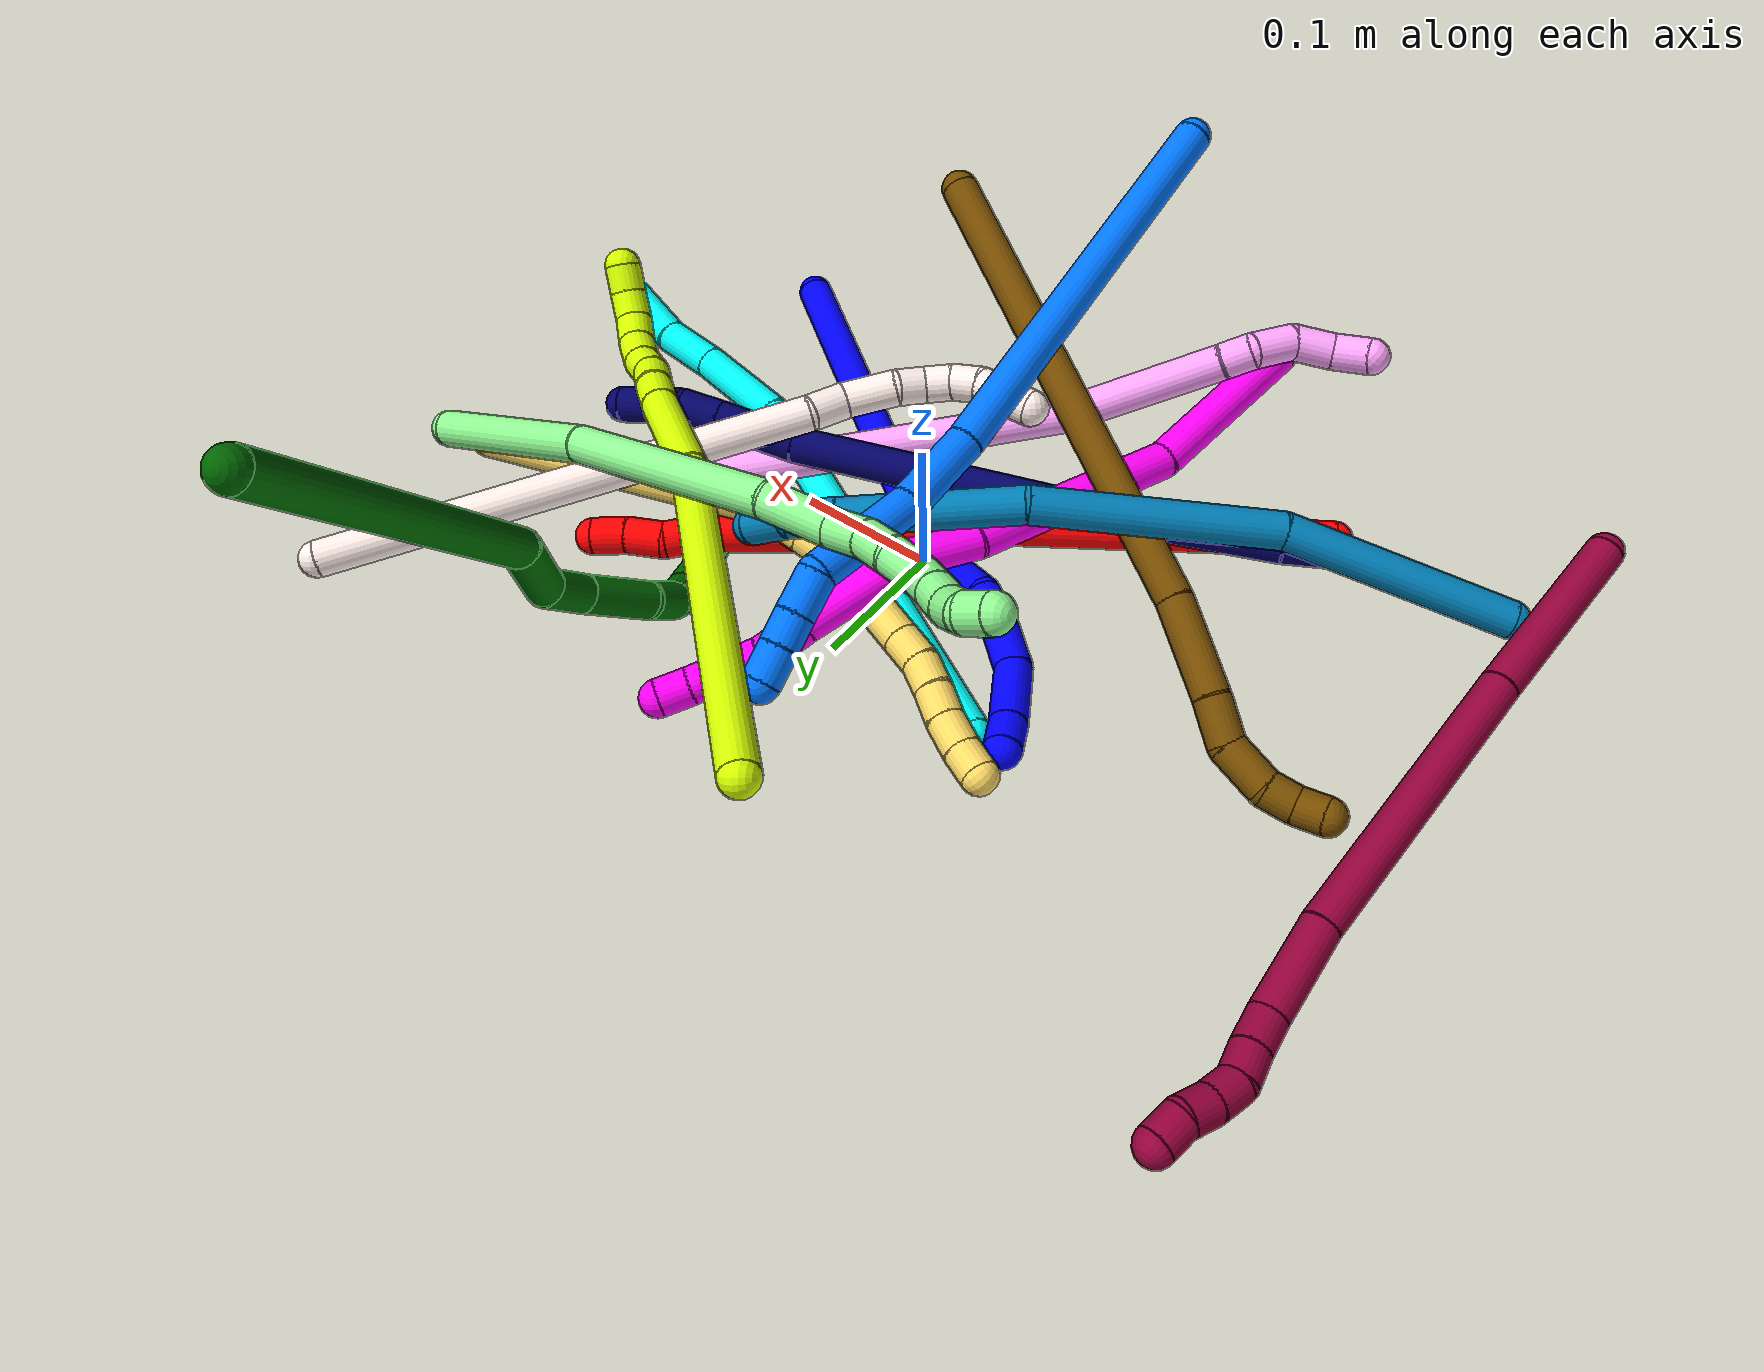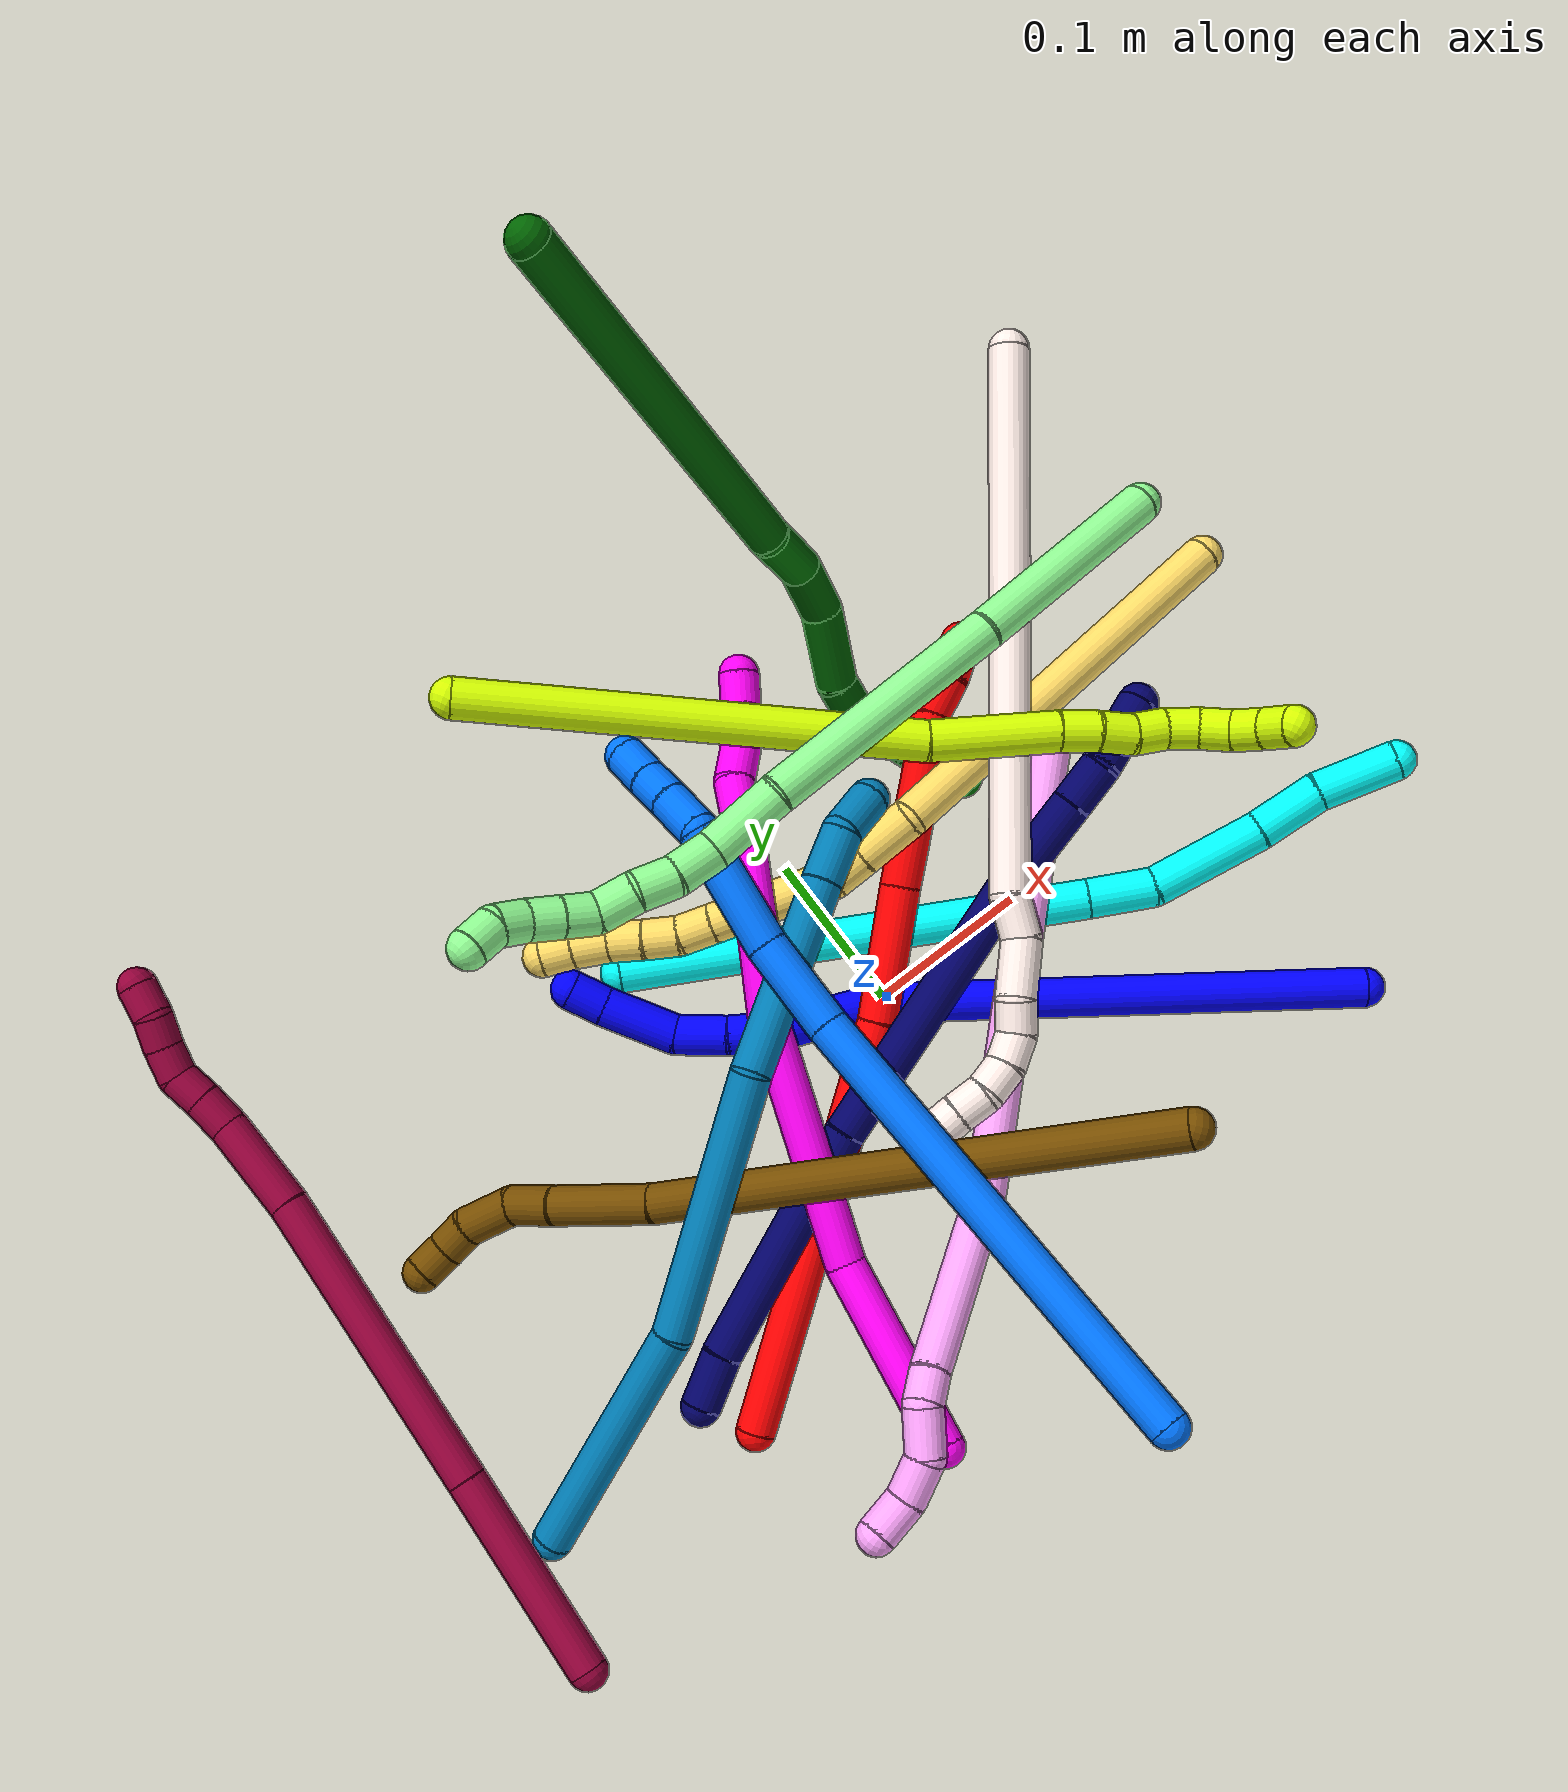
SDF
<sdf version="1.7">
 <world name="default">
  <plugin name="TubeGeneratorPlugin" filename="libtube_generator_plugin.so"/>
  <model name="photoneo_s_sensor">
   <static>1</static>
   <pose>0 0 2 1.57079 1.57079 3.14159</pose>
   <link name="link">
    <inertial><mass>0.1</mass></inertial>
    <sensor name="sensor" type="depth">
     <update_rate>30</update_rate>
     <camera>
      <horizontal_fov>1.22</horizontal_fov>
      <image><width>1920</width><height>1200</height><format>B8G8R8</format></image>
      <clip><near>0.1</near><far>4</far></clip>
      <depth_camera><output>points</output></depth_camera>
     </camera>
     <plugin name="camera_plugin" filename="libgazebo_ros_depth_camera.so">
      <baseline>0.2</baseline>
      <alwaysOn>1</alwaysOn>
      <updateRate>0.0</updateRate>
      <cameraName>camera_ir</cameraName>
      <imageTopicName>/camera/color/image_raw</imageTopicName>
      <cameraInfoTopicName>/camera/color/camera_info</cameraInfoTopicName>
      <depthImageTopicName>/camera/depth/image_raw</depthImageTopicName>
      <depthImageCameraInfoTopicName>/camera/depth/camera_info</depthImageCameraInfoTopicName>
      <pointCloudTopicName>/camera/depth/points</pointCloudTopicName>
      <frameName>fr_optical</frameName>
      <pointCloudCutoff>0.1</pointCloudCutoff>
      <pointCloudCutoffMax>2.0</pointCloudCutoffMax>
      <distortionK1>0</distortionK1>
      <distortionK2>0</distortionK2>
      <distortionK3>0</distortionK3>
      <distortionT1>0</distortionT1>
      <distortionT2>0</distortionT2>
      <CxPrime>0</CxPrime>
      <Cx>0</Cx>
      <Cy>0</Cy>
      <focalLength>0</focalLength>
      <hackBaseline>0</hackBaseline>
     </plugin>
    </sensor>
   </link>
  </model>
  <gravity>0 0 -9.8</gravity>
  <magnetic_field>6e-06 2.3e-05 -4.2e-05</magnetic_field>
  <atmosphere type="adiabatic"/>
  <physics name="default_physics" default="0" type="ode">
   <max_step_size>0.003</max_step_size>
   <real_time_factor>1</real_time_factor>
   <real_time_update_rate>1000</real_time_update_rate>
   <max_contacts>10000</max_contacts>
   <ode>
    <solver>
     <type>quick</type>
     <iters>100</iters>
     <sor>1.3</sor>
     <use_dynamic_moi_rescaling>0</use_dynamic_moi_rescaling>
    </solver>
    <constraints>
     <contact_max_correcting_vel>0</contact_max_correcting_vel>
     <contact_surface_layer>0.001</contact_surface_layer>
     <cfm>0</cfm>
     <erp>0.2</erp>
    </constraints>
   </ode>
  </physics>
  <scene><ambient>0.4 0.4 0.4 1</ambient><background>0.7 0.7 0.7 1</background><shadows>0</shadows></scene>
  <audio><device>default</device></audio>
  <spherical_coordinates>
   <surface_model>EARTH_WGS84</surface_model>
   <latitude_deg>0</latitude_deg>
   <longitude_deg>0</longitude_deg>
   <elevation>0</elevation>
   <heading_deg>0</heading_deg>
  </spherical_coordinates>
  <model name="bin">
   <static>1</static>
   <link name="bottom">
    <collision name="collision-bottom">
     <pose>0 0 -0.01 0 -0 0</pose>
     <geometry><box><size>0.8 0.6 0.02</size></box></geometry>
     <surface>
      <friction><ode><mu>100</mu><mu2>100</mu2></ode></friction>
      <contact><collide_bitmask>65535</collide_bitmask></contact>
     </surface>
    </collision>
   </link>
   <link name="west_wall">
    <collision name="collision-west_wall">
     <pose>-0.41 0 0.1 0 -0 0</pose>
     <geometry><box><size>0.02 0.6 0.2</size></box></geometry>
     <surface>
      <friction><ode><mu>100</mu><mu2>100</mu2></ode></friction>
      <contact><collide_bitmask>65535</collide_bitmask></contact>
     </surface>
    </collision>
   </link>
   <link name="east_wall">
    <collision name="collision-east_wall">
     <pose>0.41 0 0.1 0 -0 0</pose>
     <geometry><box><size>0.02 0.6 0.2</size></box></geometry>
     <surface>
      <friction><ode><mu>100</mu><mu2>100</mu2></ode></friction>
      <contact><collide_bitmask>65535</collide_bitmask></contact>
     </surface>
    </collision>
   </link>
   <link name="south_wall">
    <collision name="collision-south_wall">
     <pose>0 -0.31 0.1 0 -0 0</pose>
     <geometry><box><size>0.8 0.02 0.2</size></box></geometry>
     <surface>
      <friction><ode><mu>100</mu><mu2>100</mu2></ode></friction>
      <contact><collide_bitmask>65535</collide_bitmask></contact>
     </surface>
    </collision>
   </link>
   <link name="north_wall">
    <collision name="collision-north_wall">
     <pose>0 0.31 0.1 0 -0 0</pose>
     <geometry><box><size>0.8 0.02 0.2</size></box></geometry>
     <surface>
      <friction><ode><mu>100</mu><mu2>100</mu2></ode></friction>
      <contact><collide_bitmask>65535</collide_bitmask></contact>
     </surface>
    </collision>
   </link>
  </model>
  <model name="1">
   <static>0</static>
   <link name="1">
    <collision name="collision-cylinder-e_1_1_4">
     <pose>-0.101539 0.06077 -0.092235 -2.55901 -0.743365 1.83029</pose>
     <geometry><cylinder><radius>0.0125</radius><length>0.300071</length></cylinder></geometry>
     <surface>
      <friction><ode><mu>1.16</mu><mu2>1.16</mu2><slip1>0</slip1><slip2>0</slip2></ode></friction>
      <contact><ode><kp>1e+06</kp><kd>1</kd><max_vel>0</max_vel><min_depth>0.001</min_depth></ode></contact>
     </surface>
    </collision>
    <visual name="visual-cylinder-e_1_1_4">
     <pose>-0.101539 0.06077 -0.092235 -2.55901 -0.743365 1.83029</pose>
     <geometry><cylinder><radius>0.0125</radius><length>0.300071</length></cylinder></geometry>
     <material><ambient>0 0 1 1</ambient></material>
    </visual>
    <collision name="collision-cylinder-e_2_4_5">
     <pose>-0.230904 0.138099 -0.194438 -2.11263 -0.963716 1.49313</pose>
     <geometry><cylinder><radius>0.0125</radius><length>0.067759</length></cylinder></geometry>
     <surface>
      <friction><ode><mu>1.16</mu><mu2>1.16</mu2><slip1>0</slip1><slip2>0</slip2></ode></friction>
      <contact><ode><kp>1e+06</kp><kd>1</kd><max_vel>0</max_vel><min_depth>0.001</min_depth></ode></contact>
     </surface>
    </collision>
    <visual name="visual-cylinder-e_2_4_5">
     <pose>-0.230904 0.138099 -0.194438 -2.11263 -0.963716 1.49313</pose>
     <geometry><cylinder><radius>0.0125</radius><length>0.067759</length></cylinder></geometry>
     <material><ambient>0 0 1 1</ambient></material>
    </visual>
    <collision name="collision-cylinder-e_3_5_6">
     <pose>-0.269127 0.159767 -0.2133 -2.6203 -0.792154 2.00609</pose>
     <geometry><cylinder><radius>0.0125</radius><length>0.029211</length></cylinder></geometry>
     <surface>
      <friction><ode><mu>1.16</mu><mu2>1.16</mu2><slip1>0</slip1><slip2>0</slip2></ode></friction>
      <contact><ode><kp>1e+06</kp><kd>1</kd><max_vel>0</max_vel><min_depth>0.001</min_depth></ode></contact>
     </surface>
    </collision>
    <visual name="visual-cylinder-e_3_5_6">
     <pose>-0.269127 0.159767 -0.2133 -2.6203 -0.792154 2.00609</pose>
     <geometry><cylinder><radius>0.0125</radius><length>0.029211</length></cylinder></geometry>
     <material><ambient>0 0 1 1</ambient></material>
    </visual>
    <collision name="collision-cylinder-e_4_6_7">
     <pose>-0.289685 0.169967 -0.234075 -2.73665 -0.666235 2.07067</pose>
     <geometry><cylinder><radius>0.0125</radius><length>0.032881</length></cylinder></geometry>
     <surface>
      <friction><ode><mu>1.16</mu><mu2>1.16</mu2><slip1>0</slip1><slip2>0</slip2></ode></friction>
      <contact><ode><kp>1e+06</kp><kd>1</kd><max_vel>0</max_vel><min_depth>0.001</min_depth></ode></contact>
     </surface>
    </collision>
    <visual name="visual-cylinder-e_4_6_7">
     <pose>-0.289685 0.169967 -0.234075 -2.73665 -0.666235 2.07067</pose>
     <geometry><cylinder><radius>0.0125</radius><length>0.032881</length></cylinder></geometry>
     <material><ambient>0 0 1 1</ambient></material>
    </visual>
    <collision name="collision-cylinder-e_5_7_8">
     <pose>-0.307754 0.18938 -0.263089 -2.44543 -0.340353 0.884564</pose>
     <geometry><cylinder><radius>0.0125</radius><length>0.047382</length></cylinder></geometry>
     <surface>
      <friction><ode><mu>1.16</mu><mu2>1.16</mu2><slip1>0</slip1><slip2>0</slip2></ode></friction>
      <contact><ode><kp>1e+06</kp><kd>1</kd><max_vel>0</max_vel><min_depth>0.001</min_depth></ode></contact>
     </surface>
    </collision>
    <visual name="visual-cylinder-e_5_7_8">
     <pose>-0.307754 0.18938 -0.263089 -2.44543 -0.340353 0.884564</pose>
     <geometry><cylinder><radius>0.0125</radius><length>0.047382</length></cylinder></geometry>
     <material><ambient>0 0 1 1</ambient></material>
    </visual>
    <collision name="collision-cylinder-e_6_8_2">
     <pose>-0.318612 0.211371 -0.288052 -2.36628 -0.262926 0.62635</pose>
     <geometry><cylinder><radius>0.0125</radius><length>0.022697</length></cylinder></geometry>
     <surface>
      <friction><ode><mu>1.16</mu><mu2>1.16</mu2><slip1>0</slip1><slip2>0</slip2></ode></friction>
      <contact><ode><kp>1e+06</kp><kd>1</kd><max_vel>0</max_vel><min_depth>0.001</min_depth></ode></contact>
     </surface>
    </collision>
    <visual name="visual-cylinder-e_6_8_2">
     <pose>-0.318612 0.211371 -0.288052 -2.36628 -0.262926 0.62635</pose>
     <geometry><cylinder><radius>0.0125</radius><length>0.022697</length></cylinder></geometry>
     <material><ambient>0 0 1 1</ambient></material>
    </visual>
    <collision name="collision-sphere-2">
     <pose>-0.321562 0.219041 -0.295878 0 -0 0</pose>
     <geometry><sphere><radius>0.0125</radius></sphere></geometry>
     <surface>
      <friction><ode><mu>1.16</mu><mu2>1.16</mu2><slip1>0</slip1><slip2>0</slip2></ode></friction>
      <contact><ode><kp>1e+06</kp><kd>1</kd><max_vel>0</max_vel><min_depth>0.001</min_depth></ode></contact>
     </surface>
    </collision>
    <visual name="visual-sphere-2">
     <pose>-0.321562 0.219041 -0.295878 0 -0 0</pose>
     <geometry><sphere><radius>0.0125</radius></sphere></geometry>
     <material><ambient>0 0 1 1</ambient></material>
    </visual>
    <collision name="collision-sphere-4">
     <pose>-0.203078 0.121541 -0.18447 0 -0 0</pose>
     <geometry><sphere><radius>0.0125</radius></sphere></geometry>
     <surface>
      <friction><ode><mu>1.16</mu><mu2>1.16</mu2><slip1>0</slip1><slip2>0</slip2></ode></friction>
      <contact><ode><kp>1e+06</kp><kd>1</kd><max_vel>0</max_vel><min_depth>0.001</min_depth></ode></contact>
     </surface>
    </collision>
    <visual name="visual-sphere-4">
     <pose>-0.203078 0.121541 -0.18447 0 -0 0</pose>
     <geometry><sphere><radius>0.0125</radius></sphere></geometry>
     <material><ambient>0 0 1 1</ambient></material>
    </visual>
    <collision name="collision-sphere-1">
     <geometry><sphere><radius>0.0125</radius></sphere></geometry>
     <surface>
      <friction><ode><mu>1.16</mu><mu2>1.16</mu2><slip1>0</slip1><slip2>0</slip2></ode></friction>
      <contact><ode><kp>1e+06</kp><kd>1</kd><max_vel>0</max_vel><min_depth>0.001</min_depth></ode></contact>
     </surface>
    </collision>
    <visual name="visual-sphere-1">
     <geometry><sphere><radius>0.0125</radius></sphere></geometry>
     <material><ambient>0 0 1 1</ambient></material>
    </visual>
    <collision name="collision-sphere-8">
     <pose>-0.315662 0.2037 -0.280225 0 -0 0</pose>
     <geometry><sphere><radius>0.0125</radius></sphere></geometry>
     <surface>
      <friction><ode><mu>1.16</mu><mu2>1.16</mu2><slip1>0</slip1><slip2>0</slip2></ode></friction>
      <contact><ode><kp>1e+06</kp><kd>1</kd><max_vel>0</max_vel><min_depth>0.001</min_depth></ode></contact>
     </surface>
    </collision>
    <visual name="visual-sphere-8">
     <pose>-0.315662 0.2037 -0.280225 0 -0 0</pose>
     <geometry><sphere><radius>0.0125</radius></sphere></geometry>
     <material><ambient>0 0 1 1</ambient></material>
    </visual>
    <collision name="collision-sphere-5">
     <pose>-0.25873 0.154658 -0.204405 0 -0 0</pose>
     <geometry><sphere><radius>0.0125</radius></sphere></geometry>
     <surface>
      <friction><ode><mu>1.16</mu><mu2>1.16</mu2><slip1>0</slip1><slip2>0</slip2></ode></friction>
      <contact><ode><kp>1e+06</kp><kd>1</kd><max_vel>0</max_vel><min_depth>0.001</min_depth></ode></contact>
     </surface>
    </collision>
    <visual name="visual-sphere-5">
     <pose>-0.25873 0.154658 -0.204405 0 -0 0</pose>
     <geometry><sphere><radius>0.0125</radius></sphere></geometry>
     <material><ambient>0 0 1 1</ambient></material>
    </visual>
    <collision name="collision-sphere-6">
     <pose>-0.279524 0.164875 -0.222195 0 -0 0</pose>
     <geometry><sphere><radius>0.0125</radius></sphere></geometry>
     <surface>
      <friction><ode><mu>1.16</mu><mu2>1.16</mu2><slip1>0</slip1><slip2>0</slip2></ode></friction>
      <contact><ode><kp>1e+06</kp><kd>1</kd><max_vel>0</max_vel><min_depth>0.001</min_depth></ode></contact>
     </surface>
    </collision>
    <visual name="visual-sphere-6">
     <pose>-0.279524 0.164875 -0.222195 0 -0 0</pose>
     <geometry><sphere><radius>0.0125</radius></sphere></geometry>
     <material><ambient>0 0 1 1</ambient></material>
    </visual>
    <collision name="collision-sphere-7">
     <pose>-0.299845 0.175059 -0.245954 0 -0 0</pose>
     <geometry><sphere><radius>0.0125</radius></sphere></geometry>
     <surface>
      <friction><ode><mu>1.16</mu><mu2>1.16</mu2><slip1>0</slip1><slip2>0</slip2></ode></friction>
      <contact><ode><kp>1e+06</kp><kd>1</kd><max_vel>0</max_vel><min_depth>0.001</min_depth></ode></contact>
     </surface>
    </collision>
    <visual name="visual-sphere-7">
     <pose>-0.299845 0.175059 -0.245954 0 -0 0</pose>
     <geometry><sphere><radius>0.0125</radius></sphere></geometry>
     <material><ambient>0 0 1 1</ambient></material>
    </visual>
    <inertial>
     <pose>-0.17063 0.103238 -0.147566 0 -0 0</pose>
     <mass>0.5</mass>
     <inertia><ixx>0.001194</ixx><ixy>0</ixy><ixz>0</ixz><iyy>0.002977</iyy><iyz>0</iyz><izz>0.0006</izz></inertia>
    </inertial>
   </link>
   <pose>0.239026 -0.174925 0.015236 0.89482 0.082635 0.203299</pose>
  </model>
  <model name="2">
   <static>0</static>
   <link name="2">
    <collision name="collision-cylinder-e_1_1_4">
     <pose>0.05207 0.022158 -0.118259 -2.95637 0.40844 -2.29847</pose>
     <geometry><cylinder><radius>0.0125</radius><length>0.262201</length></cylinder></geometry>
     <surface>
      <friction><ode><mu>1.16</mu><mu2>1.16</mu2><slip1>0</slip1><slip2>0</slip2></ode></friction>
      <contact><ode><kp>1e+06</kp><kd>1</kd><max_vel>0</max_vel><min_depth>0.001</min_depth></ode></contact>
     </surface>
    </collision>
    <visual name="visual-cylinder-e_1_1_4">
     <pose>0.05207 0.022158 -0.118259 -2.95637 0.40844 -2.29847</pose>
     <geometry><cylinder><radius>0.0125</radius><length>0.262201</length></cylinder></geometry>
     <material><ambient>1 0 0 1</ambient></material>
    </visual>
    <collision name="collision-cylinder-e_2_4_5">
     <pose>0.115905 0.050262 -0.276185 -2.99281 0.285304 -2.18427</pose>
     <geometry><cylinder><radius>0.0125</radius><length>0.083602</length></cylinder></geometry>
     <surface>
      <friction><ode><mu>1.16</mu><mu2>1.16</mu2><slip1>0</slip1><slip2>0</slip2></ode></friction>
      <contact><ode><kp>1e+06</kp><kd>1</kd><max_vel>0</max_vel><min_depth>0.001</min_depth></ode></contact>
     </surface>
    </collision>
    <visual name="visual-cylinder-e_2_4_5">
     <pose>0.115905 0.050262 -0.276185 -2.99281 0.285304 -2.18427</pose>
     <geometry><cylinder><radius>0.0125</radius><length>0.083602</length></cylinder></geometry>
     <material><ambient>1 0 0 1</ambient></material>
    </visual>
    <collision name="collision-cylinder-e_3_5_6">
     <pose>0.140155 0.065776 -0.35347 -2.89252 0.311186 -1.79448</pose>
     <geometry><cylinder><radius>0.0125</radius><length>0.081547</length></cylinder></geometry>
     <surface>
      <friction><ode><mu>1.16</mu><mu2>1.16</mu2><slip1>0</slip1><slip2>0</slip2></ode></friction>
      <contact><ode><kp>1e+06</kp><kd>1</kd><max_vel>0</max_vel><min_depth>0.001</min_depth></ode></contact>
     </surface>
    </collision>
    <visual name="visual-cylinder-e_3_5_6">
     <pose>0.140155 0.065776 -0.35347 -2.89252 0.311186 -1.79448</pose>
     <geometry><cylinder><radius>0.0125</radius><length>0.081547</length></cylinder></geometry>
     <material><ambient>1 0 0 1</ambient></material>
    </visual>
    <collision name="collision-cylinder-e_4_6_7">
     <pose>0.155216 0.076288 -0.403012 -3.06265 0.212187 -2.43138</pose>
     <geometry><cylinder><radius>0.0125</radius><length>0.024472</length></cylinder></geometry>
     <surface>
      <friction><ode><mu>1.16</mu><mu2>1.16</mu2><slip1>0</slip1><slip2>0</slip2></ode></friction>
      <contact><ode><kp>1e+06</kp><kd>1</kd><max_vel>0</max_vel><min_depth>0.001</min_depth></ode></contact>
     </surface>
    </collision>
    <visual name="visual-cylinder-e_4_6_7">
     <pose>0.155216 0.076288 -0.403012 -3.06265 0.212187 -2.43138</pose>
     <geometry><cylinder><radius>0.0125</radius><length>0.024472</length></cylinder></geometry>
     <material><ambient>1 0 0 1</ambient></material>
    </visual>
    <collision name="collision-cylinder-e_5_7_8">
     <pose>0.164825 0.078379 -0.425288 -3.03118 0.593919 -2.78424</pose>
     <geometry><cylinder><radius>0.0125</radius><length>0.025134</length></cylinder></geometry>
     <surface>
      <friction><ode><mu>1.16</mu><mu2>1.16</mu2><slip1>0</slip1><slip2>0</slip2></ode></friction>
      <contact><ode><kp>1e+06</kp><kd>1</kd><max_vel>0</max_vel><min_depth>0.001</min_depth></ode></contact>
     </surface>
    </collision>
    <visual name="visual-cylinder-e_5_7_8">
     <pose>0.164825 0.078379 -0.425288 -3.03118 0.593919 -2.78424</pose>
     <geometry><cylinder><radius>0.0125</radius><length>0.025134</length></cylinder></geometry>
     <material><ambient>1 0 0 1</ambient></material>
    </visual>
    <collision name="collision-cylinder-e_6_8_2">
     <pose>0.176821 0.079839 -0.446033 -3.11155 0.445329 -3.00908</pose>
     <geometry><cylinder><radius>0.0125</radius><length>0.023045</length></cylinder></geometry>
     <surface>
      <friction><ode><mu>1.16</mu><mu2>1.16</mu2><slip1>0</slip1><slip2>0</slip2></ode></friction>
      <contact><ode><kp>1e+06</kp><kd>1</kd><max_vel>0</max_vel><min_depth>0.001</min_depth></ode></contact>
     </surface>
    </collision>
    <visual name="visual-cylinder-e_6_8_2">
     <pose>0.176821 0.079839 -0.446033 -3.11155 0.445329 -3.00908</pose>
     <geometry><cylinder><radius>0.0125</radius><length>0.023045</length></cylinder></geometry>
     <material><ambient>1 0 0 1</ambient></material>
    </visual>
    <collision name="collision-sphere-2">
     <pose>0.181784 0.080151 -0.456427 0 -0 0</pose>
     <geometry><sphere><radius>0.0125</radius></sphere></geometry>
     <surface>
      <friction><ode><mu>1.16</mu><mu2>1.16</mu2><slip1>0</slip1><slip2>0</slip2></ode></friction>
      <contact><ode><kp>1e+06</kp><kd>1</kd><max_vel>0</max_vel><min_depth>0.001</min_depth></ode></contact>
     </surface>
    </collision>
    <visual name="visual-sphere-2">
     <pose>0.181784 0.080151 -0.456427 0 -0 0</pose>
     <geometry><sphere><radius>0.0125</radius></sphere></geometry>
     <material><ambient>1 0 0 1</ambient></material>
    </visual>
    <collision name="collision-sphere-4">
     <pose>0.104141 0.044316 -0.236517 0 -0 0</pose>
     <geometry><sphere><radius>0.0125</radius></sphere></geometry>
     <surface>
      <friction><ode><mu>1.16</mu><mu2>1.16</mu2><slip1>0</slip1><slip2>0</slip2></ode></friction>
      <contact><ode><kp>1e+06</kp><kd>1</kd><max_vel>0</max_vel><min_depth>0.001</min_depth></ode></contact>
     </surface>
    </collision>
    <visual name="visual-sphere-4">
     <pose>0.104141 0.044316 -0.236517 0 -0 0</pose>
     <geometry><sphere><radius>0.0125</radius></sphere></geometry>
     <material><ambient>1 0 0 1</ambient></material>
    </visual>
    <collision name="collision-sphere-1">
     <geometry><sphere><radius>0.0125</radius></sphere></geometry>
     <surface>
      <friction><ode><mu>1.16</mu><mu2>1.16</mu2><slip1>0</slip1><slip2>0</slip2></ode></friction>
      <contact><ode><kp>1e+06</kp><kd>1</kd><max_vel>0</max_vel><min_depth>0.001</min_depth></ode></contact>
     </surface>
    </collision>
    <visual name="visual-sphere-1">
     <geometry><sphere><radius>0.0125</radius></sphere></geometry>
     <material><ambient>1 0 0 1</ambient></material>
    </visual>
    <collision name="collision-sphere-8">
     <pose>0.171858 0.079526 -0.435639 0 -0 0</pose>
     <geometry><sphere><radius>0.0125</radius></sphere></geometry>
     <surface>
      <friction><ode><mu>1.16</mu><mu2>1.16</mu2><slip1>0</slip1><slip2>0</slip2></ode></friction>
      <contact><ode><kp>1e+06</kp><kd>1</kd><max_vel>0</max_vel><min_depth>0.001</min_depth></ode></contact>
     </surface>
    </collision>
    <visual name="visual-sphere-8">
     <pose>0.171858 0.079526 -0.435639 0 -0 0</pose>
     <geometry><sphere><radius>0.0125</radius></sphere></geometry>
     <material><ambient>1 0 0 1</ambient></material>
    </visual>
    <collision name="collision-sphere-5">
     <pose>0.12767 0.056208 -0.315853 0 -0 0</pose>
     <geometry><sphere><radius>0.0125</radius></sphere></geometry>
     <surface>
      <friction><ode><mu>1.16</mu><mu2>1.16</mu2><slip1>0</slip1><slip2>0</slip2></ode></friction>
      <contact><ode><kp>1e+06</kp><kd>1</kd><max_vel>0</max_vel><min_depth>0.001</min_depth></ode></contact>
     </surface>
    </collision>
    <visual name="visual-sphere-5">
     <pose>0.12767 0.056208 -0.315853 0 -0 0</pose>
     <geometry><sphere><radius>0.0125</radius></sphere></geometry>
     <material><ambient>1 0 0 1</ambient></material>
    </visual>
    <collision name="collision-sphere-6">
     <pose>0.152639 0.075344 -0.391087 0 -0 0</pose>
     <geometry><sphere><radius>0.0125</radius></sphere></geometry>
     <surface>
      <friction><ode><mu>1.16</mu><mu2>1.16</mu2><slip1>0</slip1><slip2>0</slip2></ode></friction>
      <contact><ode><kp>1e+06</kp><kd>1</kd><max_vel>0</max_vel><min_depth>0.001</min_depth></ode></contact>
     </surface>
    </collision>
    <visual name="visual-sphere-6">
     <pose>0.152639 0.075344 -0.391087 0 -0 0</pose>
     <geometry><sphere><radius>0.0125</radius></sphere></geometry>
     <material><ambient>1 0 0 1</ambient></material>
    </visual>
    <collision name="collision-sphere-7">
     <pose>0.157793 0.077231 -0.414936 0 -0 0</pose>
     <geometry><sphere><radius>0.0125</radius></sphere></geometry>
     <surface>
      <friction><ode><mu>1.16</mu><mu2>1.16</mu2><slip1>0</slip1><slip2>0</slip2></ode></friction>
      <contact><ode><kp>1e+06</kp><kd>1</kd><max_vel>0</max_vel><min_depth>0.001</min_depth></ode></contact>
     </surface>
    </collision>
    <visual name="visual-sphere-7">
     <pose>0.157793 0.077231 -0.414936 0 -0 0</pose>
     <geometry><sphere><radius>0.0125</radius></sphere></geometry>
     <material><ambient>1 0 0 1</ambient></material>
    </visual>
    <inertial>
     <pose>0.093576 0.042105 -0.227503 0 -0 0</pose>
     <mass>0.5</mass>
     <inertia>
      <ixx>-0.002077</ixx>
      <ixy>0</ixy>
      <ixz>0</ixz>
      <iyy>4e-06</iyy>
      <iyz>0</iyz>
      <izz>-0.000943</izz>
     </inertia>
    </inertial>
   </link>
   <pose>-0.22481 -0.16382 0.023287 1.41711 -0.050934 -0.53238</pose>
  </model>
  <model name="3">
   <static>0</static>
   <link name="3">
    <collision name="collision-cylinder-e_1_1_4">
     <pose>0.083171 -0.101784 0.063979 1.00963 0.605214 0.341657</pose>
     <geometry><cylinder><radius>0.0125</radius><length>0.292374</length></cylinder></geometry>
     <surface>
      <friction><ode><mu>1.16</mu><mu2>1.16</mu2><slip1>0</slip1><slip2>0</slip2></ode></friction>
      <contact><ode><kp>1e+06</kp><kd>1</kd><max_vel>0</max_vel><min_depth>0.001</min_depth></ode></contact>
     </surface>
    </collision>
    <visual name="visual-cylinder-e_1_1_4">
     <pose>0.083171 -0.101784 0.063979 1.00963 0.605214 0.341657</pose>
     <geometry><cylinder><radius>0.0125</radius><length>0.292374</length></cylinder></geometry>
     <material><ambient>0.003922 1 0.996078 1</ambient></material>
    </visual>
    <collision name="collision-cylinder-e_2_4_5">
     <pose>0.177878 -0.218582 0.137069 1.02538 0.581123 0.333512</pose>
     <geometry><cylinder><radius>0.0125</radius><length>0.042025</length></cylinder></geometry>
     <surface>
      <friction><ode><mu>1.16</mu><mu2>1.16</mu2><slip1>0</slip1><slip2>0</slip2></ode></friction>
      <contact><ode><kp>1e+06</kp><kd>1</kd><max_vel>0</max_vel><min_depth>0.001</min_depth></ode></contact>
     </surface>
    </collision>
    <visual name="visual-cylinder-e_2_4_5">
     <pose>0.177878 -0.218582 0.137069 1.02538 0.581123 0.333512</pose>
     <geometry><cylinder><radius>0.0125</radius><length>0.042025</length></cylinder></geometry>
     <material><ambient>0.003922 1 0.996078 1</ambient></material>
    </visual>
    <collision name="collision-cylinder-e_3_5_6">
     <pose>0.198695 -0.262613 0.165845 0.975178 0.258878 0.137835</pose>
     <geometry><cylinder><radius>0.0125</radius><length>0.072521</length></cylinder></geometry>
     <surface>
      <friction><ode><mu>1.16</mu><mu2>1.16</mu2><slip1>0</slip1><slip2>0</slip2></ode></friction>
      <contact><ode><kp>1e+06</kp><kd>1</kd><max_vel>0</max_vel><min_depth>0.001</min_depth></ode></contact>
     </surface>
    </collision>
    <visual name="visual-cylinder-e_3_5_6">
     <pose>0.198695 -0.262613 0.165845 0.975178 0.258878 0.137835</pose>
     <geometry><cylinder><radius>0.0125</radius><length>0.072521</length></cylinder></geometry>
     <material><ambient>0.003922 1 0.996078 1</ambient></material>
    </visual>
    <collision name="collision-cylinder-e_4_6_7">
     <pose>0.211524 -0.308829 0.197474 0.963043 0.167643 0.08775</pose>
     <geometry><cylinder><radius>0.0125</radius><length>0.0425</length></cylinder></geometry>
     <surface>
      <friction><ode><mu>1.16</mu><mu2>1.16</mu2><slip1>0</slip1><slip2>0</slip2></ode></friction>
      <contact><ode><kp>1e+06</kp><kd>1</kd><max_vel>0</max_vel><min_depth>0.001</min_depth></ode></contact>
     </surface>
    </collision>
    <visual name="visual-cylinder-e_4_6_7">
     <pose>0.211524 -0.308829 0.197474 0.963043 0.167643 0.08775</pose>
     <geometry><cylinder><radius>0.0125</radius><length>0.0425</length></cylinder></geometry>
     <material><ambient>0.003922 1 0.996078 1</ambient></material>
    </visual>
    <collision name="collision-cylinder-e_5_7_2">
     <pose>0.223461 -0.347272 0.220299 1.09817 0.338243 0.208193</pose>
     <geometry><cylinder><radius>0.0125</radius><length>0.05058</length></cylinder></geometry>
     <surface>
      <friction><ode><mu>1.16</mu><mu2>1.16</mu2><slip1>0</slip1><slip2>0</slip2></ode></friction>
      <contact><ode><kp>1e+06</kp><kd>1</kd><max_vel>0</max_vel><min_depth>0.001</min_depth></ode></contact>
     </surface>
    </collision>
    <visual name="visual-cylinder-e_5_7_2">
     <pose>0.223461 -0.347272 0.220299 1.09817 0.338243 0.208193</pose>
     <geometry><cylinder><radius>0.0125</radius><length>0.05058</length></cylinder></geometry>
     <material><ambient>0.003922 1 0.996078 1</ambient></material>
    </visual>
    <collision name="collision-sphere-2">
     <pose>0.231853 -0.368514 0.231159 0 -0 0</pose>
     <geometry><sphere><radius>0.0125</radius></sphere></geometry>
     <surface>
      <friction><ode><mu>1.16</mu><mu2>1.16</mu2><slip1>0</slip1><slip2>0</slip2></ode></friction>
      <contact><ode><kp>1e+06</kp><kd>1</kd><max_vel>0</max_vel><min_depth>0.001</min_depth></ode></contact>
     </surface>
    </collision>
    <visual name="visual-sphere-2">
     <pose>0.231853 -0.368514 0.231159 0 -0 0</pose>
     <geometry><sphere><radius>0.0125</radius></sphere></geometry>
     <material><ambient>0.003922 1 0.996078 1</ambient></material>
    </visual>
    <collision name="collision-sphere-7">
     <pose>0.215069 -0.32603 0.209438 0 -0 0</pose>
     <geometry><sphere><radius>0.0125</radius></sphere></geometry>
     <surface>
      <friction><ode><mu>1.16</mu><mu2>1.16</mu2><slip1>0</slip1><slip2>0</slip2></ode></friction>
      <contact><ode><kp>1e+06</kp><kd>1</kd><max_vel>0</max_vel><min_depth>0.001</min_depth></ode></contact>
     </surface>
    </collision>
    <visual name="visual-sphere-7">
     <pose>0.215069 -0.32603 0.209438 0 -0 0</pose>
     <geometry><sphere><radius>0.0125</radius></sphere></geometry>
     <material><ambient>0.003922 1 0.996078 1</ambient></material>
    </visual>
    <collision name="collision-sphere-6">
     <pose>0.207978 -0.291629 0.18551 0 -0 0</pose>
     <geometry><sphere><radius>0.0125</radius></sphere></geometry>
     <surface>
      <friction><ode><mu>1.16</mu><mu2>1.16</mu2><slip1>0</slip1><slip2>0</slip2></ode></friction>
      <contact><ode><kp>1e+06</kp><kd>1</kd><max_vel>0</max_vel><min_depth>0.001</min_depth></ode></contact>
     </surface>
    </collision>
    <visual name="visual-sphere-6">
     <pose>0.207978 -0.291629 0.18551 0 -0 0</pose>
     <geometry><sphere><radius>0.0125</radius></sphere></geometry>
     <material><ambient>0.003922 1 0.996078 1</ambient></material>
    </visual>
    <collision name="collision-sphere-5">
     <pose>0.189413 -0.233597 0.14618 0 -0 0</pose>
     <geometry><sphere><radius>0.0125</radius></sphere></geometry>
     <surface>
      <friction><ode><mu>1.16</mu><mu2>1.16</mu2><slip1>0</slip1><slip2>0</slip2></ode></friction>
      <contact><ode><kp>1e+06</kp><kd>1</kd><max_vel>0</max_vel><min_depth>0.001</min_depth></ode></contact>
     </surface>
    </collision>
    <visual name="visual-sphere-5">
     <pose>0.189413 -0.233597 0.14618 0 -0 0</pose>
     <geometry><sphere><radius>0.0125</radius></sphere></geometry>
     <material><ambient>0.003922 1 0.996078 1</ambient></material>
    </visual>
    <collision name="collision-sphere-1">
     <geometry><sphere><radius>0.0125</radius></sphere></geometry>
     <surface>
      <friction><ode><mu>1.16</mu><mu2>1.16</mu2><slip1>0</slip1><slip2>0</slip2></ode></friction>
      <contact><ode><kp>1e+06</kp><kd>1</kd><max_vel>0</max_vel><min_depth>0.001</min_depth></ode></contact>
     </surface>
    </collision>
    <visual name="visual-sphere-1">
     <geometry><sphere><radius>0.0125</radius></sphere></geometry>
     <material><ambient>0.003922 1 0.996078 1</ambient></material>
    </visual>
    <collision name="collision-sphere-4">
     <pose>0.166343 -0.203567 0.127957 0 -0 0</pose>
     <geometry><sphere><radius>0.0125</radius></sphere></geometry>
     <surface>
      <friction><ode><mu>1.16</mu><mu2>1.16</mu2><slip1>0</slip1><slip2>0</slip2></ode></friction>
      <contact><ode><kp>1e+06</kp><kd>1</kd><max_vel>0</max_vel><min_depth>0.001</min_depth></ode></contact>
     </surface>
    </collision>
    <visual name="visual-sphere-4">
     <pose>0.166343 -0.203567 0.127957 0 -0 0</pose>
     <geometry><sphere><radius>0.0125</radius></sphere></geometry>
     <material><ambient>0.003922 1 0.996078 1</ambient></material>
    </visual>
    <inertial>
     <pose>0.132989 -0.17736 0.112057 0 -0 0</pose>
     <mass>0.5</mass>
     <inertia>
      <ixx>0.002287</ixx>
      <ixy>0</ixy>
      <ixz>0</ixz>
      <iyy>0.001983</iyy>
      <iyz>0</iyz>
      <izz>0.000316</izz>
     </inertia>
    </inertial>
   </link>
   <pose>-0.120424 0.11098 0.012171 -2.39048 0.270326 -1.43511</pose>
  </model>
  <model name="4">
   <static>0</static>
   <link name="4">
    <collision name="collision-cylinder-e_1_1_4">
     <pose>-0.076669 -0.07346 0.08881 0.691082 -0.586996 -0.216741</pose>
     <geometry><cylinder><radius>0.0125</radius><length>0.276851</length></cylinder></geometry>
     <surface>
      <friction><ode><mu>1.16</mu><mu2>1.16</mu2><slip1>0</slip1><slip2>0</slip2></ode></friction>
      <contact><ode><kp>1e+06</kp><kd>1</kd><max_vel>0</max_vel><min_depth>0.001</min_depth></ode></contact>
     </surface>
    </collision>
    <visual name="visual-cylinder-e_1_1_4">
     <pose>-0.076669 -0.07346 0.08881 0.691082 -0.586996 -0.216741</pose>
     <geometry><cylinder><radius>0.0125</radius><length>0.276851</length></cylinder></geometry>
     <material><ambient>1 0.65098 0.996078 1</ambient></material>
    </visual>
    <collision name="collision-cylinder-e_2_4_5">
     <pose>-0.177524 -0.195667 0.200281 1.13564 -0.422791 -0.272096</pose>
     <geometry><cylinder><radius>0.0125</radius><length>0.117896</length></cylinder></geometry>
     <surface>
      <friction><ode><mu>1.16</mu><mu2>1.16</mu2><slip1>0</slip1><slip2>0</slip2></ode></friction>
      <contact><ode><kp>1e+06</kp><kd>1</kd><max_vel>0</max_vel><min_depth>0.001</min_depth></ode></contact>
     </surface>
    </collision>
    <visual name="visual-cylinder-e_2_4_5">
     <pose>-0.177524 -0.195667 0.200281 1.13564 -0.422791 -0.272096</pose>
     <geometry><cylinder><radius>0.0125</radius><length>0.117896</length></cylinder></geometry>
     <material><ambient>1 0.65098 0.996078 1</ambient></material>
    </visual>
    <collision name="collision-cylinder-e_3_5_6">
     <pose>-0.206815 -0.252189 0.227202 1.06961 -0.522432 -0.314113</pose>
     <geometry><cylinder><radius>0.0125</radius><length>0.02046</length></cylinder></geometry>
     <surface>
      <friction><ode><mu>1.16</mu><mu2>1.16</mu2><slip1>0</slip1><slip2>0</slip2></ode></friction>
      <contact><ode><kp>1e+06</kp><kd>1</kd><max_vel>0</max_vel><min_depth>0.001</min_depth></ode></contact>
     </surface>
    </collision>
    <visual name="visual-cylinder-e_3_5_6">
     <pose>-0.206815 -0.252189 0.227202 1.06961 -0.522432 -0.314113</pose>
     <geometry><cylinder><radius>0.0125</radius><length>0.02046</length></cylinder></geometry>
     <material><ambient>1 0.65098 0.996078 1</ambient></material>
    </visual>
    <collision name="collision-cylinder-e_4_6_7">
     <pose>-0.222291 -0.264994 0.241029 0.48404 -0.764705 -0.197896</pose>
     <geometry><cylinder><radius>0.0125</radius><length>0.02996</length></cylinder></geometry>
     <surface>
      <friction><ode><mu>1.16</mu><mu2>1.16</mu2><slip1>0</slip1><slip2>0</slip2></ode></friction>
      <contact><ode><kp>1e+06</kp><kd>1</kd><max_vel>0</max_vel><min_depth>0.001</min_depth></ode></contact>
     </surface>
    </collision>
    <visual name="visual-cylinder-e_4_6_7">
     <pose>-0.222291 -0.264994 0.241029 0.48404 -0.764705 -0.197896</pose>
     <geometry><cylinder><radius>0.0125</radius><length>0.02996</length></cylinder></geometry>
     <material><ambient>1 0.65098 0.996078 1</ambient></material>
    </visual>
    <collision name="collision-cylinder-e_5_7_8">
     <pose>-0.236517 -0.27577 0.263076 0.431485 -0.273532 -0.060304</pose>
     <geometry><cylinder><radius>0.0125</radius><length>0.028538</length></cylinder></geometry>
     <surface>
      <friction><ode><mu>1.16</mu><mu2>1.16</mu2><slip1>0</slip1><slip2>0</slip2></ode></friction>
      <contact><ode><kp>1e+06</kp><kd>1</kd><max_vel>0</max_vel><min_depth>0.001</min_depth></ode></contact>
     </surface>
    </collision>
    <visual name="visual-cylinder-e_5_7_8">
     <pose>-0.236517 -0.27577 0.263076 0.431485 -0.273532 -0.060304</pose>
     <geometry><cylinder><radius>0.0125</radius><length>0.028538</length></cylinder></geometry>
     <material><ambient>1 0.65098 0.996078 1</ambient></material>
    </visual>
    <collision name="collision-cylinder-e_6_8_2">
     <pose>-0.240974 -0.291535 0.284048 0.867635 -0.045869 -0.021252</pose>
     <geometry><cylinder><radius>0.0125</radius><length>0.026296</length></cylinder></geometry>
     <surface>
      <friction><ode><mu>1.16</mu><mu2>1.16</mu2><slip1>0</slip1><slip2>0</slip2></ode></friction>
      <contact><ode><kp>1e+06</kp><kd>1</kd><max_vel>0</max_vel><min_depth>0.001</min_depth></ode></contact>
     </surface>
    </collision>
    <visual name="visual-cylinder-e_6_8_2">
     <pose>-0.240974 -0.291535 0.284048 0.867635 -0.045869 -0.021252</pose>
     <geometry><cylinder><radius>0.0125</radius><length>0.026296</length></cylinder></geometry>
     <material><ambient>1 0.65098 0.996078 1</ambient></material>
    </visual>
    <collision name="collision-sphere-2">
     <pose>-0.241577 -0.301553 0.292541 0 -0 0</pose>
     <geometry><sphere><radius>0.0125</radius></sphere></geometry>
     <surface>
      <friction><ode><mu>1.16</mu><mu2>1.16</mu2><slip1>0</slip1><slip2>0</slip2></ode></friction>
      <contact><ode><kp>1e+06</kp><kd>1</kd><max_vel>0</max_vel><min_depth>0.001</min_depth></ode></contact>
     </surface>
    </collision>
    <visual name="visual-sphere-2">
     <pose>-0.241577 -0.301553 0.292541 0 -0 0</pose>
     <geometry><sphere><radius>0.0125</radius></sphere></geometry>
     <material><ambient>1 0.65098 0.996078 1</ambient></material>
    </visual>
    <collision name="collision-sphere-4">
     <pose>-0.153337 -0.146919 0.17762 0 -0 0</pose>
     <geometry><sphere><radius>0.0125</radius></sphere></geometry>
     <surface>
      <friction><ode><mu>1.16</mu><mu2>1.16</mu2><slip1>0</slip1><slip2>0</slip2></ode></friction>
      <contact><ode><kp>1e+06</kp><kd>1</kd><max_vel>0</max_vel><min_depth>0.001</min_depth></ode></contact>
     </surface>
    </collision>
    <visual name="visual-sphere-4">
     <pose>-0.153337 -0.146919 0.17762 0 -0 0</pose>
     <geometry><sphere><radius>0.0125</radius></sphere></geometry>
     <material><ambient>1 0.65098 0.996078 1</ambient></material>
    </visual>
    <collision name="collision-sphere-1">
     <geometry><sphere><radius>0.0125</radius></sphere></geometry>
     <surface>
      <friction><ode><mu>1.16</mu><mu2>1.16</mu2><slip1>0</slip1><slip2>0</slip2></ode></friction>
      <contact><ode><kp>1e+06</kp><kd>1</kd><max_vel>0</max_vel><min_depth>0.001</min_depth></ode></contact>
     </surface>
    </collision>
    <visual name="visual-sphere-1">
     <geometry><sphere><radius>0.0125</radius></sphere></geometry>
     <material><ambient>1 0.65098 0.996078 1</ambient></material>
    </visual>
    <collision name="collision-sphere-8">
     <pose>-0.240371 -0.281516 0.275555 0 -0 0</pose>
     <geometry><sphere><radius>0.0125</radius></sphere></geometry>
     <surface>
      <friction><ode><mu>1.16</mu><mu2>1.16</mu2><slip1>0</slip1><slip2>0</slip2></ode></friction>
      <contact><ode><kp>1e+06</kp><kd>1</kd><max_vel>0</max_vel><min_depth>0.001</min_depth></ode></contact>
     </surface>
    </collision>
    <visual name="visual-sphere-8">
     <pose>-0.240371 -0.281516 0.275555 0 -0 0</pose>
     <geometry><sphere><radius>0.0125</radius></sphere></geometry>
     <material><ambient>1 0.65098 0.996078 1</ambient></material>
    </visual>
    <collision name="collision-sphere-5">
     <pose>-0.201711 -0.244414 0.222943 0 -0 0</pose>
     <geometry><sphere><radius>0.0125</radius></sphere></geometry>
     <surface>
      <friction><ode><mu>1.16</mu><mu2>1.16</mu2><slip1>0</slip1><slip2>0</slip2></ode></friction>
      <contact><ode><kp>1e+06</kp><kd>1</kd><max_vel>0</max_vel><min_depth>0.001</min_depth></ode></contact>
     </surface>
    </collision>
    <visual name="visual-sphere-5">
     <pose>-0.201711 -0.244414 0.222943 0 -0 0</pose>
     <geometry><sphere><radius>0.0125</radius></sphere></geometry>
     <material><ambient>1 0.65098 0.996078 1</ambient></material>
    </visual>
    <collision name="collision-sphere-6">
     <pose>-0.21192 -0.259964 0.231462 0 -0 0</pose>
     <geometry><sphere><radius>0.0125</radius></sphere></geometry>
     <surface>
      <friction><ode><mu>1.16</mu><mu2>1.16</mu2><slip1>0</slip1><slip2>0</slip2></ode></friction>
      <contact><ode><kp>1e+06</kp><kd>1</kd><max_vel>0</max_vel><min_depth>0.001</min_depth></ode></contact>
     </surface>
    </collision>
    <visual name="visual-sphere-6">
     <pose>-0.21192 -0.259964 0.231462 0 -0 0</pose>
     <geometry><sphere><radius>0.0125</radius></sphere></geometry>
     <material><ambient>1 0.65098 0.996078 1</ambient></material>
    </visual>
    <collision name="collision-sphere-7">
     <pose>-0.232662 -0.270025 0.250597 0 -0 0</pose>
     <geometry><sphere><radius>0.0125</radius></sphere></geometry>
     <surface>
      <friction><ode><mu>1.16</mu><mu2>1.16</mu2><slip1>0</slip1><slip2>0</slip2></ode></friction>
      <contact><ode><kp>1e+06</kp><kd>1</kd><max_vel>0</max_vel><min_depth>0.001</min_depth></ode></contact>
     </surface>
    </collision>
    <visual name="visual-sphere-7">
     <pose>-0.232662 -0.270025 0.250597 0 -0 0</pose>
     <geometry><sphere><radius>0.0125</radius></sphere></geometry>
     <material><ambient>1 0.65098 0.996078 1</ambient></material>
    </visual>
    <inertial>
     <pose>-0.132265 -0.144081 0.150092 0 -0 0</pose>
     <mass>0.5</mass>
     <inertia>
      <ixx>0.001207</ixx>
      <ixy>0</ixy>
      <ixz>0</ixz>
      <iyy>0.001176</iyy>
      <iyz>0</iyz>
      <izz>0.002137</izz>
     </inertia>
    </inertial>
   </link>
   <pose>0.172607 0.059567 0.025486 -2.26583 0.201358 1.75672</pose>
  </model>
  <model name="5">
   <static>0</static>
   <link name="5">
    <collision name="collision-cylinder-e_1_1_4">
     <pose>-0.101688 0.024314 -0.07284 -2.81942 -0.924001 2.51072</pose>
     <geometry><cylinder><radius>0.0125</radius><length>0.25485</length></cylinder></geometry>
     <surface>
      <friction><ode><mu>1.16</mu><mu2>1.16</mu2><slip1>0</slip1><slip2>0</slip2></ode></friction>
      <contact><ode><kp>1e+06</kp><kd>1</kd><max_vel>0</max_vel><min_depth>0.001</min_depth></ode></contact>
     </surface>
    </collision>
    <visual name="visual-cylinder-e_1_1_4">
     <pose>-0.101688 0.024314 -0.07284 -2.81942 -0.924001 2.51072</pose>
     <geometry><cylinder><radius>0.0125</radius><length>0.25485</length></cylinder></geometry>
     <material><ambient>1 0.858824 0.4 1</ambient></material>
    </visual>
    <collision name="collision-cylinder-e_2_4_5">
     <pose>-0.217548 0.058094 -0.15109 -2.0901 -0.915032 1.40733</pose>
     <geometry><cylinder><radius>0.0125</radius><length>0.035763</length></cylinder></geometry>
     <surface>
      <friction><ode><mu>1.16</mu><mu2>1.16</mu2><slip1>0</slip1><slip2>0</slip2></ode></friction>
      <contact><ode><kp>1e+06</kp><kd>1</kd><max_vel>0</max_vel><min_depth>0.001</min_depth></ode></contact>
     </surface>
    </collision>
    <visual name="visual-cylinder-e_2_4_5">
     <pose>-0.217548 0.058094 -0.15109 -2.0901 -0.915032 1.40733</pose>
     <geometry><cylinder><radius>0.0125</radius><length>0.035763</length></cylinder></geometry>
     <material><ambient>1 0.858824 0.4 1</ambient></material>
    </visual>
    <collision name="collision-cylinder-e_3_5_6">
     <pose>-0.240724 0.0734 -0.159893 -2.097 -0.927216 1.43033</pose>
     <geometry><cylinder><radius>0.0125</radius><length>0.022508</length></cylinder></geometry>
     <surface>
      <friction><ode><mu>1.16</mu><mu2>1.16</mu2><slip1>0</slip1><slip2>0</slip2></ode></friction>
      <contact><ode><kp>1e+06</kp><kd>1</kd><max_vel>0</max_vel><min_depth>0.001</min_depth></ode></contact>
     </surface>
    </collision>
    <visual name="visual-cylinder-e_3_5_6">
     <pose>-0.240724 0.0734 -0.159893 -2.097 -0.927216 1.43033</pose>
     <geometry><cylinder><radius>0.0125</radius><length>0.022508</length></cylinder></geometry>
     <material><ambient>1 0.858824 0.4 1</ambient></material>
    </visual>
    <collision name="collision-cylinder-e_4_6_7">
     <pose>-0.286568 0.092625 -0.166421 -1.80092 -1.21364 1.43837</pose>
     <geometry><cylinder><radius>0.0125</radius><length>0.078646</length></cylinder></geometry>
     <surface>
      <friction><ode><mu>1.16</mu><mu2>1.16</mu2><slip1>0</slip1><slip2>0</slip2></ode></friction>
      <contact><ode><kp>1e+06</kp><kd>1</kd><max_vel>0</max_vel><min_depth>0.001</min_depth></ode></contact>
     </surface>
    </collision>
    <visual name="visual-cylinder-e_4_6_7">
     <pose>-0.286568 0.092625 -0.166421 -1.80092 -1.21364 1.43837</pose>
     <geometry><cylinder><radius>0.0125</radius><length>0.078646</length></cylinder></geometry>
     <material><ambient>1 0.858824 0.4 1</ambient></material>
    </visual>
    <collision name="collision-cylinder-e_5_7_8">
     <pose>-0.333503 0.109555 -0.170435 -1.81375 -1.22368 1.46209</pose>
     <geometry><cylinder><radius>0.0125</radius><length>0.021468</length></cylinder></geometry>
     <surface>
      <friction><ode><mu>1.16</mu><mu2>1.16</mu2><slip1>0</slip1><slip2>0</slip2></ode></friction>
      <contact><ode><kp>1e+06</kp><kd>1</kd><max_vel>0</max_vel><min_depth>0.001</min_depth></ode></contact>
     </surface>
    </collision>
    <visual name="visual-cylinder-e_5_7_8">
     <pose>-0.333503 0.109555 -0.170435 -1.81375 -1.22368 1.46209</pose>
     <geometry><cylinder><radius>0.0125</radius><length>0.021468</length></cylinder></geometry>
     <material><ambient>1 0.858824 0.4 1</ambient></material>
    </visual>
    <collision name="collision-cylinder-e_6_8_9">
     <pose>-0.354157 0.115382 -0.169996 -1.04719 -1.3261 0.847221</pose>
     <geometry><cylinder><radius>0.0125</radius><length>0.021768</length></cylinder></geometry>
     <surface>
      <friction><ode><mu>1.16</mu><mu2>1.16</mu2><slip1>0</slip1><slip2>0</slip2></ode></friction>
      <contact><ode><kp>1e+06</kp><kd>1</kd><max_vel>0</max_vel><min_depth>0.001</min_depth></ode></contact>
     </surface>
    </collision>
    <visual name="visual-cylinder-e_6_8_9">
     <pose>-0.354157 0.115382 -0.169996 -1.04719 -1.3261 0.847221</pose>
     <geometry><cylinder><radius>0.0125</radius><length>0.021768</length></cylinder></geometry>
     <material><ambient>1 0.858824 0.4 1</ambient></material>
    </visual>
    <collision name="collision-cylinder-e_7_9_10">
     <pose>-0.375034 0.120441 -0.16659 -0.926039 -1.24614 0.688829</pose>
     <geometry><cylinder><radius>0.0125</radius><length>0.021774</length></cylinder></geometry>
     <surface>
      <friction><ode><mu>1.16</mu><mu2>1.16</mu2><slip1>0</slip1><slip2>0</slip2></ode></friction>
      <contact><ode><kp>1e+06</kp><kd>1</kd><max_vel>0</max_vel><min_depth>0.001</min_depth></ode></contact>
     </surface>
    </collision>
    <visual name="visual-cylinder-e_7_9_10">
     <pose>-0.375034 0.120441 -0.16659 -0.926039 -1.24614 0.688829</pose>
     <geometry><cylinder><radius>0.0125</radius><length>0.021774</length></cylinder></geometry>
     <material><ambient>1 0.858824 0.4 1</ambient></material>
    </visual>
    <collision name="collision-cylinder-e_8_10_11">
     <pose>-0.396531 0.126219 -0.163673 -1.30121 -1.29905 1.04828</pose>
     <geometry><cylinder><radius>0.0125</radius><length>0.023208</length></cylinder></geometry>
     <surface>
      <friction><ode><mu>1.16</mu><mu2>1.16</mu2><slip1>0</slip1><slip2>0</slip2></ode></friction>
      <contact><ode><kp>1e+06</kp><kd>1</kd><max_vel>0</max_vel><min_depth>0.001</min_depth></ode></contact>
     </surface>
    </collision>
    <visual name="visual-cylinder-e_8_10_11">
     <pose>-0.396531 0.126219 -0.163673 -1.30121 -1.29905 1.04828</pose>
     <geometry><cylinder><radius>0.0125</radius><length>0.023208</length></cylinder></geometry>
     <material><ambient>1 0.858824 0.4 1</ambient></material>
    </visual>
    <collision name="collision-cylinder-e_9_11_2">
     <pose>-0.417395 0.131721 -0.16313 -1.68473 -1.31662 1.4285</pose>
     <geometry><cylinder><radius>0.0125</radius><length>0.020015</length></cylinder></geometry>
     <surface>
      <friction><ode><mu>1.16</mu><mu2>1.16</mu2><slip1>0</slip1><slip2>0</slip2></ode></friction>
      <contact><ode><kp>1e+06</kp><kd>1</kd><max_vel>0</max_vel><min_depth>0.001</min_depth></ode></contact>
     </surface>
    </collision>
    <visual name="visual-cylinder-e_9_11_2">
     <pose>-0.417395 0.131721 -0.16313 -1.68473 -1.31662 1.4285</pose>
     <geometry><cylinder><radius>0.0125</radius><length>0.020015</length></cylinder></geometry>
     <material><ambient>1 0.858824 0.4 1</ambient></material>
    </visual>
    <collision name="collision-sphere-2">
     <pose>-0.42708 0.134221 -0.163416 0 -0 0</pose>
     <geometry><sphere><radius>0.0125</radius></sphere></geometry>
     <surface>
      <friction><ode><mu>1.16</mu><mu2>1.16</mu2><slip1>0</slip1><slip2>0</slip2></ode></friction>
      <contact><ode><kp>1e+06</kp><kd>1</kd><max_vel>0</max_vel><min_depth>0.001</min_depth></ode></contact>
     </surface>
    </collision>
    <visual name="visual-sphere-2">
     <pose>-0.42708 0.134221 -0.163416 0 -0 0</pose>
     <geometry><sphere><radius>0.0125</radius></sphere></geometry>
     <material><ambient>1 0.858824 0.4 1</ambient></material>
    </visual>
    <collision name="collision-sphere-11">
     <pose>-0.407709 0.129221 -0.162844 0 -0 0</pose>
     <geometry><sphere><radius>0.0125</radius></sphere></geometry>
     <surface>
      <friction><ode><mu>1.16</mu><mu2>1.16</mu2><slip1>0</slip1><slip2>0</slip2></ode></friction>
      <contact><ode><kp>1e+06</kp><kd>1</kd><max_vel>0</max_vel><min_depth>0.001</min_depth></ode></contact>
     </surface>
    </collision>
    <visual name="visual-sphere-11">
     <pose>-0.407709 0.129221 -0.162844 0 -0 0</pose>
     <geometry><sphere><radius>0.0125</radius></sphere></geometry>
     <material><ambient>1 0.858824 0.4 1</ambient></material>
    </visual>
    <collision name="collision-sphere-10">
     <pose>-0.385352 0.123217 -0.164503 0 -0 0</pose>
     <geometry><sphere><radius>0.0125</radius></sphere></geometry>
     <surface>
      <friction><ode><mu>1.16</mu><mu2>1.16</mu2><slip1>0</slip1><slip2>0</slip2></ode></friction>
      <contact><ode><kp>1e+06</kp><kd>1</kd><max_vel>0</max_vel><min_depth>0.001</min_depth></ode></contact>
     </surface>
    </collision>
    <visual name="visual-sphere-10">
     <pose>-0.385352 0.123217 -0.164503 0 -0 0</pose>
     <geometry><sphere><radius>0.0125</radius></sphere></geometry>
     <material><ambient>1 0.858824 0.4 1</ambient></material>
    </visual>
    <collision name="collision-sphere-9">
     <pose>-0.364716 0.117666 -0.168677 0 -0 0</pose>
     <geometry><sphere><radius>0.0125</radius></sphere></geometry>
     <surface>
      <friction><ode><mu>1.16</mu><mu2>1.16</mu2><slip1>0</slip1><slip2>0</slip2></ode></friction>
      <contact><ode><kp>1e+06</kp><kd>1</kd><max_vel>0</max_vel><min_depth>0.001</min_depth></ode></contact>
     </surface>
    </collision>
    <visual name="visual-sphere-9">
     <pose>-0.364716 0.117666 -0.168677 0 -0 0</pose>
     <geometry><sphere><radius>0.0125</radius></sphere></geometry>
     <material><ambient>1 0.858824 0.4 1</ambient></material>
    </visual>
    <collision name="collision-sphere-4">
     <pose>-0.203375 0.048628 -0.145679 0 -0 0</pose>
     <geometry><sphere><radius>0.0125</radius></sphere></geometry>
     <surface>
      <friction><ode><mu>1.16</mu><mu2>1.16</mu2><slip1>0</slip1><slip2>0</slip2></ode></friction>
      <contact><ode><kp>1e+06</kp><kd>1</kd><max_vel>0</max_vel><min_depth>0.001</min_depth></ode></contact>
     </surface>
    </collision>
    <visual name="visual-sphere-4">
     <pose>-0.203375 0.048628 -0.145679 0 -0 0</pose>
     <geometry><sphere><radius>0.0125</radius></sphere></geometry>
     <material><ambient>1 0.858824 0.4 1</ambient></material>
    </visual>
    <collision name="collision-sphere-1">
     <geometry><sphere><radius>0.0125</radius></sphere></geometry>
     <surface>
      <friction><ode><mu>1.16</mu><mu2>1.16</mu2><slip1>0</slip1><slip2>0</slip2></ode></friction>
      <contact><ode><kp>1e+06</kp><kd>1</kd><max_vel>0</max_vel><min_depth>0.001</min_depth></ode></contact>
     </surface>
    </collision>
    <visual name="visual-sphere-1">
     <geometry><sphere><radius>0.0125</radius></sphere></geometry>
     <material><ambient>1 0.858824 0.4 1</ambient></material>
    </visual>
    <collision name="collision-sphere-8">
     <pose>-0.343597 0.113099 -0.171314 0 -0 0</pose>
     <geometry><sphere><radius>0.0125</radius></sphere></geometry>
     <surface>
      <friction><ode><mu>1.16</mu><mu2>1.16</mu2><slip1>0</slip1><slip2>0</slip2></ode></friction>
      <contact><ode><kp>1e+06</kp><kd>1</kd><max_vel>0</max_vel><min_depth>0.001</min_depth></ode></contact>
     </surface>
    </collision>
    <visual name="visual-sphere-8">
     <pose>-0.343597 0.113099 -0.171314 0 -0 0</pose>
     <geometry><sphere><radius>0.0125</radius></sphere></geometry>
     <material><ambient>1 0.858824 0.4 1</ambient></material>
    </visual>
    <collision name="collision-sphere-5">
     <pose>-0.231721 0.06756 -0.156502 0 -0 0</pose>
     <geometry><sphere><radius>0.0125</radius></sphere></geometry>
     <surface>
      <friction><ode><mu>1.16</mu><mu2>1.16</mu2><slip1>0</slip1><slip2>0</slip2></ode></friction>
      <contact><ode><kp>1e+06</kp><kd>1</kd><max_vel>0</max_vel><min_depth>0.001</min_depth></ode></contact>
     </surface>
    </collision>
    <visual name="visual-sphere-5">
     <pose>-0.231721 0.06756 -0.156502 0 -0 0</pose>
     <geometry><sphere><radius>0.0125</radius></sphere></geometry>
     <material><ambient>1 0.858824 0.4 1</ambient></material>
    </visual>
    <collision name="collision-sphere-6">
     <pose>-0.249726 0.079239 -0.163285 0 -0 0</pose>
     <geometry><sphere><radius>0.0125</radius></sphere></geometry>
     <surface>
      <friction><ode><mu>1.16</mu><mu2>1.16</mu2><slip1>0</slip1><slip2>0</slip2></ode></friction>
      <contact><ode><kp>1e+06</kp><kd>1</kd><max_vel>0</max_vel><min_depth>0.001</min_depth></ode></contact>
     </surface>
    </collision>
    <visual name="visual-sphere-6">
     <pose>-0.249726 0.079239 -0.163285 0 -0 0</pose>
     <geometry><sphere><radius>0.0125</radius></sphere></geometry>
     <material><ambient>1 0.858824 0.4 1</ambient></material>
    </visual>
    <collision name="collision-sphere-7">
     <pose>-0.323409 0.10601 -0.169557 0 -0 0</pose>
     <geometry><sphere><radius>0.0125</radius></sphere></geometry>
     <surface>
      <friction><ode><mu>1.16</mu><mu2>1.16</mu2><slip1>0</slip1><slip2>0</slip2></ode></friction>
      <contact><ode><kp>1e+06</kp><kd>1</kd><max_vel>0</max_vel><min_depth>0.001</min_depth></ode></contact>
     </surface>
    </collision>
    <visual name="visual-sphere-7">
     <pose>-0.323409 0.10601 -0.169557 0 -0 0</pose>
     <geometry><sphere><radius>0.0125</radius></sphere></geometry>
     <material><ambient>1 0.858824 0.4 1</ambient></material>
    </visual>
    <inertial>
     <pose>-0.204485 0.060525 -0.117408 0 -0 0</pose>
     <mass>0.5</mass>
     <inertia>
      <ixx>-0.00019</ixx>
      <ixy>0</ixy>
      <ixz>0</ixz>
      <iyy>0.001847</iyy>
      <iyz>0</iyz>
      <izz>0.000865</izz>
     </inertia>
    </inertial>
   </link>
   <pose>0.322005 0.09752 0.011892 -2.14623 0.099308 -0.560433</pose>
  </model>
  <model name="6">
   <static>0</static>
   <link name="6">
    <collision name="collision-cylinder-e_1_1_4">
     <pose>0.000419 0.022168 -0.123167 -2.96352 0.003348 -0.037497</pose>
     <geometry><cylinder><radius>0.0125</radius><length>0.250293</length></cylinder></geometry>
     <surface>
      <friction><ode><mu>1.16</mu><mu2>1.16</mu2><slip1>0</slip1><slip2>0</slip2></ode></friction>
      <contact><ode><kp>1e+06</kp><kd>1</kd><max_vel>0</max_vel><min_depth>0.001</min_depth></ode></contact>
     </surface>
    </collision>
    <visual name="visual-cylinder-e_1_1_4">
     <pose>0.000419 0.022168 -0.123167 -2.96352 0.003348 -0.037497</pose>
     <geometry><cylinder><radius>0.0125</radius><length>0.250293</length></cylinder></geometry>
     <material><ambient>0 0.392157 0.003922 1</ambient></material>
    </visual>
    <collision name="collision-cylinder-e_2_4_5">
     <pose>0.006885 0.057439 -0.271116 -2.65522 0.21246 -0.811854</pose>
     <geometry><cylinder><radius>0.0125</radius><length>0.057354</length></cylinder></geometry>
     <surface>
      <friction><ode><mu>1.16</mu><mu2>1.16</mu2><slip1>0</slip1><slip2>0</slip2></ode></friction>
      <contact><ode><kp>1e+06</kp><kd>1</kd><max_vel>0</max_vel><min_depth>0.001</min_depth></ode></contact>
     </surface>
    </collision>
    <visual name="visual-cylinder-e_2_4_5">
     <pose>0.006885 0.057439 -0.271116 -2.65522 0.21246 -0.811854</pose>
     <geometry><cylinder><radius>0.0125</radius><length>0.057354</length></cylinder></geometry>
     <material><ambient>0 0.392157 0.003922 1</ambient></material>
    </visual>
    <collision name="collision-cylinder-e_3_5_6">
     <pose>0.009528 0.07331 -0.313328 -2.9841 -0.190529 1.761</pose>
     <geometry><cylinder><radius>0.0125</radius><length>0.035949</length></cylinder></geometry>
     <surface>
      <friction><ode><mu>1.16</mu><mu2>1.16</mu2><slip1>0</slip1><slip2>0</slip2></ode></friction>
      <contact><ode><kp>1e+06</kp><kd>1</kd><max_vel>0</max_vel><min_depth>0.001</min_depth></ode></contact>
     </surface>
    </collision>
    <visual name="visual-cylinder-e_3_5_6">
     <pose>0.009528 0.07331 -0.313328 -2.9841 -0.190529 1.761</pose>
     <geometry><cylinder><radius>0.0125</radius><length>0.035949</length></cylinder></geometry>
     <material><ambient>0 0.392157 0.003922 1</ambient></material>
    </visual>
    <collision name="collision-cylinder-e_4_6_7">
     <pose>-0.005551 0.079002 -0.352067 -3.00525 -0.497307 2.61621</pose>
     <geometry><cylinder><radius>0.0125</radius><length>0.048944</length></cylinder></geometry>
     <surface>
      <friction><ode><mu>1.16</mu><mu2>1.16</mu2><slip1>0</slip1><slip2>0</slip2></ode></friction>
      <contact><ode><kp>1e+06</kp><kd>1</kd><max_vel>0</max_vel><min_depth>0.001</min_depth></ode></contact>
     </surface>
    </collision>
    <visual name="visual-cylinder-e_4_6_7">
     <pose>-0.005551 0.079002 -0.352067 -3.00525 -0.497307 2.61621</pose>
     <geometry><cylinder><radius>0.0125</radius><length>0.048944</length></cylinder></geometry>
     <material><ambient>0 0.392157 0.003922 1</ambient></material>
    </visual>
    <collision name="collision-cylinder-e_5_7_8">
     <pose>-0.020132 0.082619 -0.386697 -3.08955 -0.21457 2.66737</pose>
     <geometry><cylinder><radius>0.0125</radius><length>0.027307</length></cylinder></geometry>
     <surface>
      <friction><ode><mu>1.16</mu><mu2>1.16</mu2><slip1>0</slip1><slip2>0</slip2></ode></friction>
      <contact><ode><kp>1e+06</kp><kd>1</kd><max_vel>0</max_vel><min_depth>0.001</min_depth></ode></contact>
     </surface>
    </collision>
    <visual name="visual-cylinder-e_5_7_8">
     <pose>-0.020132 0.082619 -0.386697 -3.08955 -0.21457 2.66737</pose>
     <geometry><cylinder><radius>0.0125</radius><length>0.027307</length></cylinder></geometry>
     <material><ambient>0 0.392157 0.003922 1</ambient></material>
    </visual>
    <collision name="collision-cylinder-e_6_8_9">
     <pose>-0.021466 0.080485 -0.409551 2.85317 0.156958 0.992616</pose>
     <geometry><cylinder><radius>0.0125</radius><length>0.020132</length></cylinder></geometry>
     <surface>
      <friction><ode><mu>1.16</mu><mu2>1.16</mu2><slip1>0</slip1><slip2>0</slip2></ode></friction>
      <contact><ode><kp>1e+06</kp><kd>1</kd><max_vel>0</max_vel><min_depth>0.001</min_depth></ode></contact>
     </surface>
    </collision>
    <visual name="visual-cylinder-e_6_8_9">
     <pose>-0.021466 0.080485 -0.409551 2.85317 0.156958 0.992616</pose>
     <geometry><cylinder><radius>0.0125</radius><length>0.020132</length></cylinder></geometry>
     <material><ambient>0 0.392157 0.003922 1</ambient></material>
    </visual>
    <collision name="collision-cylinder-e_7_9_10">
     <pose>-0.020274 0.072735 -0.42778 2.62663 -0.038178 -0.144749</pose>
     <geometry><cylinder><radius>0.0125</radius><length>0.020002</length></cylinder></geometry>
     <surface>
      <friction><ode><mu>1.16</mu><mu2>1.16</mu2><slip1>0</slip1><slip2>0</slip2></ode></friction>
      <contact><ode><kp>1e+06</kp><kd>1</kd><max_vel>0</max_vel><min_depth>0.001</min_depth></ode></contact>
     </surface>
    </collision>
    <visual name="visual-cylinder-e_7_9_10">
     <pose>-0.020274 0.072735 -0.42778 2.62663 -0.038178 -0.144749</pose>
     <geometry><cylinder><radius>0.0125</radius><length>0.020002</length></cylinder></geometry>
     <material><ambient>0 0.392157 0.003922 1</ambient></material>
    </visual>
    <collision name="collision-cylinder-e_8_10_11">
     <pose>-0.018871 0.063483 -0.445316 2.686 0.179398 0.740197</pose>
     <geometry><cylinder><radius>0.0125</radius><length>0.020005</length></cylinder></geometry>
     <surface>
      <friction><ode><mu>1.16</mu><mu2>1.16</mu2><slip1>0</slip1><slip2>0</slip2></ode></friction>
      <contact><ode><kp>1e+06</kp><kd>1</kd><max_vel>0</max_vel><min_depth>0.001</min_depth></ode></contact>
     </surface>
    </collision>
    <visual name="visual-cylinder-e_8_10_11">
     <pose>-0.018871 0.063483 -0.445316 2.686 0.179398 0.740197</pose>
     <geometry><cylinder><radius>0.0125</radius><length>0.020005</length></cylinder></geometry>
     <material><ambient>0 0.392157 0.003922 1</ambient></material>
    </visual>
    <collision name="collision-cylinder-e_9_11_2">
     <pose>-0.017493 0.053363 -0.462305 2.52398 -0.040618 -0.127172</pose>
     <geometry><cylinder><radius>0.0125</radius><length>0.020014</length></cylinder></geometry>
     <surface>
      <friction><ode><mu>1.16</mu><mu2>1.16</mu2><slip1>0</slip1><slip2>0</slip2></ode></friction>
      <contact><ode><kp>1e+06</kp><kd>1</kd><max_vel>0</max_vel><min_depth>0.001</min_depth></ode></contact>
     </surface>
    </collision>
    <visual name="visual-cylinder-e_9_11_2">
     <pose>-0.017493 0.053363 -0.462305 2.52398 -0.040618 -0.127172</pose>
     <geometry><cylinder><radius>0.0125</radius><length>0.020014</length></cylinder></geometry>
     <material><ambient>0 0.392157 0.003922 1</ambient></material>
    </visual>
    <collision name="collision-sphere-2">
     <pose>-0.017899 0.047573 -0.470457 0 -0 0</pose>
     <geometry><sphere><radius>0.0125</radius></sphere></geometry>
     <surface>
      <friction><ode><mu>1.16</mu><mu2>1.16</mu2><slip1>0</slip1><slip2>0</slip2></ode></friction>
      <contact><ode><kp>1e+06</kp><kd>1</kd><max_vel>0</max_vel><min_depth>0.001</min_depth></ode></contact>
     </surface>
    </collision>
    <visual name="visual-sphere-2">
     <pose>-0.017899 0.047573 -0.470457 0 -0 0</pose>
     <geometry><sphere><radius>0.0125</radius></sphere></geometry>
     <material><ambient>0 0.392157 0.003922 1</ambient></material>
    </visual>
    <collision name="collision-sphere-11">
     <pose>-0.017087 0.059153 -0.454154 0 -0 0</pose>
     <geometry><sphere><radius>0.0125</radius></sphere></geometry>
     <surface>
      <friction><ode><mu>1.16</mu><mu2>1.16</mu2><slip1>0</slip1><slip2>0</slip2></ode></friction>
      <contact><ode><kp>1e+06</kp><kd>1</kd><max_vel>0</max_vel><min_depth>0.001</min_depth></ode></contact>
     </surface>
    </collision>
    <visual name="visual-sphere-11">
     <pose>-0.017087 0.059153 -0.454154 0 -0 0</pose>
     <geometry><sphere><radius>0.0125</radius></sphere></geometry>
     <material><ambient>0 0.392157 0.003922 1</ambient></material>
    </visual>
    <collision name="collision-sphere-10">
     <pose>-0.020656 0.067813 -0.436478 0 -0 0</pose>
     <geometry><sphere><radius>0.0125</radius></sphere></geometry>
     <surface>
      <friction><ode><mu>1.16</mu><mu2>1.16</mu2><slip1>0</slip1><slip2>0</slip2></ode></friction>
      <contact><ode><kp>1e+06</kp><kd>1</kd><max_vel>0</max_vel><min_depth>0.001</min_depth></ode></contact>
     </surface>
    </collision>
    <visual name="visual-sphere-10">
     <pose>-0.020656 0.067813 -0.436478 0 -0 0</pose>
     <geometry><sphere><radius>0.0125</radius></sphere></geometry>
     <material><ambient>0 0.392157 0.003922 1</ambient></material>
    </visual>
    <collision name="collision-sphere-9">
     <pose>-0.019893 0.077657 -0.419083 0 -0 0</pose>
     <geometry><sphere><radius>0.0125</radius></sphere></geometry>
     <surface>
      <friction><ode><mu>1.16</mu><mu2>1.16</mu2><slip1>0</slip1><slip2>0</slip2></ode></friction>
      <contact><ode><kp>1e+06</kp><kd>1</kd><max_vel>0</max_vel><min_depth>0.001</min_depth></ode></contact>
     </surface>
    </collision>
    <visual name="visual-sphere-9">
     <pose>-0.019893 0.077657 -0.419083 0 -0 0</pose>
     <geometry><sphere><radius>0.0125</radius></sphere></geometry>
     <material><ambient>0 0.392157 0.003922 1</ambient></material>
    </visual>
    <collision name="collision-sphere-4">
     <pose>0.000838 0.044336 -0.246334 0 -0 0</pose>
     <geometry><sphere><radius>0.0125</radius></sphere></geometry>
     <surface>
      <friction><ode><mu>1.16</mu><mu2>1.16</mu2><slip1>0</slip1><slip2>0</slip2></ode></friction>
      <contact><ode><kp>1e+06</kp><kd>1</kd><max_vel>0</max_vel><min_depth>0.001</min_depth></ode></contact>
     </surface>
    </collision>
    <visual name="visual-sphere-4">
     <pose>0.000838 0.044336 -0.246334 0 -0 0</pose>
     <geometry><sphere><radius>0.0125</radius></sphere></geometry>
     <material><ambient>0 0.392157 0.003922 1</ambient></material>
    </visual>
    <collision name="collision-sphere-1">
     <geometry><sphere><radius>0.0125</radius></sphere></geometry>
     <surface>
      <friction><ode><mu>1.16</mu><mu2>1.16</mu2><slip1>0</slip1><slip2>0</slip2></ode></friction>
      <contact><ode><kp>1e+06</kp><kd>1</kd><max_vel>0</max_vel><min_depth>0.001</min_depth></ode></contact>
     </surface>
    </collision>
    <visual name="visual-sphere-1">
     <geometry><sphere><radius>0.0125</radius></sphere></geometry>
     <material><ambient>0 0.392157 0.003922 1</ambient></material>
    </visual>
    <collision name="collision-sphere-8">
     <pose>-0.02304 0.083313 -0.40002 0 -0 0</pose>
     <geometry><sphere><radius>0.0125</radius></sphere></geometry>
     <surface>
      <friction><ode><mu>1.16</mu><mu2>1.16</mu2><slip1>0</slip1><slip2>0</slip2></ode></friction>
      <contact><ode><kp>1e+06</kp><kd>1</kd><max_vel>0</max_vel><min_depth>0.001</min_depth></ode></contact>
     </surface>
    </collision>
    <visual name="visual-sphere-8">
     <pose>-0.02304 0.083313 -0.40002 0 -0 0</pose>
     <geometry><sphere><radius>0.0125</radius></sphere></geometry>
     <material><ambient>0 0.392157 0.003922 1</ambient></material>
    </visual>
    <collision name="collision-sphere-5">
     <pose>0.012932 0.070542 -0.295897 0 -0 0</pose>
     <geometry><sphere><radius>0.0125</radius></sphere></geometry>
     <surface>
      <friction><ode><mu>1.16</mu><mu2>1.16</mu2><slip1>0</slip1><slip2>0</slip2></ode></friction>
      <contact><ode><kp>1e+06</kp><kd>1</kd><max_vel>0</max_vel><min_depth>0.001</min_depth></ode></contact>
     </surface>
    </collision>
    <visual name="visual-sphere-5">
     <pose>0.012932 0.070542 -0.295897 0 -0 0</pose>
     <geometry><sphere><radius>0.0125</radius></sphere></geometry>
     <material><ambient>0 0.392157 0.003922 1</ambient></material>
    </visual>
    <collision name="collision-sphere-6">
     <pose>0.006124 0.076078 -0.330759 0 -0 0</pose>
     <geometry><sphere><radius>0.0125</radius></sphere></geometry>
     <surface>
      <friction><ode><mu>1.16</mu><mu2>1.16</mu2><slip1>0</slip1><slip2>0</slip2></ode></friction>
      <contact><ode><kp>1e+06</kp><kd>1</kd><max_vel>0</max_vel><min_depth>0.001</min_depth></ode></contact>
     </surface>
    </collision>
    <visual name="visual-sphere-6">
     <pose>0.006124 0.076078 -0.330759 0 -0 0</pose>
     <geometry><sphere><radius>0.0125</radius></sphere></geometry>
     <material><ambient>0 0.392157 0.003922 1</ambient></material>
    </visual>
    <collision name="collision-sphere-7">
     <pose>-0.017225 0.081925 -0.373375 0 -0 0</pose>
     <geometry><sphere><radius>0.0125</radius></sphere></geometry>
     <surface>
      <friction><ode><mu>1.16</mu><mu2>1.16</mu2><slip1>0</slip1><slip2>0</slip2></ode></friction>
      <contact><ode><kp>1e+06</kp><kd>1</kd><max_vel>0</max_vel><min_depth>0.001</min_depth></ode></contact>
     </surface>
    </collision>
    <visual name="visual-sphere-7">
     <pose>-0.017225 0.081925 -0.373375 0 -0 0</pose>
     <geometry><sphere><radius>0.0125</radius></sphere></geometry>
     <material><ambient>0 0.392157 0.003922 1</ambient></material>
    </visual>
    <inertial>
     <pose>-0.003089 0.046028 -0.24079 0 -0 0</pose>
     <mass>0.5</mass>
     <inertia>
      <ixx>0.00127</ixx>
      <ixy>0</ixy>
      <ixz>0</ixz>
      <iyy>-0.001339</iyy>
      <iyz>0</iyz>
      <izz>-0.000279</izz>
     </inertia>
    </inertial>
   </link>
   <pose>0.073487 0.406366 0.34958 -0.846406 0.189318 0.396093</pose>
  </model>
  <model name="7">
   <static>0</static>
   <link name="7">
    <collision name="collision-cylinder-e_1_1_4">
     <pose>0.009954 0.001753 -0.01374 -3.01471 0.623115 -2.75209</pose>
     <geometry><cylinder><radius>0.0125</radius><length>0.034115</length></cylinder></geometry>
     <surface>
      <friction><ode><mu>1.16</mu><mu2>1.16</mu2><slip1>0</slip1><slip2>0</slip2></ode></friction>
      <contact><ode><kp>1e+06</kp><kd>1</kd><max_vel>0</max_vel><min_depth>0.001</min_depth></ode></contact>
     </surface>
    </collision>
    <visual name="visual-cylinder-e_1_1_4">
     <pose>0.009954 0.001753 -0.01374 -3.01471 0.623115 -2.75209</pose>
     <geometry><cylinder><radius>0.0125</radius><length>0.034115</length></cylinder></geometry>
     <material><ambient>0.003922 0 0.403922 1</ambient></material>
    </visual>
    <collision name="collision-cylinder-e_2_4_5">
     <pose>0.063163 0.001942 -0.090481 3.11678 0.601514 3.06165</pose>
     <geometry><cylinder><radius>0.0125</radius><length>0.152872</length></cylinder></geometry>
     <surface>
      <friction><ode><mu>1.16</mu><mu2>1.16</mu2><slip1>0</slip1><slip2>0</slip2></ode></friction>
      <contact><ode><kp>1e+06</kp><kd>1</kd><max_vel>0</max_vel><min_depth>0.001</min_depth></ode></contact>
     </surface>
    </collision>
    <visual name="visual-cylinder-e_2_4_5">
     <pose>0.063163 0.001942 -0.090481 3.11678 0.601514 3.06165</pose>
     <geometry><cylinder><radius>0.0125</radius><length>0.152872</length></cylinder></geometry>
     <material><ambient>0.003922 0 0.403922 1</ambient></material>
    </visual>
    <collision name="collision-cylinder-e_3_5_6">
     <pose>0.156289 -0.008341 -0.229239 3.02699 0.579173 2.76122</pose>
     <geometry><cylinder><radius>0.0125</radius><length>0.182236</length></cylinder></geometry>
     <surface>
      <friction><ode><mu>1.16</mu><mu2>1.16</mu2><slip1>0</slip1><slip2>0</slip2></ode></friction>
      <contact><ode><kp>1e+06</kp><kd>1</kd><max_vel>0</max_vel><min_depth>0.001</min_depth></ode></contact>
     </surface>
    </collision>
    <visual name="visual-cylinder-e_3_5_6">
     <pose>0.156289 -0.008341 -0.229239 3.02699 0.579173 2.76122</pose>
     <geometry><cylinder><radius>0.0125</radius><length>0.182236</length></cylinder></geometry>
     <material><ambient>0.003922 0 0.403922 1</ambient></material>
    </visual>
    <collision name="collision-cylinder-e_4_6_7">
     <pose>0.22305 -0.022047 -0.327092 2.91963 0.6407 2.49351</pose>
     <geometry><cylinder><radius>0.0125</radius><length>0.056508</length></cylinder></geometry>
     <surface>
      <friction><ode><mu>1.16</mu><mu2>1.16</mu2><slip1>0</slip1><slip2>0</slip2></ode></friction>
      <contact><ode><kp>1e+06</kp><kd>1</kd><max_vel>0</max_vel><min_depth>0.001</min_depth></ode></contact>
     </surface>
    </collision>
    <visual name="visual-cylinder-e_4_6_7">
     <pose>0.22305 -0.022047 -0.327092 2.91963 0.6407 2.49351</pose>
     <geometry><cylinder><radius>0.0125</radius><length>0.056508</length></cylinder></geometry>
     <material><ambient>0.003922 0 0.403922 1</ambient></material>
    </visual>
    <collision name="collision-cylinder-e_5_7_8">
     <pose>0.248212 -0.029455 -0.360701 2.93427 0.61281 2.50618</pose>
     <geometry><cylinder><radius>0.0125</radius><length>0.028767</length></cylinder></geometry>
     <surface>
      <friction><ode><mu>1.16</mu><mu2>1.16</mu2><slip1>0</slip1><slip2>0</slip2></ode></friction>
      <contact><ode><kp>1e+06</kp><kd>1</kd><max_vel>0</max_vel><min_depth>0.001</min_depth></ode></contact>
     </surface>
    </collision>
    <visual name="visual-cylinder-e_5_7_8">
     <pose>0.248212 -0.029455 -0.360701 2.93427 0.61281 2.50618</pose>
     <geometry><cylinder><radius>0.0125</radius><length>0.028767</length></cylinder></geometry>
     <material><ambient>0.003922 0 0.403922 1</ambient></material>
    </visual>
    <collision name="collision-cylinder-e_6_8_2">
     <pose>0.265002 -0.032545 -0.393302 3.10996 0.383735 2.97908</pose>
     <geometry><cylinder><radius>0.0125</radius><length>0.045503</length></cylinder></geometry>
     <surface>
      <friction><ode><mu>1.16</mu><mu2>1.16</mu2><slip1>0</slip1><slip2>0</slip2></ode></friction>
      <contact><ode><kp>1e+06</kp><kd>1</kd><max_vel>0</max_vel><min_depth>0.001</min_depth></ode></contact>
     </surface>
    </collision>
    <visual name="visual-cylinder-e_6_8_2">
     <pose>0.265002 -0.032545 -0.393302 3.10996 0.383735 2.97908</pose>
     <geometry><cylinder><radius>0.0125</radius><length>0.045503</length></cylinder></geometry>
     <material><ambient>0.003922 0 0.403922 1</ambient></material>
    </visual>
    <collision name="collision-sphere-2">
     <pose>0.27352 -0.033212 -0.414388 0 -0 0</pose>
     <geometry><sphere><radius>0.0125</radius></sphere></geometry>
     <surface>
      <friction><ode><mu>1.16</mu><mu2>1.16</mu2><slip1>0</slip1><slip2>0</slip2></ode></friction>
      <contact><ode><kp>1e+06</kp><kd>1</kd><max_vel>0</max_vel><min_depth>0.001</min_depth></ode></contact>
     </surface>
    </collision>
    <visual name="visual-sphere-2">
     <pose>0.27352 -0.033212 -0.414388 0 -0 0</pose>
     <geometry><sphere><radius>0.0125</radius></sphere></geometry>
     <material><ambient>0.003922 0 0.403922 1</ambient></material>
    </visual>
    <collision name="collision-sphere-4">
     <pose>0.019908 0.003506 -0.027481 0 -0 0</pose>
     <geometry><sphere><radius>0.0125</radius></sphere></geometry>
     <surface>
      <friction><ode><mu>1.16</mu><mu2>1.16</mu2><slip1>0</slip1><slip2>0</slip2></ode></friction>
      <contact><ode><kp>1e+06</kp><kd>1</kd><max_vel>0</max_vel><min_depth>0.001</min_depth></ode></contact>
     </surface>
    </collision>
    <visual name="visual-sphere-4">
     <pose>0.019908 0.003506 -0.027481 0 -0 0</pose>
     <geometry><sphere><radius>0.0125</radius></sphere></geometry>
     <material><ambient>0.003922 0 0.403922 1</ambient></material>
    </visual>
    <collision name="collision-sphere-1">
     <geometry><sphere><radius>0.0125</radius></sphere></geometry>
     <surface>
      <friction><ode><mu>1.16</mu><mu2>1.16</mu2><slip1>0</slip1><slip2>0</slip2></ode></friction>
      <contact><ode><kp>1e+06</kp><kd>1</kd><max_vel>0</max_vel><min_depth>0.001</min_depth></ode></contact>
     </surface>
    </collision>
    <visual name="visual-sphere-1">
     <geometry><sphere><radius>0.0125</radius></sphere></geometry>
     <material><ambient>0.003922 0 0.403922 1</ambient></material>
    </visual>
    <collision name="collision-sphere-8">
     <pose>0.256485 -0.031877 -0.372216 0 -0 0</pose>
     <geometry><sphere><radius>0.0125</radius></sphere></geometry>
     <surface>
      <friction><ode><mu>1.16</mu><mu2>1.16</mu2><slip1>0</slip1><slip2>0</slip2></ode></friction>
      <contact><ode><kp>1e+06</kp><kd>1</kd><max_vel>0</max_vel><min_depth>0.001</min_depth></ode></contact>
     </surface>
    </collision>
    <visual name="visual-sphere-8">
     <pose>0.256485 -0.031877 -0.372216 0 -0 0</pose>
     <geometry><sphere><radius>0.0125</radius></sphere></geometry>
     <material><ambient>0.003922 0 0.403922 1</ambient></material>
    </visual>
    <collision name="collision-sphere-5">
     <pose>0.106417 0.000379 -0.153481 0 -0 0</pose>
     <geometry><sphere><radius>0.0125</radius></sphere></geometry>
     <surface>
      <friction><ode><mu>1.16</mu><mu2>1.16</mu2><slip1>0</slip1><slip2>0</slip2></ode></friction>
      <contact><ode><kp>1e+06</kp><kd>1</kd><max_vel>0</max_vel><min_depth>0.001</min_depth></ode></contact>
     </surface>
    </collision>
    <visual name="visual-sphere-5">
     <pose>0.106417 0.000379 -0.153481 0 -0 0</pose>
     <geometry><sphere><radius>0.0125</radius></sphere></geometry>
     <material><ambient>0.003922 0 0.403922 1</ambient></material>
    </visual>
    <collision name="collision-sphere-6">
     <pose>0.206161 -0.017061 -0.304997 0 -0 0</pose>
     <geometry><sphere><radius>0.0125</radius></sphere></geometry>
     <surface>
      <friction><ode><mu>1.16</mu><mu2>1.16</mu2><slip1>0</slip1><slip2>0</slip2></ode></friction>
      <contact><ode><kp>1e+06</kp><kd>1</kd><max_vel>0</max_vel><min_depth>0.001</min_depth></ode></contact>
     </surface>
    </collision>
    <visual name="visual-sphere-6">
     <pose>0.206161 -0.017061 -0.304997 0 -0 0</pose>
     <geometry><sphere><radius>0.0125</radius></sphere></geometry>
     <material><ambient>0.003922 0 0.403922 1</ambient></material>
    </visual>
    <collision name="collision-sphere-7">
     <pose>0.239939 -0.027033 -0.349187 0 -0 0</pose>
     <geometry><sphere><radius>0.0125</radius></sphere></geometry>
     <surface>
      <friction><ode><mu>1.16</mu><mu2>1.16</mu2><slip1>0</slip1><slip2>0</slip2></ode></friction>
      <contact><ode><kp>1e+06</kp><kd>1</kd><max_vel>0</max_vel><min_depth>0.001</min_depth></ode></contact>
     </surface>
    </collision>
    <visual name="visual-sphere-7">
     <pose>0.239939 -0.027033 -0.349187 0 -0 0</pose>
     <geometry><sphere><radius>0.0125</radius></sphere></geometry>
     <material><ambient>0.003922 0 0.403922 1</ambient></material>
    </visual>
    <inertial>
     <pose>0.140559 -0.009475 -0.205665 0 -0 0</pose>
     <mass>0.5</mass>
     <inertia>
      <ixx>-0.000462</ixx>
      <ixy>0</ixy>
      <ixz>0</ixz>
      <iyy>0.001004</iyy>
      <iyz>0</iyz>
      <izz>-0.000444</izz>
     </inertia>
    </inertial>
   </link>
   <pose>-0.239095 -0.12828 0.05035 -0.250546 -0.985521 0.638565</pose>
  </model>
  <model name="8">
   <static>0</static>
   <link name="8">
    <collision name="collision-cylinder-e_1_1_4">
     <pose>0.001609 0.007784 -0.066344 -3.0248 0.024082 -0.406238</pose>
     <geometry><cylinder><radius>0.0125</radius><length>0.133638</length></cylinder></geometry>
     <surface>
      <friction><ode><mu>1.16</mu><mu2>1.16</mu2><slip1>0</slip1><slip2>0</slip2></ode></friction>
      <contact><ode><kp>1e+06</kp><kd>1</kd><max_vel>0</max_vel><min_depth>0.001</min_depth></ode></contact>
     </surface>
    </collision>
    <visual name="visual-cylinder-e_1_1_4">
     <pose>0.001609 0.007784 -0.066344 -3.0248 0.024082 -0.406238</pose>
     <geometry><cylinder><radius>0.0125</radius><length>0.133638</length></cylinder></geometry>
     <material><ambient>0.584314 0 0.227451 1</ambient></material>
    </visual>
    <collision name="collision-cylinder-e_2_4_5">
     <pose>0.00877 0.028663 -0.231424 -3.00974 0.055685 -0.798379</pose>
     <geometry><cylinder><radius>0.0125</radius><length>0.199509</length></cylinder></geometry>
     <surface>
      <friction><ode><mu>1.16</mu><mu2>1.16</mu2><slip1>0</slip1><slip2>0</slip2></ode></friction>
      <contact><ode><kp>1e+06</kp><kd>1</kd><max_vel>0</max_vel><min_depth>0.001</min_depth></ode></contact>
     </surface>
    </collision>
    <visual name="visual-cylinder-e_2_4_5">
     <pose>0.00877 0.028663 -0.231424 -3.00974 0.055685 -0.798379</pose>
     <geometry><cylinder><radius>0.0125</radius><length>0.199509</length></cylinder></geometry>
     <material><ambient>0.584314 0 0.227451 1</ambient></material>
    </visual>
    <collision name="collision-cylinder-e_3_5_6">
     <pose>0.018689 0.044548 -0.360663 -3.05035 0.141613 -1.99776</pose>
     <geometry><cylinder><radius>0.0125</radius><length>0.061881</length></cylinder></geometry>
     <surface>
      <friction><ode><mu>1.16</mu><mu2>1.16</mu2><slip1>0</slip1><slip2>0</slip2></ode></friction>
      <contact><ode><kp>1e+06</kp><kd>1</kd><max_vel>0</max_vel><min_depth>0.001</min_depth></ode></contact>
     </surface>
    </collision>
    <visual name="visual-cylinder-e_3_5_6">
     <pose>0.018689 0.044548 -0.360663 -3.05035 0.141613 -1.99776</pose>
     <geometry><cylinder><radius>0.0125</radius><length>0.061881</length></cylinder></geometry>
     <material><ambient>0.584314 0 0.227451 1</ambient></material>
    </visual>
    <collision name="collision-cylinder-e_4_6_7">
     <pose>0.024136 0.04656 -0.402703 3.0742 0.093147 1.88921</pose>
     <geometry><cylinder><radius>0.0125</radius><length>0.023227</length></cylinder></geometry>
     <surface>
      <friction><ode><mu>1.16</mu><mu2>1.16</mu2><slip1>0</slip1><slip2>0</slip2></ode></friction>
      <contact><ode><kp>1e+06</kp><kd>1</kd><max_vel>0</max_vel><min_depth>0.001</min_depth></ode></contact>
     </surface>
    </collision>
    <visual name="visual-cylinder-e_4_6_7">
     <pose>0.024136 0.04656 -0.402703 3.0742 0.093147 1.88921</pose>
     <geometry><cylinder><radius>0.0125</radius><length>0.023227</length></cylinder></geometry>
     <material><ambient>0.584314 0 0.227451 1</ambient></material>
    </visual>
    <collision name="collision-cylinder-e_5_7_8">
     <pose>0.02672 0.044532 -0.424545 3.02091 0.143861 1.7461</pose>
     <geometry><cylinder><radius>0.0125</radius><length>0.020977</length></cylinder></geometry>
     <surface>
      <friction><ode><mu>1.16</mu><mu2>1.16</mu2><slip1>0</slip1><slip2>0</slip2></ode></friction>
      <contact><ode><kp>1e+06</kp><kd>1</kd><max_vel>0</max_vel><min_depth>0.001</min_depth></ode></contact>
     </surface>
    </collision>
    <visual name="visual-cylinder-e_5_7_8">
     <pose>0.02672 0.044532 -0.424545 3.02091 0.143861 1.7461</pose>
     <geometry><cylinder><radius>0.0125</radius><length>0.020977</length></cylinder></geometry>
     <material><ambient>0.584314 0 0.227451 1</ambient></material>
    </visual>
    <collision name="collision-cylinder-e_6_8_9">
     <pose>0.025651 0.044118 -0.444779 -3.05764 -0.252683 2.50288</pose>
     <geometry><cylinder><radius>0.0125</radius><length>0.020584</length></cylinder></geometry>
     <surface>
      <friction><ode><mu>1.16</mu><mu2>1.16</mu2><slip1>0</slip1><slip2>0</slip2></ode></friction>
      <contact><ode><kp>1e+06</kp><kd>1</kd><max_vel>0</max_vel><min_depth>0.001</min_depth></ode></contact>
     </surface>
    </collision>
    <visual name="visual-cylinder-e_6_8_9">
     <pose>0.025651 0.044118 -0.444779 -3.05764 -0.252683 2.50288</pose>
     <geometry><cylinder><radius>0.0125</radius><length>0.020584</length></cylinder></geometry>
     <material><ambient>0.584314 0 0.227451 1</ambient></material>
    </visual>
    <collision name="collision-cylinder-e_7_9_10">
     <pose>0.019064 0.045805 -0.463858 -3.04873 -0.41184 2.70381</pose>
     <geometry><cylinder><radius>0.0125</radius><length>0.020053</length></cylinder></geometry>
     <surface>
      <friction><ode><mu>1.16</mu><mu2>1.16</mu2><slip1>0</slip1><slip2>0</slip2></ode></friction>
      <contact><ode><kp>1e+06</kp><kd>1</kd><max_vel>0</max_vel><min_depth>0.001</min_depth></ode></contact>
     </surface>
    </collision>
    <visual name="visual-cylinder-e_7_9_10">
     <pose>0.019064 0.045805 -0.463858 -3.04873 -0.41184 2.70381</pose>
     <geometry><cylinder><radius>0.0125</radius><length>0.020053</length></cylinder></geometry>
     <material><ambient>0.584314 0 0.227451 1</ambient></material>
    </visual>
    <collision name="collision-cylinder-e_8_10_2">
     <pose>0.014323 0.048223 -0.482923 -2.98503 -0.072278 0.863795</pose>
     <geometry><cylinder><radius>0.0125</radius><length>0.020131</length></cylinder></geometry>
     <surface>
      <friction><ode><mu>1.16</mu><mu2>1.16</mu2><slip1>0</slip1><slip2>0</slip2></ode></friction>
      <contact><ode><kp>1e+06</kp><kd>1</kd><max_vel>0</max_vel><min_depth>0.001</min_depth></ode></contact>
     </surface>
    </collision>
    <visual name="visual-cylinder-e_8_10_2">
     <pose>0.014323 0.048223 -0.482923 -2.98503 -0.072278 0.863795</pose>
     <geometry><cylinder><radius>0.0125</radius><length>0.020131</length></cylinder></geometry>
     <material><ambient>0.584314 0 0.227451 1</ambient></material>
    </visual>
    <collision name="collision-sphere-2">
     <pose>0.013597 0.049788 -0.49284 0 -0 0</pose>
     <geometry><sphere><radius>0.0125</radius></sphere></geometry>
     <surface>
      <friction><ode><mu>1.16</mu><mu2>1.16</mu2><slip1>0</slip1><slip2>0</slip2></ode></friction>
      <contact><ode><kp>1e+06</kp><kd>1</kd><max_vel>0</max_vel><min_depth>0.001</min_depth></ode></contact>
     </surface>
    </collision>
    <visual name="visual-sphere-2">
     <pose>0.013597 0.049788 -0.49284 0 -0 0</pose>
     <geometry><sphere><radius>0.0125</radius></sphere></geometry>
     <material><ambient>0.584314 0 0.227451 1</ambient></material>
    </visual>
    <collision name="collision-sphere-10">
     <pose>0.01505 0.046657 -0.473007 0 -0 0</pose>
     <geometry><sphere><radius>0.0125</radius></sphere></geometry>
     <surface>
      <friction><ode><mu>1.16</mu><mu2>1.16</mu2><slip1>0</slip1><slip2>0</slip2></ode></friction>
      <contact><ode><kp>1e+06</kp><kd>1</kd><max_vel>0</max_vel><min_depth>0.001</min_depth></ode></contact>
     </surface>
    </collision>
    <visual name="visual-sphere-10">
     <pose>0.01505 0.046657 -0.473007 0 -0 0</pose>
     <geometry><sphere><radius>0.0125</radius></sphere></geometry>
     <material><ambient>0.584314 0 0.227451 1</ambient></material>
    </visual>
    <collision name="collision-sphere-9">
     <pose>0.023078 0.044953 -0.454709 0 -0 0</pose>
     <geometry><sphere><radius>0.0125</radius></sphere></geometry>
     <surface>
      <friction><ode><mu>1.16</mu><mu2>1.16</mu2><slip1>0</slip1><slip2>0</slip2></ode></friction>
      <contact><ode><kp>1e+06</kp><kd>1</kd><max_vel>0</max_vel><min_depth>0.001</min_depth></ode></contact>
     </surface>
    </collision>
    <visual name="visual-sphere-9">
     <pose>0.023078 0.044953 -0.454709 0 -0 0</pose>
     <geometry><sphere><radius>0.0125</radius></sphere></geometry>
     <material><ambient>0.584314 0 0.227451 1</ambient></material>
    </visual>
    <collision name="collision-sphere-4">
     <pose>0.003218 0.015569 -0.132689 0 -0 0</pose>
     <geometry><sphere><radius>0.0125</radius></sphere></geometry>
     <surface>
      <friction><ode><mu>1.16</mu><mu2>1.16</mu2><slip1>0</slip1><slip2>0</slip2></ode></friction>
      <contact><ode><kp>1e+06</kp><kd>1</kd><max_vel>0</max_vel><min_depth>0.001</min_depth></ode></contact>
     </surface>
    </collision>
    <visual name="visual-sphere-4">
     <pose>0.003218 0.015569 -0.132689 0 -0 0</pose>
     <geometry><sphere><radius>0.0125</radius></sphere></geometry>
     <material><ambient>0.584314 0 0.227451 1</ambient></material>
    </visual>
    <collision name="collision-sphere-1">
     <geometry><sphere><radius>0.0125</radius></sphere></geometry>
     <surface>
      <friction><ode><mu>1.16</mu><mu2>1.16</mu2><slip1>0</slip1><slip2>0</slip2></ode></friction>
      <contact><ode><kp>1e+06</kp><kd>1</kd><max_vel>0</max_vel><min_depth>0.001</min_depth></ode></contact>
     </surface>
    </collision>
    <visual name="visual-sphere-1">
     <geometry><sphere><radius>0.0125</radius></sphere></geometry>
     <material><ambient>0.584314 0 0.227451 1</ambient></material>
    </visual>
    <collision name="collision-sphere-8">
     <pose>0.028224 0.043282 -0.43485 0 -0 0</pose>
     <geometry><sphere><radius>0.0125</radius></sphere></geometry>
     <surface>
      <friction><ode><mu>1.16</mu><mu2>1.16</mu2><slip1>0</slip1><slip2>0</slip2></ode></friction>
      <contact><ode><kp>1e+06</kp><kd>1</kd><max_vel>0</max_vel><min_depth>0.001</min_depth></ode></contact>
     </surface>
    </collision>
    <visual name="visual-sphere-8">
     <pose>0.028224 0.043282 -0.43485 0 -0 0</pose>
     <geometry><sphere><radius>0.0125</radius></sphere></geometry>
     <material><ambient>0.584314 0 0.227451 1</ambient></material>
    </visual>
    <collision name="collision-sphere-5">
     <pose>0.014322 0.041757 -0.33016 0 -0 0</pose>
     <geometry><sphere><radius>0.0125</radius></sphere></geometry>
     <surface>
      <friction><ode><mu>1.16</mu><mu2>1.16</mu2><slip1>0</slip1><slip2>0</slip2></ode></friction>
      <contact><ode><kp>1e+06</kp><kd>1</kd><max_vel>0</max_vel><min_depth>0.001</min_depth></ode></contact>
     </surface>
    </collision>
    <visual name="visual-sphere-5">
     <pose>0.014322 0.041757 -0.33016 0 -0 0</pose>
     <geometry><sphere><radius>0.0125</radius></sphere></geometry>
     <material><ambient>0.584314 0 0.227451 1</ambient></material>
    </visual>
    <collision name="collision-sphere-6">
     <pose>0.023056 0.047339 -0.391166 0 -0 0</pose>
     <geometry><sphere><radius>0.0125</radius></sphere></geometry>
     <surface>
      <friction><ode><mu>1.16</mu><mu2>1.16</mu2><slip1>0</slip1><slip2>0</slip2></ode></friction>
      <contact><ode><kp>1e+06</kp><kd>1</kd><max_vel>0</max_vel><min_depth>0.001</min_depth></ode></contact>
     </surface>
    </collision>
    <visual name="visual-sphere-6">
     <pose>0.023056 0.047339 -0.391166 0 -0 0</pose>
     <geometry><sphere><radius>0.0125</radius></sphere></geometry>
     <material><ambient>0.584314 0 0.227451 1</ambient></material>
    </visual>
    <collision name="collision-sphere-7">
     <pose>0.025216 0.045781 -0.41424 0 -0 0</pose>
     <geometry><sphere><radius>0.0125</radius></sphere></geometry>
     <surface>
      <friction><ode><mu>1.16</mu><mu2>1.16</mu2><slip1>0</slip1><slip2>0</slip2></ode></friction>
      <contact><ode><kp>1e+06</kp><kd>1</kd><max_vel>0</max_vel><min_depth>0.001</min_depth></ode></contact>
     </surface>
    </collision>
    <visual name="visual-sphere-7">
     <pose>0.025216 0.045781 -0.41424 0 -0 0</pose>
     <geometry><sphere><radius>0.0125</radius></sphere></geometry>
     <material><ambient>0.584314 0 0.227451 1</ambient></material>
    </visual>
    <inertial>
     <pose>0.010882 0.028657 -0.247587 0 -0 0</pose>
     <mass>0.5</mass>
     <inertia>
      <ixx>7e-05</ixx>
      <ixy>0</ixy>
      <ixz>0</ixz>
      <iyy>-0.001203</iyy>
      <iyz>0</iyz>
      <izz>-0.000197</izz>
     </inertia>
    </inertial>
   </link>
   <pose>-0.385847 -0.210301 0.069515 -1.5784 0.775053 3.13515</pose>
  </model>
  <model name="9">
   <static>0</static>
   <link name="9">
    <collision name="collision-cylinder-e_1_1_4">
     <pose>0.032076 -0.002149 -0.070214 3.111 0.42834 3.00115</pose>
     <geometry><cylinder><radius>0.0125</radius><length>0.154447</length></cylinder></geometry>
     <surface>
      <friction><ode><mu>1.16</mu><mu2>1.16</mu2><slip1>0</slip1><slip2>0</slip2></ode></friction>
      <contact><ode><kp>1e+06</kp><kd>1</kd><max_vel>0</max_vel><min_depth>0.001</min_depth></ode></contact>
     </surface>
    </collision>
    <visual name="visual-cylinder-e_1_1_4">
     <pose>0.032076 -0.002149 -0.070214 3.111 0.42834 3.00115</pose>
     <geometry><cylinder><radius>0.0125</radius><length>0.154447</length></cylinder></geometry>
     <material><ambient>0 0.490196 0.709804 1</ambient></material>
    </visual>
    <collision name="collision-cylinder-e_2_4_5">
     <pose>0.077479 -0.012654 -0.220093 3.03708 0.164878 2.01289</pose>
     <geometry><cylinder><radius>0.0125</radius><length>0.162406</length></cylinder></geometry>
     <surface>
      <friction><ode><mu>1.16</mu><mu2>1.16</mu2><slip1>0</slip1><slip2>0</slip2></ode></friction>
      <contact><ode><kp>1e+06</kp><kd>1</kd><max_vel>0</max_vel><min_depth>0.001</min_depth></ode></contact>
     </surface>
    </collision>
    <visual name="visual-cylinder-e_2_4_5">
     <pose>0.077479 -0.012654 -0.220093 3.03708 0.164878 2.01289</pose>
     <geometry><cylinder><radius>0.0125</radius><length>0.162406</length></cylinder></geometry>
     <material><ambient>0 0.490196 0.709804 1</ambient></material>
    </visual>
    <collision name="collision-cylinder-e_3_5_6">
     <pose>0.097622 -0.044119 -0.354626 2.74298 0.113962 0.550479</pose>
     <geometry><cylinder><radius>0.0125</radius><length>0.119849</length></cylinder></geometry>
     <surface>
      <friction><ode><mu>1.16</mu><mu2>1.16</mu2><slip1>0</slip1><slip2>0</slip2></ode></friction>
      <contact><ode><kp>1e+06</kp><kd>1</kd><max_vel>0</max_vel><min_depth>0.001</min_depth></ode></contact>
     </surface>
    </collision>
    <visual name="visual-cylinder-e_3_5_6">
     <pose>0.097622 -0.044119 -0.354626 2.74298 0.113962 0.550479</pose>
     <geometry><cylinder><radius>0.0125</radius><length>0.119849</length></cylinder></geometry>
     <material><ambient>0 0.490196 0.709804 1</ambient></material>
    </visual>
    <collision name="collision-cylinder-e_4_6_7">
     <pose>0.106576 -0.074061 -0.424378 2.71116 0.129947 0.578581</pose>
     <geometry><cylinder><radius>0.0125</radius><length>0.033034</length></cylinder></geometry>
     <surface>
      <friction><ode><mu>1.16</mu><mu2>1.16</mu2><slip1>0</slip1><slip2>0</slip2></ode></friction>
      <contact><ode><kp>1e+06</kp><kd>1</kd><max_vel>0</max_vel><min_depth>0.001</min_depth></ode></contact>
     </surface>
    </collision>
    <visual name="visual-cylinder-e_4_6_7">
     <pose>0.106576 -0.074061 -0.424378 2.71116 0.129947 0.578581</pose>
     <geometry><cylinder><radius>0.0125</radius><length>0.033034</length></cylinder></geometry>
     <material><ambient>0 0.490196 0.709804 1</ambient></material>
    </visual>
    <collision name="collision-cylinder-e_5_7_2">
     <pose>0.111661 -0.092325 -0.44873 2.26259 0.195849 0.411956</pose>
     <geometry><cylinder><radius>0.0125</radius><length>0.030264</length></cylinder></geometry>
     <surface>
      <friction><ode><mu>1.16</mu><mu2>1.16</mu2><slip1>0</slip1><slip2>0</slip2></ode></friction>
      <contact><ode><kp>1e+06</kp><kd>1</kd><max_vel>0</max_vel><min_depth>0.001</min_depth></ode></contact>
     </surface>
    </collision>
    <visual name="visual-cylinder-e_5_7_2">
     <pose>0.111661 -0.092325 -0.44873 2.26259 0.195849 0.411956</pose>
     <geometry><cylinder><radius>0.0125</radius><length>0.030264</length></cylinder></geometry>
     <material><ambient>0 0.490196 0.709804 1</ambient></material>
    </visual>
    <collision name="collision-sphere-2">
     <pose>0.114606 -0.103756 -0.458198 0 -0 0</pose>
     <geometry><sphere><radius>0.0125</radius></sphere></geometry>
     <surface>
      <friction><ode><mu>1.16</mu><mu2>1.16</mu2><slip1>0</slip1><slip2>0</slip2></ode></friction>
      <contact><ode><kp>1e+06</kp><kd>1</kd><max_vel>0</max_vel><min_depth>0.001</min_depth></ode></contact>
     </surface>
    </collision>
    <visual name="visual-sphere-2">
     <pose>0.114606 -0.103756 -0.458198 0 -0 0</pose>
     <geometry><sphere><radius>0.0125</radius></sphere></geometry>
     <material><ambient>0 0.490196 0.709804 1</ambient></material>
    </visual>
    <collision name="collision-sphere-7">
     <pose>0.108717 -0.080895 -0.439262 0 -0 0</pose>
     <geometry><sphere><radius>0.0125</radius></sphere></geometry>
     <surface>
      <friction><ode><mu>1.16</mu><mu2>1.16</mu2><slip1>0</slip1><slip2>0</slip2></ode></friction>
      <contact><ode><kp>1e+06</kp><kd>1</kd><max_vel>0</max_vel><min_depth>0.001</min_depth></ode></contact>
     </surface>
    </collision>
    <visual name="visual-sphere-7">
     <pose>0.108717 -0.080895 -0.439262 0 -0 0</pose>
     <geometry><sphere><radius>0.0125</radius></sphere></geometry>
     <material><ambient>0 0.490196 0.709804 1</ambient></material>
    </visual>
    <collision name="collision-sphere-6">
     <pose>0.104436 -0.067227 -0.409495 0 -0 0</pose>
     <geometry><sphere><radius>0.0125</radius></sphere></geometry>
     <surface>
      <friction><ode><mu>1.16</mu><mu2>1.16</mu2><slip1>0</slip1><slip2>0</slip2></ode></friction>
      <contact><ode><kp>1e+06</kp><kd>1</kd><max_vel>0</max_vel><min_depth>0.001</min_depth></ode></contact>
     </surface>
    </collision>
    <visual name="visual-sphere-6">
     <pose>0.104436 -0.067227 -0.409495 0 -0 0</pose>
     <geometry><sphere><radius>0.0125</radius></sphere></geometry>
     <material><ambient>0 0.490196 0.709804 1</ambient></material>
    </visual>
    <collision name="collision-sphere-5">
     <pose>0.090807 -0.021011 -0.299758 0 -0 0</pose>
     <geometry><sphere><radius>0.0125</radius></sphere></geometry>
     <surface>
      <friction><ode><mu>1.16</mu><mu2>1.16</mu2><slip1>0</slip1><slip2>0</slip2></ode></friction>
      <contact><ode><kp>1e+06</kp><kd>1</kd><max_vel>0</max_vel><min_depth>0.001</min_depth></ode></contact>
     </surface>
    </collision>
    <visual name="visual-sphere-5">
     <pose>0.090807 -0.021011 -0.299758 0 -0 0</pose>
     <geometry><sphere><radius>0.0125</radius></sphere></geometry>
     <material><ambient>0 0.490196 0.709804 1</ambient></material>
    </visual>
    <collision name="collision-sphere-1">
     <geometry><sphere><radius>0.0125</radius></sphere></geometry>
     <surface>
      <friction><ode><mu>1.16</mu><mu2>1.16</mu2><slip1>0</slip1><slip2>0</slip2></ode></friction>
      <contact><ode><kp>1e+06</kp><kd>1</kd><max_vel>0</max_vel><min_depth>0.001</min_depth></ode></contact>
     </surface>
    </collision>
    <visual name="visual-sphere-1">
     <geometry><sphere><radius>0.0125</radius></sphere></geometry>
     <material><ambient>0 0.490196 0.709804 1</ambient></material>
    </visual>
    <collision name="collision-sphere-4">
     <pose>0.064151 -0.004298 -0.140428 0 -0 0</pose>
     <geometry><sphere><radius>0.0125</radius></sphere></geometry>
     <surface>
      <friction><ode><mu>1.16</mu><mu2>1.16</mu2><slip1>0</slip1><slip2>0</slip2></ode></friction>
      <contact><ode><kp>1e+06</kp><kd>1</kd><max_vel>0</max_vel><min_depth>0.001</min_depth></ode></contact>
     </surface>
    </collision>
    <visual name="visual-sphere-4">
     <pose>0.064151 -0.004298 -0.140428 0 -0 0</pose>
     <geometry><sphere><radius>0.0125</radius></sphere></geometry>
     <material><ambient>0 0.490196 0.709804 1</ambient></material>
    </visual>
    <inertial>
     <pose>0.072274 -0.025831 -0.233379 0 -0 0</pose>
     <mass>0.5</mass>
     <inertia>
      <ixx>0.00015</ixx>
      <ixy>0</ixy>
      <ixz>0</ixz>
      <iyy>0.000789</iyy>
      <iyz>0</iyz>
      <izz>-0.000136</izz>
     </inertia>
    </inertial>
   </link>
   <pose>-0.358694 -0.137588 0.052233 1.75461 -0.387021 -0.819255</pose>
  </model>
  <model name="10">
   <static>0</static>
   <link name="10">
    <collision name="collision-cylinder-e_1_1_4">
     <pose>0.028588 0.052034 0.012309 -1.3385 0.490987 -0.391313</pose>
     <geometry><cylinder><radius>0.0125</radius><length>0.121266</length></cylinder></geometry>
     <surface>
      <friction><ode><mu>1.16</mu><mu2>1.16</mu2><slip1>0</slip1><slip2>0</slip2></ode></friction>
      <contact><ode><kp>1e+06</kp><kd>1</kd><max_vel>0</max_vel><min_depth>0.001</min_depth></ode></contact>
     </surface>
    </collision>
    <visual name="visual-cylinder-e_1_1_4">
     <pose>0.028588 0.052034 0.012309 -1.3385 0.490987 -0.391313</pose>
     <geometry><cylinder><radius>0.0125</radius><length>0.121266</length></cylinder></geometry>
     <material><ambient>1 0 0.964706 1</ambient></material>
    </visual>
    <collision name="collision-cylinder-e_2_4_5">
     <pose>0.084109 0.174244 0.020451 -1.63011 0.365871 -0.387703</pose>
     <geometry><cylinder><radius>0.0125</radius><length>0.150565</length></cylinder></geometry>
     <surface>
      <friction><ode><mu>1.16</mu><mu2>1.16</mu2><slip1>0</slip1><slip2>0</slip2></ode></friction>
      <contact><ode><kp>1e+06</kp><kd>1</kd><max_vel>0</max_vel><min_depth>0.001</min_depth></ode></contact>
     </surface>
    </collision>
    <visual name="visual-cylinder-e_2_4_5">
     <pose>0.084109 0.174244 0.020451 -1.63011 0.365871 -0.387703</pose>
     <geometry><cylinder><radius>0.0125</radius><length>0.150565</length></cylinder></geometry>
     <material><ambient>1 0 0.964706 1</ambient></material>
    </visual>
    <collision name="collision-cylinder-e_3_5_6">
     <pose>0.115414 0.267782 0.013937 -1.67091 0.184075 -0.203363</pose>
     <geometry><cylinder><radius>0.0125</radius><length>0.047766</length></cylinder></geometry>
     <surface>
      <friction><ode><mu>1.16</mu><mu2>1.16</mu2><slip1>0</slip1><slip2>0</slip2></ode></friction>
      <contact><ode><kp>1e+06</kp><kd>1</kd><max_vel>0</max_vel><min_depth>0.001</min_depth></ode></contact>
     </surface>
    </collision>
    <visual name="visual-cylinder-e_3_5_6">
     <pose>0.115414 0.267782 0.013937 -1.67091 0.184075 -0.203363</pose>
     <geometry><cylinder><radius>0.0125</radius><length>0.047766</length></cylinder></geometry>
     <material><ambient>1 0 0.964706 1</ambient></material>
    </visual>
    <collision name="collision-cylinder-e_4_6_7">
     <pose>0.123125 0.32642 0.024231 -1.22672 0.088884 -0.062589</pose>
     <geometry><cylinder><radius>0.0125</radius><length>0.075244</length></cylinder></geometry>
     <surface>
      <friction><ode><mu>1.16</mu><mu2>1.16</mu2><slip1>0</slip1><slip2>0</slip2></ode></friction>
      <contact><ode><kp>1e+06</kp><kd>1</kd><max_vel>0</max_vel><min_depth>0.001</min_depth></ode></contact>
     </surface>
    </collision>
    <visual name="visual-cylinder-e_4_6_7">
     <pose>0.123125 0.32642 0.024231 -1.22672 0.088884 -0.062589</pose>
     <geometry><cylinder><radius>0.0125</radius><length>0.075244</length></cylinder></geometry>
     <material><ambient>1 0 0.964706 1</ambient></material>
    </visual>
    <collision name="collision-cylinder-e_5_7_8">
     <pose>0.12866 0.376721 0.043047 -1.18082 0.134331 -0.090097</pose>
     <geometry><cylinder><radius>0.0125</radius><length>0.032782</length></cylinder></geometry>
     <surface>
      <friction><ode><mu>1.16</mu><mu2>1.16</mu2><slip1>0</slip1><slip2>0</slip2></ode></friction>
      <contact><ode><kp>1e+06</kp><kd>1</kd><max_vel>0</max_vel><min_depth>0.001</min_depth></ode></contact>
     </surface>
    </collision>
    <visual name="visual-cylinder-e_5_7_8">
     <pose>0.12866 0.376721 0.043047 -1.18082 0.134331 -0.090097</pose>
     <geometry><cylinder><radius>0.0125</radius><length>0.032782</length></cylinder></geometry>
     <material><ambient>1 0 0.964706 1</ambient></material>
    </visual>
    <collision name="collision-cylinder-e_6_8_9">
     <pose>0.128334 0.403383 0.053289 -1.23462 -0.201687 0.14341</pose>
     <geometry><cylinder><radius>0.0125</radius><length>0.025167</length></cylinder></geometry>
     <surface>
      <friction><ode><mu>1.16</mu><mu2>1.16</mu2><slip1>0</slip1><slip2>0</slip2></ode></friction>
      <contact><ode><kp>1e+06</kp><kd>1</kd><max_vel>0</max_vel><min_depth>0.001</min_depth></ode></contact>
     </surface>
    </collision>
    <visual name="visual-cylinder-e_6_8_9">
     <pose>0.128334 0.403383 0.053289 -1.23462 -0.201687 0.14341</pose>
     <geometry><cylinder><radius>0.0125</radius><length>0.025167</length></cylinder></geometry>
     <material><ambient>1 0 0.964706 1</ambient></material>
    </visual>
    <collision name="collision-cylinder-e_7_9_10">
     <pose>0.125605 0.427448 0.060113 -1.3525 -0.016421 0.013178</pose>
     <geometry><cylinder><radius>0.0125</radius><length>0.025461</length></cylinder></geometry>
     <surface>
      <friction><ode><mu>1.16</mu><mu2>1.16</mu2><slip1>0</slip1><slip2>0</slip2></ode></friction>
      <contact><ode><kp>1e+06</kp><kd>1</kd><max_vel>0</max_vel><min_depth>0.001</min_depth></ode></contact>
     </surface>
    </collision>
    <visual name="visual-cylinder-e_7_9_10">
     <pose>0.125605 0.427448 0.060113 -1.3525 -0.016421 0.013178</pose>
     <geometry><cylinder><radius>0.0125</radius><length>0.025461</length></cylinder></geometry>
     <material><ambient>1 0 0.964706 1</ambient></material>
    </visual>
    <collision name="collision-cylinder-e_8_10_2">
     <pose>0.126275 0.450665 0.063898 -1.47575 0.080973 -0.073628</pose>
     <geometry><cylinder><radius>0.0125</radius><length>0.02175</length></cylinder></geometry>
     <surface>
      <friction><ode><mu>1.16</mu><mu2>1.16</mu2><slip1>0</slip1><slip2>0</slip2></ode></friction>
      <contact><ode><kp>1e+06</kp><kd>1</kd><max_vel>0</max_vel><min_depth>0.001</min_depth></ode></contact>
     </surface>
    </collision>
    <visual name="visual-cylinder-e_8_10_2">
     <pose>0.126275 0.450665 0.063898 -1.47575 0.080973 -0.073628</pose>
     <geometry><cylinder><radius>0.0125</radius><length>0.02175</length></cylinder></geometry>
     <material><ambient>1 0 0.964706 1</ambient></material>
    </visual>
    <collision name="collision-sphere-2">
     <pose>0.127155 0.461456 0.064927 0 -0 0</pose>
     <geometry><sphere><radius>0.0125</radius></sphere></geometry>
     <surface>
      <friction><ode><mu>1.16</mu><mu2>1.16</mu2><slip1>0</slip1><slip2>0</slip2></ode></friction>
      <contact><ode><kp>1e+06</kp><kd>1</kd><max_vel>0</max_vel><min_depth>0.001</min_depth></ode></contact>
     </surface>
    </collision>
    <visual name="visual-sphere-2">
     <pose>0.127155 0.461456 0.064927 0 -0 0</pose>
     <geometry><sphere><radius>0.0125</radius></sphere></geometry>
     <material><ambient>1 0 0.964706 1</ambient></material>
    </visual>
    <collision name="collision-sphere-10">
     <pose>0.125396 0.439875 0.062869 0 -0 0</pose>
     <geometry><sphere><radius>0.0125</radius></sphere></geometry>
     <surface>
      <friction><ode><mu>1.16</mu><mu2>1.16</mu2><slip1>0</slip1><slip2>0</slip2></ode></friction>
      <contact><ode><kp>1e+06</kp><kd>1</kd><max_vel>0</max_vel><min_depth>0.001</min_depth></ode></contact>
     </surface>
    </collision>
    <visual name="visual-sphere-10">
     <pose>0.125396 0.439875 0.062869 0 -0 0</pose>
     <geometry><sphere><radius>0.0125</radius></sphere></geometry>
     <material><ambient>1 0 0.964706 1</ambient></material>
    </visual>
    <collision name="collision-sphere-9">
     <pose>0.125814 0.415021 0.057356 0 -0 0</pose>
     <geometry><sphere><radius>0.0125</radius></sphere></geometry>
     <surface>
      <friction><ode><mu>1.16</mu><mu2>1.16</mu2><slip1>0</slip1><slip2>0</slip2></ode></friction>
      <contact><ode><kp>1e+06</kp><kd>1</kd><max_vel>0</max_vel><min_depth>0.001</min_depth></ode></contact>
     </surface>
    </collision>
    <visual name="visual-sphere-9">
     <pose>0.125814 0.415021 0.057356 0 -0 0</pose>
     <geometry><sphere><radius>0.0125</radius></sphere></geometry>
     <material><ambient>1 0 0.964706 1</ambient></material>
    </visual>
    <collision name="collision-sphere-4">
     <pose>0.057176 0.104068 0.024619 0 -0 0</pose>
     <geometry><sphere><radius>0.0125</radius></sphere></geometry>
     <surface>
      <friction><ode><mu>1.16</mu><mu2>1.16</mu2><slip1>0</slip1><slip2>0</slip2></ode></friction>
      <contact><ode><kp>1e+06</kp><kd>1</kd><max_vel>0</max_vel><min_depth>0.001</min_depth></ode></contact>
     </surface>
    </collision>
    <visual name="visual-sphere-4">
     <pose>0.057176 0.104068 0.024619 0 -0 0</pose>
     <geometry><sphere><radius>0.0125</radius></sphere></geometry>
     <material><ambient>1 0 0.964706 1</ambient></material>
    </visual>
    <collision name="collision-sphere-1">
     <geometry><sphere><radius>0.0125</radius></sphere></geometry>
     <surface>
      <friction><ode><mu>1.16</mu><mu2>1.16</mu2><slip1>0</slip1><slip2>0</slip2></ode></friction>
      <contact><ode><kp>1e+06</kp><kd>1</kd><max_vel>0</max_vel><min_depth>0.001</min_depth></ode></contact>
     </surface>
    </collision>
    <visual name="visual-sphere-1">
     <geometry><sphere><radius>0.0125</radius></sphere></geometry>
     <material><ambient>1 0 0.964706 1</ambient></material>
    </visual>
    <collision name="collision-sphere-8">
     <pose>0.130855 0.391745 0.049222 0 -0 0</pose>
     <geometry><sphere><radius>0.0125</radius></sphere></geometry>
     <surface>
      <friction><ode><mu>1.16</mu><mu2>1.16</mu2><slip1>0</slip1><slip2>0</slip2></ode></friction>
      <contact><ode><kp>1e+06</kp><kd>1</kd><max_vel>0</max_vel><min_depth>0.001</min_depth></ode></contact>
     </surface>
    </collision>
    <visual name="visual-sphere-8">
     <pose>0.130855 0.391745 0.049222 0 -0 0</pose>
     <geometry><sphere><radius>0.0125</radius></sphere></geometry>
     <material><ambient>1 0 0.964706 1</ambient></material>
    </visual>
    <collision name="collision-sphere-5">
     <pose>0.111043 0.24442 0.016283 0 -0 0</pose>
     <geometry><sphere><radius>0.0125</radius></sphere></geometry>
     <surface>
      <friction><ode><mu>1.16</mu><mu2>1.16</mu2><slip1>0</slip1><slip2>0</slip2></ode></friction>
      <contact><ode><kp>1e+06</kp><kd>1</kd><max_vel>0</max_vel><min_depth>0.001</min_depth></ode></contact>
     </surface>
    </collision>
    <visual name="visual-sphere-5">
     <pose>0.111043 0.24442 0.016283 0 -0 0</pose>
     <geometry><sphere><radius>0.0125</radius></sphere></geometry>
     <material><ambient>1 0 0.964706 1</ambient></material>
    </visual>
    <collision name="collision-sphere-6">
     <pose>0.119786 0.291144 0.01159 0 -0 0</pose>
     <geometry><sphere><radius>0.0125</radius></sphere></geometry>
     <surface>
      <friction><ode><mu>1.16</mu><mu2>1.16</mu2><slip1>0</slip1><slip2>0</slip2></ode></friction>
      <contact><ode><kp>1e+06</kp><kd>1</kd><max_vel>0</max_vel><min_depth>0.001</min_depth></ode></contact>
     </surface>
    </collision>
    <visual name="visual-sphere-6">
     <pose>0.119786 0.291144 0.01159 0 -0 0</pose>
     <geometry><sphere><radius>0.0125</radius></sphere></geometry>
     <material><ambient>1 0 0.964706 1</ambient></material>
    </visual>
    <collision name="collision-sphere-7">
     <pose>0.126465 0.361697 0.036872 0 -0 0</pose>
     <geometry><sphere><radius>0.0125</radius></sphere></geometry>
     <surface>
      <friction><ode><mu>1.16</mu><mu2>1.16</mu2><slip1>0</slip1><slip2>0</slip2></ode></friction>
      <contact><ode><kp>1e+06</kp><kd>1</kd><max_vel>0</max_vel><min_depth>0.001</min_depth></ode></contact>
     </surface>
    </collision>
    <visual name="visual-sphere-7">
     <pose>0.126465 0.361697 0.036872 0 -0 0</pose>
     <geometry><sphere><radius>0.0125</radius></sphere></geometry>
     <material><ambient>1 0 0.964706 1</ambient></material>
    </visual>
    <inertial>
     <pose>0.0886 0.226168 0.025467 0 -0 0</pose>
     <mass>0.5</mass>
     <inertia>
      <ixx>0.000286</ixx>
      <ixy>0</ixy>
      <ixz>0</ixz>
      <iyy>-2.4e-05</iyy>
      <iyz>0</iyz>
      <izz>-0.000636</izz>
     </inertia>
    </inertial>
   </link>
   <pose>-0.135113 -0.228729 0.097147 -3.05476 -0.2219 2.43267</pose>
  </model>
  <model name="11">
   <static>0</static>
   <link name="11">
    <collision name="collision-cylinder-e_1_1_4">
     <pose>-0.018997 -0.036397 -0.16333 2.92233 -0.113042 -0.949631</pose>
     <geometry><cylinder><radius>0.0125</radius><length>0.336822</length></cylinder></geometry>
     <surface>
      <friction><ode><mu>1.16</mu><mu2>1.16</mu2><slip1>0</slip1><slip2>0</slip2></ode></friction>
      <contact><ode><kp>1e+06</kp><kd>1</kd><max_vel>0</max_vel><min_depth>0.001</min_depth></ode></contact>
     </surface>
    </collision>
    <visual name="visual-cylinder-e_1_1_4">
     <pose>-0.018997 -0.036397 -0.16333 2.92233 -0.113042 -0.949631</pose>
     <geometry><cylinder><radius>0.0125</radius><length>0.336822</length></cylinder></geometry>
     <material><ambient>1 0.933333 0.909804 1</ambient></material>
    </visual>
    <collision name="collision-cylinder-e_2_4_5">
     <pose>-0.035285 -0.075795 -0.339143 2.90571 0.207949 1.44407</pose>
     <geometry><cylinder><radius>0.0125</radius><length>0.026242</length></cylinder></geometry>
     <surface>
      <friction><ode><mu>1.16</mu><mu2>1.16</mu2><slip1>0</slip1><slip2>0</slip2></ode></friction>
      <contact><ode><kp>1e+06</kp><kd>1</kd><max_vel>0</max_vel><min_depth>0.001</min_depth></ode></contact>
     </surface>
    </collision>
    <visual name="visual-cylinder-e_2_4_5">
     <pose>-0.035285 -0.075795 -0.339143 2.90571 0.207949 1.44407</pose>
     <geometry><cylinder><radius>0.0125</radius><length>0.026242</length></cylinder></geometry>
     <material><ambient>1 0.933333 0.909804 1</ambient></material>
    </visual>
    <collision name="collision-cylinder-e_3_5_6">
     <pose>-0.036375 -0.082116 -0.369007 2.95282 -0.21148 -1.68487</pose>
     <geometry><cylinder><radius>0.0125</radius><length>0.036198</length></cylinder></geometry>
     <surface>
      <friction><ode><mu>1.16</mu><mu2>1.16</mu2><slip1>0</slip1><slip2>0</slip2></ode></friction>
      <contact><ode><kp>1e+06</kp><kd>1</kd><max_vel>0</max_vel><min_depth>0.001</min_depth></ode></contact>
     </surface>
    </collision>
    <visual name="visual-cylinder-e_3_5_6">
     <pose>-0.036375 -0.082116 -0.369007 2.95282 -0.21148 -1.68487</pose>
     <geometry><cylinder><radius>0.0125</radius><length>0.036198</length></cylinder></geometry>
     <material><ambient>1 0.933333 0.909804 1</ambient></material>
    </visual>
    <collision name="collision-cylinder-e_4_6_7">
     <pose>-0.03945 -0.085601 -0.396554 3.12547 0.071196 2.69623</pose>
     <geometry><cylinder><radius>0.0125</radius><length>0.020384</length></cylinder></geometry>
     <surface>
      <friction><ode><mu>1.16</mu><mu2>1.16</mu2><slip1>0</slip1><slip2>0</slip2></ode></friction>
      <contact><ode><kp>1e+06</kp><kd>1</kd><max_vel>0</max_vel><min_depth>0.001</min_depth></ode></contact>
     </surface>
    </collision>
    <visual name="visual-cylinder-e_4_6_7">
     <pose>-0.03945 -0.085601 -0.396554 3.12547 0.071196 2.69623</pose>
     <geometry><cylinder><radius>0.0125</radius><length>0.020384</length></cylinder></geometry>
     <material><ambient>1 0.933333 0.909804 1</ambient></material>
    </visual>
    <collision name="collision-cylinder-e_5_7_8">
     <pose>-0.042713 -0.086275 -0.41606 3.08698 -0.403045 -2.87577</pose>
     <geometry><cylinder><radius>0.0125</radius><length>0.020339</length></cylinder></geometry>
     <surface>
      <friction><ode><mu>1.16</mu><mu2>1.16</mu2><slip1>0</slip1><slip2>0</slip2></ode></friction>
      <contact><ode><kp>1e+06</kp><kd>1</kd><max_vel>0</max_vel><min_depth>0.001</min_depth></ode></contact>
     </surface>
    </collision>
    <visual name="visual-cylinder-e_5_7_8">
     <pose>-0.042713 -0.086275 -0.41606 3.08698 -0.403045 -2.87577</pose>
     <geometry><cylinder><radius>0.0125</radius><length>0.020339</length></cylinder></geometry>
     <material><ambient>1 0.933333 0.909804 1</ambient></material>
    </visual>
    <collision name="collision-cylinder-e_6_8_9">
     <pose>-0.052997 -0.085782 -0.433107 -3.012 -0.680817 2.77922</pose>
     <geometry><cylinder><radius>0.0125</radius><length>0.020003</length></cylinder></geometry>
     <surface>
      <friction><ode><mu>1.16</mu><mu2>1.16</mu2><slip1>0</slip1><slip2>0</slip2></ode></friction>
      <contact><ode><kp>1e+06</kp><kd>1</kd><max_vel>0</max_vel><min_depth>0.001</min_depth></ode></contact>
     </surface>
    </collision>
    <visual name="visual-cylinder-e_6_8_9">
     <pose>-0.052997 -0.085782 -0.433107 -3.012 -0.680817 2.77922</pose>
     <geometry><cylinder><radius>0.0125</radius><length>0.020003</length></cylinder></geometry>
     <material><ambient>1 0.933333 0.909804 1</ambient></material>
    </visual>
    <collision name="collision-cylinder-e_7_9_10">
     <pose>-0.065976 -0.080781 -0.447094 -2.57487 -0.731671 1.84167</pose>
     <geometry><cylinder><radius>0.0125</radius><length>0.02001</length></cylinder></geometry>
     <surface>
      <friction><ode><mu>1.16</mu><mu2>1.16</mu2><slip1>0</slip1><slip2>0</slip2></ode></friction>
      <contact><ode><kp>1e+06</kp><kd>1</kd><max_vel>0</max_vel><min_depth>0.001</min_depth></ode></contact>
     </surface>
    </collision>
    <visual name="visual-cylinder-e_7_9_10">
     <pose>-0.065976 -0.080781 -0.447094 -2.57487 -0.731671 1.84167</pose>
     <geometry><cylinder><radius>0.0125</radius><length>0.02001</length></cylinder></geometry>
     <material><ambient>1 0.933333 0.909804 1</ambient></material>
    </visual>
    <collision name="collision-cylinder-e_8_10_2">
     <pose>-0.079101 -0.073175 -0.460121 -2.65035 -0.699633 1.93751</pose>
     <geometry><cylinder><radius>0.0125</radius><length>0.020001</length></cylinder></geometry>
     <surface>
      <friction><ode><mu>1.16</mu><mu2>1.16</mu2><slip1>0</slip1><slip2>0</slip2></ode></friction>
      <contact><ode><kp>1e+06</kp><kd>1</kd><max_vel>0</max_vel><min_depth>0.001</min_depth></ode></contact>
     </surface>
    </collision>
    <visual name="visual-cylinder-e_8_10_2">
     <pose>-0.079101 -0.073175 -0.460121 -2.65035 -0.699633 1.93751</pose>
     <geometry><cylinder><radius>0.0125</radius><length>0.020001</length></cylinder></geometry>
     <material><ambient>1 0.933333 0.909804 1</ambient></material>
    </visual>
    <collision name="collision-sphere-2">
     <pose>-0.08554 -0.069565 -0.466867 0 -0 0</pose>
     <geometry><sphere><radius>0.0125</radius></sphere></geometry>
     <surface>
      <friction><ode><mu>1.16</mu><mu2>1.16</mu2><slip1>0</slip1><slip2>0</slip2></ode></friction>
      <contact><ode><kp>1e+06</kp><kd>1</kd><max_vel>0</max_vel><min_depth>0.001</min_depth></ode></contact>
     </surface>
    </collision>
    <visual name="visual-sphere-2">
     <pose>-0.08554 -0.069565 -0.466867 0 -0 0</pose>
     <geometry><sphere><radius>0.0125</radius></sphere></geometry>
     <material><ambient>1 0.933333 0.909804 1</ambient></material>
    </visual>
    <collision name="collision-sphere-10">
     <pose>-0.072661 -0.076784 -0.453374 0 -0 0</pose>
     <geometry><sphere><radius>0.0125</radius></sphere></geometry>
     <surface>
      <friction><ode><mu>1.16</mu><mu2>1.16</mu2><slip1>0</slip1><slip2>0</slip2></ode></friction>
      <contact><ode><kp>1e+06</kp><kd>1</kd><max_vel>0</max_vel><min_depth>0.001</min_depth></ode></contact>
     </surface>
    </collision>
    <visual name="visual-sphere-10">
     <pose>-0.072661 -0.076784 -0.453374 0 -0 0</pose>
     <geometry><sphere><radius>0.0125</radius></sphere></geometry>
     <material><ambient>1 0.933333 0.909804 1</ambient></material>
    </visual>
    <collision name="collision-sphere-9">
     <pose>-0.059292 -0.084777 -0.440813 0 -0 0</pose>
     <geometry><sphere><radius>0.0125</radius></sphere></geometry>
     <surface>
      <friction><ode><mu>1.16</mu><mu2>1.16</mu2><slip1>0</slip1><slip2>0</slip2></ode></friction>
      <contact><ode><kp>1e+06</kp><kd>1</kd><max_vel>0</max_vel><min_depth>0.001</min_depth></ode></contact>
     </surface>
    </collision>
    <visual name="visual-sphere-9">
     <pose>-0.059292 -0.084777 -0.440813 0 -0 0</pose>
     <geometry><sphere><radius>0.0125</radius></sphere></geometry>
     <material><ambient>1 0.933333 0.909804 1</ambient></material>
    </visual>
    <collision name="collision-sphere-4">
     <pose>-0.037994 -0.072794 -0.32666 0 -0 0</pose>
     <geometry><sphere><radius>0.0125</radius></sphere></geometry>
     <surface>
      <friction><ode><mu>1.16</mu><mu2>1.16</mu2><slip1>0</slip1><slip2>0</slip2></ode></friction>
      <contact><ode><kp>1e+06</kp><kd>1</kd><max_vel>0</max_vel><min_depth>0.001</min_depth></ode></contact>
     </surface>
    </collision>
    <visual name="visual-sphere-4">
     <pose>-0.037994 -0.072794 -0.32666 0 -0 0</pose>
     <geometry><sphere><radius>0.0125</radius></sphere></geometry>
     <material><ambient>1 0.933333 0.909804 1</ambient></material>
    </visual>
    <collision name="collision-sphere-1">
     <geometry><sphere><radius>0.0125</radius></sphere></geometry>
     <surface>
      <friction><ode><mu>1.16</mu><mu2>1.16</mu2><slip1>0</slip1><slip2>0</slip2></ode></friction>
      <contact><ode><kp>1e+06</kp><kd>1</kd><max_vel>0</max_vel><min_depth>0.001</min_depth></ode></contact>
     </surface>
    </collision>
    <visual name="visual-sphere-1">
     <geometry><sphere><radius>0.0125</radius></sphere></geometry>
     <material><ambient>1 0.933333 0.909804 1</ambient></material>
    </visual>
    <collision name="collision-sphere-8">
     <pose>-0.046702 -0.086786 -0.4254 0 -0 0</pose>
     <geometry><sphere><radius>0.0125</radius></sphere></geometry>
     <surface>
      <friction><ode><mu>1.16</mu><mu2>1.16</mu2><slip1>0</slip1><slip2>0</slip2></ode></friction>
      <contact><ode><kp>1e+06</kp><kd>1</kd><max_vel>0</max_vel><min_depth>0.001</min_depth></ode></contact>
     </surface>
    </collision>
    <visual name="visual-sphere-8">
     <pose>-0.046702 -0.086786 -0.4254 0 -0 0</pose>
     <geometry><sphere><radius>0.0125</radius></sphere></geometry>
     <material><ambient>1 0.933333 0.909804 1</ambient></material>
    </visual>
    <collision name="collision-sphere-5">
     <pose>-0.032576 -0.078795 -0.351626 0 -0 0</pose>
     <geometry><sphere><radius>0.0125</radius></sphere></geometry>
     <surface>
      <friction><ode><mu>1.16</mu><mu2>1.16</mu2><slip1>0</slip1><slip2>0</slip2></ode></friction>
      <contact><ode><kp>1e+06</kp><kd>1</kd><max_vel>0</max_vel><min_depth>0.001</min_depth></ode></contact>
     </surface>
    </collision>
    <visual name="visual-sphere-5">
     <pose>-0.032576 -0.078795 -0.351626 0 -0 0</pose>
     <geometry><sphere><radius>0.0125</radius></sphere></geometry>
     <material><ambient>1 0.933333 0.909804 1</ambient></material>
    </visual>
    <collision name="collision-sphere-6">
     <pose>-0.040175 -0.085437 -0.386389 0 -0 0</pose>
     <geometry><sphere><radius>0.0125</radius></sphere></geometry>
     <surface>
      <friction><ode><mu>1.16</mu><mu2>1.16</mu2><slip1>0</slip1><slip2>0</slip2></ode></friction>
      <contact><ode><kp>1e+06</kp><kd>1</kd><max_vel>0</max_vel><min_depth>0.001</min_depth></ode></contact>
     </surface>
    </collision>
    <visual name="visual-sphere-6">
     <pose>-0.040175 -0.085437 -0.386389 0 -0 0</pose>
     <geometry><sphere><radius>0.0125</radius></sphere></geometry>
     <material><ambient>1 0.933333 0.909804 1</ambient></material>
    </visual>
    <collision name="collision-sphere-7">
     <pose>-0.038725 -0.085765 -0.406719 0 -0 0</pose>
     <geometry><sphere><radius>0.0125</radius></sphere></geometry>
     <surface>
      <friction><ode><mu>1.16</mu><mu2>1.16</mu2><slip1>0</slip1><slip2>0</slip2></ode></friction>
      <contact><ode><kp>1e+06</kp><kd>1</kd><max_vel>0</max_vel><min_depth>0.001</min_depth></ode></contact>
     </surface>
    </collision>
    <visual name="visual-sphere-7">
     <pose>-0.038725 -0.085765 -0.406719 0 -0 0</pose>
     <geometry><sphere><radius>0.0125</radius></sphere></geometry>
     <material><ambient>1 0.933333 0.909804 1</ambient></material>
    </visual>
    <inertial>
     <pose>-0.028553 -0.051033 -0.241258 0 -0 0</pose>
     <mass>0.5</mass>
     <inertia>
      <ixx>-0.000746</ixx>
      <ixy>0</ixy>
      <ixz>0</ixz>
      <iyy>-0.004335</iyy>
      <iyz>0</iyz>
      <izz>0.00102</izz>
     </inertia>
    </inertial>
   </link>
   <pose>0.297118 0.266873 0.042832 -1.44819 0.590283 -0.622903</pose>
  </model>
  <model name="12">
   <static>0</static>
   <link name="12">
    <collision name="collision-cylinder-e_1_1_4">
     <pose>-0.08046 0.075019 -0.121691 -2.58915 -0.512642 1.49245</pose>
     <geometry><cylinder><radius>0.0125</radius><length>0.328087</length></cylinder></geometry>
     <surface>
      <friction><ode><mu>1.16</mu><mu2>1.16</mu2><slip1>0</slip1><slip2>0</slip2></ode></friction>
      <contact><ode><kp>1e+06</kp><kd>1</kd><max_vel>0</max_vel><min_depth>0.001</min_depth></ode></contact>
     </surface>
    </collision>
    <visual name="visual-cylinder-e_1_1_4">
     <pose>-0.08046 0.075019 -0.121691 -2.58915 -0.512642 1.49245</pose>
     <geometry><cylinder><radius>0.0125</radius><length>0.328087</length></cylinder></geometry>
     <material><ambient>0.466667 0.301961 0 1</ambient></material>
    </visual>
    <collision name="collision-cylinder-e_2_4_5">
     <pose>-0.178996 0.161959 -0.26827 -2.6949 -0.579863 1.84015</pose>
     <geometry><cylinder><radius>0.0125</radius><length>0.065978</length></cylinder></geometry>
     <surface>
      <friction><ode><mu>1.16</mu><mu2>1.16</mu2><slip1>0</slip1><slip2>0</slip2></ode></friction>
      <contact><ode><kp>1e+06</kp><kd>1</kd><max_vel>0</max_vel><min_depth>0.001</min_depth></ode></contact>
     </surface>
    </collision>
    <visual name="visual-cylinder-e_2_4_5">
     <pose>-0.178996 0.161959 -0.26827 -2.6949 -0.579863 1.84015</pose>
     <geometry><cylinder><radius>0.0125</radius><length>0.065978</length></cylinder></geometry>
     <material><ambient>0.466667 0.301961 0 1</ambient></material>
    </visual>
    <collision name="collision-cylinder-e_3_5_6">
     <pose>-0.207131 0.17923 -0.303742 -2.67362 -0.703546 1.98969</pose>
     <geometry><cylinder><radius>0.0125</radius><length>0.031102</length></cylinder></geometry>
     <surface>
      <friction><ode><mu>1.16</mu><mu2>1.16</mu2><slip1>0</slip1><slip2>0</slip2></ode></friction>
      <contact><ode><kp>1e+06</kp><kd>1</kd><max_vel>0</max_vel><min_depth>0.001</min_depth></ode></contact>
     </surface>
    </collision>
    <visual name="visual-cylinder-e_3_5_6">
     <pose>-0.207131 0.17923 -0.303742 -2.67362 -0.703546 1.98969</pose>
     <geometry><cylinder><radius>0.0125</radius><length>0.031102</length></cylinder></geometry>
     <material><ambient>0.466667 0.301961 0 1</ambient></material>
    </visual>
    <collision name="collision-cylinder-e_4_6_7">
     <pose>-0.223524 0.196024 -0.324951 -2.31906 -0.385233 0.841017</pose>
     <geometry><cylinder><radius>0.0125</radius><length>0.033705</length></cylinder></geometry>
     <surface>
      <friction><ode><mu>1.16</mu><mu2>1.16</mu2><slip1>0</slip1><slip2>0</slip2></ode></friction>
      <contact><ode><kp>1e+06</kp><kd>1</kd><max_vel>0</max_vel><min_depth>0.001</min_depth></ode></contact>
     </surface>
    </collision>
    <visual name="visual-cylinder-e_4_6_7">
     <pose>-0.223524 0.196024 -0.324951 -2.31906 -0.385233 0.841017</pose>
     <geometry><cylinder><radius>0.0125</radius><length>0.033705</length></cylinder></geometry>
     <material><ambient>0.466667 0.301961 0 1</ambient></material>
    </visual>
    <collision name="collision-cylinder-e_5_7_8">
     <pose>-0.231976 0.216784 -0.339873 -2.00297 -0.203737 0.316772</pose>
     <geometry><cylinder><radius>0.0125</radius><length>0.020948</length></cylinder></geometry>
     <surface>
      <friction><ode><mu>1.16</mu><mu2>1.16</mu2><slip1>0</slip1><slip2>0</slip2></ode></friction>
      <contact><ode><kp>1e+06</kp><kd>1</kd><max_vel>0</max_vel><min_depth>0.001</min_depth></ode></contact>
     </surface>
    </collision>
    <visual name="visual-cylinder-e_5_7_8">
     <pose>-0.231976 0.216784 -0.339873 -2.00297 -0.203737 0.316772</pose>
     <geometry><cylinder><radius>0.0125</radius><length>0.020948</length></cylinder></geometry>
     <material><ambient>0.466667 0.301961 0 1</ambient></material>
    </visual>
    <collision name="collision-cylinder-e_6_8_2">
     <pose>-0.233093 0.234609 -0.349495 -2.13 0.099481 -0.179282</pose>
     <geometry><cylinder><radius>0.0125</radius><length>0.02018</length></cylinder></geometry>
     <surface>
      <friction><ode><mu>1.16</mu><mu2>1.16</mu2><slip1>0</slip1><slip2>0</slip2></ode></friction>
      <contact><ode><kp>1e+06</kp><kd>1</kd><max_vel>0</max_vel><min_depth>0.001</min_depth></ode></contact>
     </surface>
    </collision>
    <visual name="visual-cylinder-e_6_8_2">
     <pose>-0.233093 0.234609 -0.349495 -2.13 0.099481 -0.179282</pose>
     <geometry><cylinder><radius>0.0125</radius><length>0.02018</length></cylinder></geometry>
     <material><ambient>0.466667 0.301961 0 1</ambient></material>
    </visual>
    <collision name="collision-sphere-2">
     <pose>-0.232091 0.24312 -0.354822 0 -0 0</pose>
     <geometry><sphere><radius>0.0125</radius></sphere></geometry>
     <surface>
      <friction><ode><mu>1.16</mu><mu2>1.16</mu2><slip1>0</slip1><slip2>0</slip2></ode></friction>
      <contact><ode><kp>1e+06</kp><kd>1</kd><max_vel>0</max_vel><min_depth>0.001</min_depth></ode></contact>
     </surface>
    </collision>
    <visual name="visual-sphere-2">
     <pose>-0.232091 0.24312 -0.354822 0 -0 0</pose>
     <geometry><sphere><radius>0.0125</radius></sphere></geometry>
     <material><ambient>0.466667 0.301961 0 1</ambient></material>
    </visual>
    <collision name="collision-sphere-4">
     <pose>-0.160921 0.150038 -0.243381 0 -0 0</pose>
     <geometry><sphere><radius>0.0125</radius></sphere></geometry>
     <surface>
      <friction><ode><mu>1.16</mu><mu2>1.16</mu2><slip1>0</slip1><slip2>0</slip2></ode></friction>
      <contact><ode><kp>1e+06</kp><kd>1</kd><max_vel>0</max_vel><min_depth>0.001</min_depth></ode></contact>
     </surface>
    </collision>
    <visual name="visual-sphere-4">
     <pose>-0.160921 0.150038 -0.243381 0 -0 0</pose>
     <geometry><sphere><radius>0.0125</radius></sphere></geometry>
     <material><ambient>0.466667 0.301961 0 1</ambient></material>
    </visual>
    <collision name="collision-sphere-1">
     <geometry><sphere><radius>0.0125</radius></sphere></geometry>
     <surface>
      <friction><ode><mu>1.16</mu><mu2>1.16</mu2><slip1>0</slip1><slip2>0</slip2></ode></friction>
      <contact><ode><kp>1e+06</kp><kd>1</kd><max_vel>0</max_vel><min_depth>0.001</min_depth></ode></contact>
     </surface>
    </collision>
    <visual name="visual-sphere-1">
     <geometry><sphere><radius>0.0125</radius></sphere></geometry>
     <material><ambient>0.466667 0.301961 0 1</ambient></material>
    </visual>
    <collision name="collision-sphere-8">
     <pose>-0.234095 0.226098 -0.344169 0 -0 0</pose>
     <geometry><sphere><radius>0.0125</radius></sphere></geometry>
     <surface>
      <friction><ode><mu>1.16</mu><mu2>1.16</mu2><slip1>0</slip1><slip2>0</slip2></ode></friction>
      <contact><ode><kp>1e+06</kp><kd>1</kd><max_vel>0</max_vel><min_depth>0.001</min_depth></ode></contact>
     </surface>
    </collision>
    <visual name="visual-sphere-8">
     <pose>-0.234095 0.226098 -0.344169 0 -0 0</pose>
     <geometry><sphere><radius>0.0125</radius></sphere></geometry>
     <material><ambient>0.466667 0.301961 0 1</ambient></material>
    </visual>
    <collision name="collision-sphere-5">
     <pose>-0.197071 0.173881 -0.293159 0 -0 0</pose>
     <geometry><sphere><radius>0.0125</radius></sphere></geometry>
     <surface>
      <friction><ode><mu>1.16</mu><mu2>1.16</mu2><slip1>0</slip1><slip2>0</slip2></ode></friction>
      <contact><ode><kp>1e+06</kp><kd>1</kd><max_vel>0</max_vel><min_depth>0.001</min_depth></ode></contact>
     </surface>
    </collision>
    <visual name="visual-sphere-5">
     <pose>-0.197071 0.173881 -0.293159 0 -0 0</pose>
     <geometry><sphere><radius>0.0125</radius></sphere></geometry>
     <material><ambient>0.466667 0.301961 0 1</ambient></material>
    </visual>
    <collision name="collision-sphere-6">
     <pose>-0.217191 0.184579 -0.314326 0 -0 0</pose>
     <geometry><sphere><radius>0.0125</radius></sphere></geometry>
     <surface>
      <friction><ode><mu>1.16</mu><mu2>1.16</mu2><slip1>0</slip1><slip2>0</slip2></ode></friction>
      <contact><ode><kp>1e+06</kp><kd>1</kd><max_vel>0</max_vel><min_depth>0.001</min_depth></ode></contact>
     </surface>
    </collision>
    <visual name="visual-sphere-6">
     <pose>-0.217191 0.184579 -0.314326 0 -0 0</pose>
     <geometry><sphere><radius>0.0125</radius></sphere></geometry>
     <material><ambient>0.466667 0.301961 0 1</ambient></material>
    </visual>
    <collision name="collision-sphere-7">
     <pose>-0.229857 0.20747 -0.335576 0 -0 0</pose>
     <geometry><sphere><radius>0.0125</radius></sphere></geometry>
     <surface>
      <friction><ode><mu>1.16</mu><mu2>1.16</mu2><slip1>0</slip1><slip2>0</slip2></ode></friction>
      <contact><ode><kp>1e+06</kp><kd>1</kd><max_vel>0</max_vel><min_depth>0.001</min_depth></ode></contact>
     </surface>
    </collision>
    <visual name="visual-sphere-7">
     <pose>-0.229857 0.20747 -0.335576 0 -0 0</pose>
     <geometry><sphere><radius>0.0125</radius></sphere></geometry>
     <material><ambient>0.466667 0.301961 0 1</ambient></material>
    </visual>
    <inertial>
     <pose>-0.123494 0.113511 -0.184394 0 -0 0</pose>
     <mass>0.5</mass>
     <inertia>
      <ixx>0.002777</ixx>
      <ixy>0</ixy>
      <ixz>0</ixz>
      <iyy>0.003188</iyy>
      <iyz>0</iyz>
      <izz>7.3e-05</izz>
     </inertia>
    </inertial>
   </link>
   <pose>0.084936 -0.15671 0.183929 -2.59034 -1.27114 -1.46922</pose>
  </model>
  <model name="13">
   <static>0</static>
   <link name="13">
    <collision name="collision-cylinder-e_1_1_4">
     <pose>-0.000899 0.000804 -0.067894 -3.12975 -0.013234 1.6816</pose>
     <geometry><cylinder><radius>0.0125</radius><length>0.135809</length></cylinder></geometry>
     <surface>
      <friction><ode><mu>1.16</mu><mu2>1.16</mu2><slip1>0</slip1><slip2>0</slip2></ode></friction>
      <contact><ode><kp>1e+06</kp><kd>1</kd><max_vel>0</max_vel><min_depth>0.001</min_depth></ode></contact>
     </surface>
    </collision>
    <visual name="visual-cylinder-e_1_1_4">
     <pose>-0.000899 0.000804 -0.067894 -3.12975 -0.013234 1.6816</pose>
     <geometry><cylinder><radius>0.0125</radius><length>0.135809</length></cylinder></geometry>
     <material><ambient>0.564706 0.984314 0.572549 1</ambient></material>
    </visual>
    <collision name="collision-cylinder-e_2_4_5">
     <pose>-0.012039 0.008586 -0.214323 -3.05297 -0.129176 1.93968</pose>
     <geometry><cylinder><radius>0.0125</radius><length>0.159013</length></cylinder></geometry>
     <surface>
      <friction><ode><mu>1.16</mu><mu2>1.16</mu2><slip1>0</slip1><slip2>0</slip2></ode></friction>
      <contact><ode><kp>1e+06</kp><kd>1</kd><max_vel>0</max_vel><min_depth>0.001</min_depth></ode></contact>
     </surface>
    </collision>
    <visual name="visual-cylinder-e_2_4_5">
     <pose>-0.012039 0.008586 -0.214323 -3.05297 -0.129176 1.93968</pose>
     <geometry><cylinder><radius>0.0125</radius><length>0.159013</length></cylinder></geometry>
     <material><ambient>0.564706 0.984314 0.572549 1</ambient></material>
    </visual>
    <collision name="collision-cylinder-e_3_5_6">
     <pose>-0.02781 0.021586 -0.315383 -2.8804 -0.23283 1.45492</pose>
     <geometry><cylinder><radius>0.0125</radius><length>0.047927</length></cylinder></geometry>
     <surface>
      <friction><ode><mu>1.16</mu><mu2>1.16</mu2><slip1>0</slip1><slip2>0</slip2></ode></friction>
      <contact><ode><kp>1e+06</kp><kd>1</kd><max_vel>0</max_vel><min_depth>0.001</min_depth></ode></contact>
     </surface>
    </collision>
    <visual name="visual-cylinder-e_3_5_6">
     <pose>-0.02781 0.021586 -0.315383 -2.8804 -0.23283 1.45492</pose>
     <geometry><cylinder><radius>0.0125</radius><length>0.047927</length></cylinder></geometry>
     <material><ambient>0.564706 0.984314 0.572549 1</ambient></material>
    </visual>
    <collision name="collision-cylinder-e_4_6_7">
     <pose>-0.035199 0.027675 -0.351396 -3.13653 -0.137026 3.06788</pose>
     <geometry><cylinder><radius>0.0125</radius><length>0.027231</length></cylinder></geometry>
     <surface>
      <friction><ode><mu>1.16</mu><mu2>1.16</mu2><slip1>0</slip1><slip2>0</slip2></ode></friction>
      <contact><ode><kp>1e+06</kp><kd>1</kd><max_vel>0</max_vel><min_depth>0.001</min_depth></ode></contact>
     </surface>
    </collision>
    <visual name="visual-cylinder-e_4_6_7">
     <pose>-0.035199 0.027675 -0.351396 -3.13653 -0.137026 3.06788</pose>
     <geometry><cylinder><radius>0.0125</radius><length>0.027231</length></cylinder></geometry>
     <material><ambient>0.564706 0.984314 0.572549 1</ambient></material>
    </visual>
    <collision name="collision-cylinder-e_5_7_8">
     <pose>-0.040732 0.026204 -0.376185 3.00619 -0.311547 -2.32644</pose>
     <geometry><cylinder><radius>0.0125</radius><length>0.023964</length></cylinder></geometry>
     <surface>
      <friction><ode><mu>1.16</mu><mu2>1.16</mu2><slip1>0</slip1><slip2>0</slip2></ode></friction>
      <contact><ode><kp>1e+06</kp><kd>1</kd><max_vel>0</max_vel><min_depth>0.001</min_depth></ode></contact>
     </surface>
    </collision>
    <visual name="visual-cylinder-e_5_7_8">
     <pose>-0.040732 0.026204 -0.376185 3.00619 -0.311547 -2.32644</pose>
     <geometry><cylinder><radius>0.0125</radius><length>0.023964</length></cylinder></geometry>
     <material><ambient>0.564706 0.984314 0.572549 1</ambient></material>
    </visual>
    <collision name="collision-cylinder-e_6_8_9">
     <pose>-0.049304 0.025966 -0.39883 -3.02731 -0.405371 2.59862</pose>
     <geometry><cylinder><radius>0.0125</radius><length>0.024851</length></cylinder></geometry>
     <surface>
      <friction><ode><mu>1.16</mu><mu2>1.16</mu2><slip1>0</slip1><slip2>0</slip2></ode></friction>
      <contact><ode><kp>1e+06</kp><kd>1</kd><max_vel>0</max_vel><min_depth>0.001</min_depth></ode></contact>
     </surface>
    </collision>
    <visual name="visual-cylinder-e_6_8_9">
     <pose>-0.049304 0.025966 -0.39883 -3.02731 -0.405371 2.59862</pose>
     <geometry><cylinder><radius>0.0125</radius><length>0.024851</length></cylinder></geometry>
     <material><ambient>0.564706 0.984314 0.572549 1</ambient></material>
    </visual>
    <collision name="collision-cylinder-e_7_9_10">
     <pose>-0.057636 0.023102 -0.419073 2.70371 -0.336007 -1.30256</pose>
     <geometry><cylinder><radius>0.0125</radius><length>0.020817</length></cylinder></geometry>
     <surface>
      <friction><ode><mu>1.16</mu><mu2>1.16</mu2><slip1>0</slip1><slip2>0</slip2></ode></friction>
      <contact><ode><kp>1e+06</kp><kd>1</kd><max_vel>0</max_vel><min_depth>0.001</min_depth></ode></contact>
     </surface>
    </collision>
    <visual name="visual-cylinder-e_7_9_10">
     <pose>-0.057636 0.023102 -0.419073 2.70371 -0.336007 -1.30256</pose>
     <geometry><cylinder><radius>0.0125</radius><length>0.020817</length></cylinder></geometry>
     <material><ambient>0.564706 0.984314 0.572549 1</ambient></material>
    </visual>
    <collision name="collision-cylinder-e_8_10_11">
     <pose>-0.064773 0.015024 -0.436576 2.71494 -0.373554 -1.4347</pose>
     <geometry><cylinder><radius>0.0125</radius><length>0.020303</length></cylinder></geometry>
     <surface>
      <friction><ode><mu>1.16</mu><mu2>1.16</mu2><slip1>0</slip1><slip2>0</slip2></ode></friction>
      <contact><ode><kp>1e+06</kp><kd>1</kd><max_vel>0</max_vel><min_depth>0.001</min_depth></ode></contact>
     </surface>
    </collision>
    <visual name="visual-cylinder-e_8_10_11">
     <pose>-0.064773 0.015024 -0.436576 2.71494 -0.373554 -1.4347</pose>
     <geometry><cylinder><radius>0.0125</radius><length>0.020303</length></cylinder></geometry>
     <material><ambient>0.564706 0.984314 0.572549 1</ambient></material>
    </visual>
    <collision name="collision-cylinder-e_9_11_12">
     <pose>-0.069599 0.006553 -0.454038 2.66622 -0.112104 -0.455196</pose>
     <geometry><cylinder><radius>0.0125</radius><length>0.02005</length></cylinder></geometry>
     <surface>
      <friction><ode><mu>1.16</mu><mu2>1.16</mu2><slip1>0</slip1><slip2>0</slip2></ode></friction>
      <contact><ode><kp>1e+06</kp><kd>1</kd><max_vel>0</max_vel><min_depth>0.001</min_depth></ode></contact>
     </surface>
    </collision>
    <visual name="visual-cylinder-e_9_11_12">
     <pose>-0.069599 0.006553 -0.454038 2.66622 -0.112104 -0.455196</pose>
     <geometry><cylinder><radius>0.0125</radius><length>0.02005</length></cylinder></geometry>
     <material><ambient>0.564706 0.984314 0.572549 1</ambient></material>
    </visual>
    <collision name="collision-cylinder-e_10_12_2">
     <pose>-0.06959 0.001621 -0.472842 3.10412 0.113041 2.50203</pose>
     <geometry><cylinder><radius>0.0125</radius><length>0.020036</length></cylinder></geometry>
     <surface>
      <friction><ode><mu>1.16</mu><mu2>1.16</mu2><slip1>0</slip1><slip2>0</slip2></ode></friction>
      <contact><ode><kp>1e+06</kp><kd>1</kd><max_vel>0</max_vel><min_depth>0.001</min_depth></ode></contact>
     </surface>
    </collision>
    <visual name="visual-cylinder-e_10_12_2">
     <pose>-0.06959 0.001621 -0.472842 3.10412 0.113041 2.50203</pose>
     <geometry><cylinder><radius>0.0125</radius><length>0.020036</length></cylinder></geometry>
     <material><ambient>0.564706 0.984314 0.572549 1</ambient></material>
    </visual>
    <collision name="collision-sphere-2">
     <pose>-0.06846 0.001248 -0.482789 0 -0 0</pose>
     <geometry><sphere><radius>0.0125</radius></sphere></geometry>
     <surface>
      <friction><ode><mu>1.16</mu><mu2>1.16</mu2><slip1>0</slip1><slip2>0</slip2></ode></friction>
      <contact><ode><kp>1e+06</kp><kd>1</kd><max_vel>0</max_vel><min_depth>0.001</min_depth></ode></contact>
     </surface>
    </collision>
    <visual name="visual-sphere-2">
     <pose>-0.06846 0.001248 -0.482789 0 -0 0</pose>
     <geometry><sphere><radius>0.0125</radius></sphere></geometry>
     <material><ambient>0.564706 0.984314 0.572549 1</ambient></material>
    </visual>
    <collision name="collision-sphere-12">
     <pose>-0.07072 0.001994 -0.462895 0 -0 0</pose>
     <geometry><sphere><radius>0.0125</radius></sphere></geometry>
     <surface>
      <friction><ode><mu>1.16</mu><mu2>1.16</mu2><slip1>0</slip1><slip2>0</slip2></ode></friction>
      <contact><ode><kp>1e+06</kp><kd>1</kd><max_vel>0</max_vel><min_depth>0.001</min_depth></ode></contact>
     </surface>
    </collision>
    <visual name="visual-sphere-12">
     <pose>-0.07072 0.001994 -0.462895 0 -0 0</pose>
     <geometry><sphere><radius>0.0125</radius></sphere></geometry>
     <material><ambient>0.564706 0.984314 0.572549 1</ambient></material>
    </visual>
    <collision name="collision-sphere-11">
     <pose>-0.068477 0.011112 -0.44518 0 -0 0</pose>
     <geometry><sphere><radius>0.0125</radius></sphere></geometry>
     <surface>
      <friction><ode><mu>1.16</mu><mu2>1.16</mu2><slip1>0</slip1><slip2>0</slip2></ode></friction>
      <contact><ode><kp>1e+06</kp><kd>1</kd><max_vel>0</max_vel><min_depth>0.001</min_depth></ode></contact>
     </surface>
    </collision>
    <visual name="visual-sphere-11">
     <pose>-0.068477 0.011112 -0.44518 0 -0 0</pose>
     <geometry><sphere><radius>0.0125</radius></sphere></geometry>
     <material><ambient>0.564706 0.984314 0.572549 1</ambient></material>
    </visual>
    <collision name="collision-sphere-10">
     <pose>-0.061068 0.018935 -0.427972 0 -0 0</pose>
     <geometry><sphere><radius>0.0125</radius></sphere></geometry>
     <surface>
      <friction><ode><mu>1.16</mu><mu2>1.16</mu2><slip1>0</slip1><slip2>0</slip2></ode></friction>
      <contact><ode><kp>1e+06</kp><kd>1</kd><max_vel>0</max_vel><min_depth>0.001</min_depth></ode></contact>
     </surface>
    </collision>
    <visual name="visual-sphere-10">
     <pose>-0.061068 0.018935 -0.427972 0 -0 0</pose>
     <geometry><sphere><radius>0.0125</radius></sphere></geometry>
     <material><ambient>0.564706 0.984314 0.572549 1</ambient></material>
    </visual>
    <collision name="collision-sphere-9">
     <pose>-0.054205 0.027268 -0.410174 0 -0 0</pose>
     <geometry><sphere><radius>0.0125</radius></sphere></geometry>
     <surface>
      <friction><ode><mu>1.16</mu><mu2>1.16</mu2><slip1>0</slip1><slip2>0</slip2></ode></friction>
      <contact><ode><kp>1e+06</kp><kd>1</kd><max_vel>0</max_vel><min_depth>0.001</min_depth></ode></contact>
     </surface>
    </collision>
    <visual name="visual-sphere-9">
     <pose>-0.054205 0.027268 -0.410174 0 -0 0</pose>
     <geometry><sphere><radius>0.0125</radius></sphere></geometry>
     <material><ambient>0.564706 0.984314 0.572549 1</ambient></material>
    </visual>
    <collision name="collision-sphere-4">
     <pose>-0.001797 0.001608 -0.135788 0 -0 0</pose>
     <geometry><sphere><radius>0.0125</radius></sphere></geometry>
     <surface>
      <friction><ode><mu>1.16</mu><mu2>1.16</mu2><slip1>0</slip1><slip2>0</slip2></ode></friction>
      <contact><ode><kp>1e+06</kp><kd>1</kd><max_vel>0</max_vel><min_depth>0.001</min_depth></ode></contact>
     </surface>
    </collision>
    <visual name="visual-sphere-4">
     <pose>-0.001797 0.001608 -0.135788 0 -0 0</pose>
     <geometry><sphere><radius>0.0125</radius></sphere></geometry>
     <material><ambient>0.564706 0.984314 0.572549 1</ambient></material>
    </visual>
    <collision name="collision-sphere-1">
     <geometry><sphere><radius>0.0125</radius></sphere></geometry>
     <surface>
      <friction><ode><mu>1.16</mu><mu2>1.16</mu2><slip1>0</slip1><slip2>0</slip2></ode></friction>
      <contact><ode><kp>1e+06</kp><kd>1</kd><max_vel>0</max_vel><min_depth>0.001</min_depth></ode></contact>
     </surface>
    </collision>
    <visual name="visual-sphere-1">
     <geometry><sphere><radius>0.0125</radius></sphere></geometry>
     <material><ambient>0.564706 0.984314 0.572549 1</ambient></material>
    </visual>
    <collision name="collision-sphere-8">
     <pose>-0.044404 0.024664 -0.387486 0 -0 0</pose>
     <geometry><sphere><radius>0.0125</radius></sphere></geometry>
     <surface>
      <friction><ode><mu>1.16</mu><mu2>1.16</mu2><slip1>0</slip1><slip2>0</slip2></ode></friction>
      <contact><ode><kp>1e+06</kp><kd>1</kd><max_vel>0</max_vel><min_depth>0.001</min_depth></ode></contact>
     </surface>
    </collision>
    <visual name="visual-sphere-8">
     <pose>-0.044404 0.024664 -0.387486 0 -0 0</pose>
     <geometry><sphere><radius>0.0125</radius></sphere></geometry>
     <material><ambient>0.564706 0.984314 0.572549 1</ambient></material>
    </visual>
    <collision name="collision-sphere-5">
     <pose>-0.022281 0.015564 -0.292857 0 -0 0</pose>
     <geometry><sphere><radius>0.0125</radius></sphere></geometry>
     <surface>
      <friction><ode><mu>1.16</mu><mu2>1.16</mu2><slip1>0</slip1><slip2>0</slip2></ode></friction>
      <contact><ode><kp>1e+06</kp><kd>1</kd><max_vel>0</max_vel><min_depth>0.001</min_depth></ode></contact>
     </surface>
    </collision>
    <visual name="visual-sphere-5">
     <pose>-0.022281 0.015564 -0.292857 0 -0 0</pose>
     <geometry><sphere><radius>0.0125</radius></sphere></geometry>
     <material><ambient>0.564706 0.984314 0.572549 1</ambient></material>
    </visual>
    <collision name="collision-sphere-6">
     <pose>-0.033339 0.027607 -0.337909 0 -0 0</pose>
     <geometry><sphere><radius>0.0125</radius></sphere></geometry>
     <surface>
      <friction><ode><mu>1.16</mu><mu2>1.16</mu2><slip1>0</slip1><slip2>0</slip2></ode></friction>
      <contact><ode><kp>1e+06</kp><kd>1</kd><max_vel>0</max_vel><min_depth>0.001</min_depth></ode></contact>
     </surface>
    </collision>
    <visual name="visual-sphere-6">
     <pose>-0.033339 0.027607 -0.337909 0 -0 0</pose>
     <geometry><sphere><radius>0.0125</radius></sphere></geometry>
     <material><ambient>0.564706 0.984314 0.572549 1</ambient></material>
    </visual>
    <collision name="collision-sphere-7">
     <pose>-0.037059 0.027743 -0.364884 0 -0 0</pose>
     <geometry><sphere><radius>0.0125</radius></sphere></geometry>
     <surface>
      <friction><ode><mu>1.16</mu><mu2>1.16</mu2><slip1>0</slip1><slip2>0</slip2></ode></friction>
      <contact><ode><kp>1e+06</kp><kd>1</kd><max_vel>0</max_vel><min_depth>0.001</min_depth></ode></contact>
     </surface>
    </collision>
    <visual name="visual-sphere-7">
     <pose>-0.037059 0.027743 -0.364884 0 -0 0</pose>
     <geometry><sphere><radius>0.0125</radius></sphere></geometry>
     <material><ambient>0.564706 0.984314 0.572549 1</ambient></material>
    </visual>
    <inertial>
     <pose>-0.023667 0.010971 -0.246151 0 -0 0</pose>
     <mass>0.5</mass>
     <inertia>
      <ixx>0.000381</ixx>
      <ixy>0</ixy>
      <ixz>0</ixz>
      <iyy>0.000692</iyy>
      <iyz>0</iyz>
      <izz>-1.9e-05</izz>
     </inertia>
    </inertial>
   </link>
   <pose>0.297897 0.142766 0.067756 -2.08737 -0.723248 -1.15448</pose>
  </model>
  <model name="14">
   <static>0</static>
   <link name="14">
    <collision name="collision-cylinder-e_1_1_4">
     <pose>-0.014067 0.143383 0.023182 -1.41051 -0.096548 0.08221</pose>
     <geometry><cylinder><radius>0.0125</radius><length>0.291849</length></cylinder></geometry>
     <surface>
      <friction><ode><mu>1.16</mu><mu2>1.16</mu2><slip1>0</slip1><slip2>0</slip2></ode></friction>
      <contact><ode><kp>1e+06</kp><kd>1</kd><max_vel>0</max_vel><min_depth>0.001</min_depth></ode></contact>
     </surface>
    </collision>
    <visual name="visual-cylinder-e_1_1_4">
     <pose>-0.014067 0.143383 0.023182 -1.41051 -0.096548 0.08221</pose>
     <geometry><cylinder><radius>0.0125</radius><length>0.291849</length></cylinder></geometry>
     <material><ambient>0 0.462745 1 1</ambient></material>
    </visual>
    <collision name="collision-cylinder-e_2_4_5">
     <pose>-0.029232 0.315119 0.05351 -1.3239 -0.03756 0.029269</pose>
     <geometry><cylinder><radius>0.0125</radius><length>0.058521</length></cylinder></geometry>
     <surface>
      <friction><ode><mu>1.16</mu><mu2>1.16</mu2><slip1>0</slip1><slip2>0</slip2></ode></friction>
      <contact><ode><kp>1e+06</kp><kd>1</kd><max_vel>0</max_vel><min_depth>0.001</min_depth></ode></contact>
     </surface>
    </collision>
    <visual name="visual-cylinder-e_2_4_5">
     <pose>-0.029232 0.315119 0.05351 -1.3239 -0.03756 0.029269</pose>
     <geometry><cylinder><radius>0.0125</radius><length>0.058521</length></cylinder></geometry>
     <material><ambient>0 0.462745 1 1</ambient></material>
    </visual>
    <collision name="collision-cylinder-e_3_5_6">
     <pose>-0.027075 0.37946 0.07421 -1.21058 0.084468 -0.058464</pose>
     <geometry><cylinder><radius>0.0125</radius><length>0.077186</length></cylinder></geometry>
     <surface>
      <friction><ode><mu>1.16</mu><mu2>1.16</mu2><slip1>0</slip1><slip2>0</slip2></ode></friction>
      <contact><ode><kp>1e+06</kp><kd>1</kd><max_vel>0</max_vel><min_depth>0.001</min_depth></ode></contact>
     </surface>
    </collision>
    <visual name="visual-cylinder-e_3_5_6">
     <pose>-0.027075 0.37946 0.07421 -1.21058 0.084468 -0.058464</pose>
     <geometry><cylinder><radius>0.0125</radius><length>0.077186</length></cylinder></geometry>
     <material><ambient>0 0.462745 1 1</ambient></material>
    </visual>
    <collision name="collision-cylinder-e_4_6_7">
     <pose>-0.025961 0.429244 0.086334 -1.6741 -0.153202 0.169829</pose>
     <geometry><cylinder><radius>0.0125</radius><length>0.028071</length></cylinder></geometry>
     <surface>
      <friction><ode><mu>1.16</mu><mu2>1.16</mu2><slip1>0</slip1><slip2>0</slip2></ode></friction>
      <contact><ode><kp>1e+06</kp><kd>1</kd><max_vel>0</max_vel><min_depth>0.001</min_depth></ode></contact>
     </surface>
    </collision>
    <visual name="visual-cylinder-e_4_6_7">
     <pose>-0.025961 0.429244 0.086334 -1.6741 -0.153202 0.169829</pose>
     <geometry><cylinder><radius>0.0125</radius><length>0.028071</length></cylinder></geometry>
     <material><ambient>0 0.462745 1 1</ambient></material>
    </visual>
    <collision name="collision-cylinder-e_5_7_8">
     <pose>-0.029976 0.453251 0.083675 -1.6906 -0.180197 0.203041</pose>
     <geometry><cylinder><radius>0.0125</radius><length>0.020904</length></cylinder></geometry>
     <surface>
      <friction><ode><mu>1.16</mu><mu2>1.16</mu2><slip1>0</slip1><slip2>0</slip2></ode></friction>
      <contact><ode><kp>1e+06</kp><kd>1</kd><max_vel>0</max_vel><min_depth>0.001</min_depth></ode></contact>
     </surface>
    </collision>
    <visual name="visual-cylinder-e_5_7_8">
     <pose>-0.029976 0.453251 0.083675 -1.6906 -0.180197 0.203041</pose>
     <geometry><cylinder><radius>0.0125</radius><length>0.020904</length></cylinder></geometry>
     <material><ambient>0 0.462745 1 1</ambient></material>
    </visual>
    <collision name="collision-cylinder-e_6_8_2">
     <pose>-0.033661 0.474942 0.080843 -1.70953 -0.155016 0.17805</pose>
     <geometry><cylinder><radius>0.0125</radius><length>0.023469</length></cylinder></geometry>
     <surface>
      <friction><ode><mu>1.16</mu><mu2>1.16</mu2><slip1>0</slip1><slip2>0</slip2></ode></friction>
      <contact><ode><kp>1e+06</kp><kd>1</kd><max_vel>0</max_vel><min_depth>0.001</min_depth></ode></contact>
     </surface>
    </collision>
    <visual name="visual-cylinder-e_6_8_2">
     <pose>-0.033661 0.474942 0.080843 -1.70953 -0.155016 0.17805</pose>
     <geometry><cylinder><radius>0.0125</radius><length>0.023469</length></cylinder></geometry>
     <material><ambient>0 0.462745 1 1</ambient></material>
    </visual>
    <collision name="collision-sphere-2">
     <pose>-0.035473 0.486425 0.079239 0 -0 0</pose>
     <geometry><sphere><radius>0.0125</radius></sphere></geometry>
     <surface>
      <friction><ode><mu>1.16</mu><mu2>1.16</mu2><slip1>0</slip1><slip2>0</slip2></ode></friction>
      <contact><ode><kp>1e+06</kp><kd>1</kd><max_vel>0</max_vel><min_depth>0.001</min_depth></ode></contact>
     </surface>
    </collision>
    <visual name="visual-sphere-2">
     <pose>-0.035473 0.486425 0.079239 0 -0 0</pose>
     <geometry><sphere><radius>0.0125</radius></sphere></geometry>
     <material><ambient>0 0.462745 1 1</ambient></material>
    </visual>
    <collision name="collision-sphere-4">
     <pose>-0.028134 0.286766 0.046364 0 -0 0</pose>
     <geometry><sphere><radius>0.0125</radius></sphere></geometry>
     <surface>
      <friction><ode><mu>1.16</mu><mu2>1.16</mu2><slip1>0</slip1><slip2>0</slip2></ode></friction>
      <contact><ode><kp>1e+06</kp><kd>1</kd><max_vel>0</max_vel><min_depth>0.001</min_depth></ode></contact>
     </surface>
    </collision>
    <visual name="visual-sphere-4">
     <pose>-0.028134 0.286766 0.046364 0 -0 0</pose>
     <geometry><sphere><radius>0.0125</radius></sphere></geometry>
     <material><ambient>0 0.462745 1 1</ambient></material>
    </visual>
    <collision name="collision-sphere-1">
     <geometry><sphere><radius>0.0125</radius></sphere></geometry>
     <surface>
      <friction><ode><mu>1.16</mu><mu2>1.16</mu2><slip1>0</slip1><slip2>0</slip2></ode></friction>
      <contact><ode><kp>1e+06</kp><kd>1</kd><max_vel>0</max_vel><min_depth>0.001</min_depth></ode></contact>
     </surface>
    </collision>
    <visual name="visual-sphere-1">
     <geometry><sphere><radius>0.0125</radius></sphere></geometry>
     <material><ambient>0 0.462745 1 1</ambient></material>
    </visual>
    <collision name="collision-sphere-8">
     <pose>-0.031849 0.46346 0.082446 0 -0 0</pose>
     <geometry><sphere><radius>0.0125</radius></sphere></geometry>
     <surface>
      <friction><ode><mu>1.16</mu><mu2>1.16</mu2><slip1>0</slip1><slip2>0</slip2></ode></friction>
      <contact><ode><kp>1e+06</kp><kd>1</kd><max_vel>0</max_vel><min_depth>0.001</min_depth></ode></contact>
     </surface>
    </collision>
    <visual name="visual-sphere-8">
     <pose>-0.031849 0.46346 0.082446 0 -0 0</pose>
     <geometry><sphere><radius>0.0125</radius></sphere></geometry>
     <material><ambient>0 0.462745 1 1</ambient></material>
    </visual>
    <collision name="collision-sphere-5">
     <pose>-0.030331 0.343473 0.060656 0 -0 0</pose>
     <geometry><sphere><radius>0.0125</radius></sphere></geometry>
     <surface>
      <friction><ode><mu>1.16</mu><mu2>1.16</mu2><slip1>0</slip1><slip2>0</slip2></ode></friction>
      <contact><ode><kp>1e+06</kp><kd>1</kd><max_vel>0</max_vel><min_depth>0.001</min_depth></ode></contact>
     </surface>
    </collision>
    <visual name="visual-sphere-5">
     <pose>-0.030331 0.343473 0.060656 0 -0 0</pose>
     <geometry><sphere><radius>0.0125</radius></sphere></geometry>
     <material><ambient>0 0.462745 1 1</ambient></material>
    </visual>
    <collision name="collision-sphere-6">
     <pose>-0.023819 0.415447 0.087765 0 -0 0</pose>
     <geometry><sphere><radius>0.0125</radius></sphere></geometry>
     <surface>
      <friction><ode><mu>1.16</mu><mu2>1.16</mu2><slip1>0</slip1><slip2>0</slip2></ode></friction>
      <contact><ode><kp>1e+06</kp><kd>1</kd><max_vel>0</max_vel><min_depth>0.001</min_depth></ode></contact>
     </surface>
    </collision>
    <visual name="visual-sphere-6">
     <pose>-0.023819 0.415447 0.087765 0 -0 0</pose>
     <geometry><sphere><radius>0.0125</radius></sphere></geometry>
     <material><ambient>0 0.462745 1 1</ambient></material>
    </visual>
    <collision name="collision-sphere-7">
     <pose>-0.028103 0.443042 0.084904 0 -0 0</pose>
     <geometry><sphere><radius>0.0125</radius></sphere></geometry>
     <surface>
      <friction><ode><mu>1.16</mu><mu2>1.16</mu2><slip1>0</slip1><slip2>0</slip2></ode></friction>
      <contact><ode><kp>1e+06</kp><kd>1</kd><max_vel>0</max_vel><min_depth>0.001</min_depth></ode></contact>
     </surface>
    </collision>
    <visual name="visual-sphere-7">
     <pose>-0.028103 0.443042 0.084904 0 -0 0</pose>
     <geometry><sphere><radius>0.0125</radius></sphere></geometry>
     <material><ambient>0 0.462745 1 1</ambient></material>
    </visual>
    <inertial>
     <pose>-0.020103 0.244494 0.04339 0 -0 0</pose>
     <mass>0.5</mass>
     <inertia>
      <ixx>0.002299</ixx>
      <ixy>0</ixy>
      <ixz>0</ixz>
      <iyy>0.000574</iyy>
      <iyz>0</iyz>
      <izz>-0.001905</izz>
     </inertia>
    </inertial>
   </link>
   <pose>-0.026437 -0.274156 0.207012 -0.389928 -0.096784 -0.027717</pose>
  </model>
  <model name="15">
   <static>0</static>
   <link name="15">
    <collision name="collision-cylinder-e_1_1_4">
     <pose>0.094392 -0.086121 0.05181 1.0292 0.754043 0.440503</pose>
     <geometry><cylinder><radius>0.0125</radius><length>0.27576</length></cylinder></geometry>
     <surface>
      <friction><ode><mu>1.16</mu><mu2>1.16</mu2><slip1>0</slip1><slip2>0</slip2></ode></friction>
      <contact><ode><kp>1e+06</kp><kd>1</kd><max_vel>0</max_vel><min_depth>0.001</min_depth></ode></contact>
     </surface>
    </collision>
    <visual name="visual-cylinder-e_1_1_4">
     <pose>0.094392 -0.086121 0.05181 1.0292 0.754043 0.440503</pose>
     <geometry><cylinder><radius>0.0125</radius><length>0.27576</length></cylinder></geometry>
     <material><ambient>0.835294 1 0 1</ambient></material>
    </visual>
    <collision name="collision-cylinder-e_2_4_5">
     <pose>0.213072 -0.195048 0.123956 0.842605 0.671636 0.310319</pose>
     <geometry><cylinder><radius>0.0125</radius><length>0.078065</length></cylinder></geometry>
     <surface>
      <friction><ode><mu>1.16</mu><mu2>1.16</mu2><slip1>0</slip1><slip2>0</slip2></ode></friction>
      <contact><ode><kp>1e+06</kp><kd>1</kd><max_vel>0</max_vel><min_depth>0.001</min_depth></ode></contact>
     </surface>
    </collision>
    <visual name="visual-cylinder-e_2_4_5">
     <pose>0.213072 -0.195048 0.123956 0.842605 0.671636 0.310319</pose>
     <geometry><cylinder><radius>0.0125</radius><length>0.078065</length></cylinder></geometry>
     <material><ambient>0.835294 1 0 1</ambient></material>
    </visual>
    <collision name="collision-cylinder-e_3_5_6">
     <pose>0.245117 -0.224829 0.149691 0.911963 0.721245 0.36578</pose>
     <geometry><cylinder><radius>0.0125</radius><length>0.023494</length></cylinder></geometry>
     <surface>
      <friction><ode><mu>1.16</mu><mu2>1.16</mu2><slip1>0</slip1><slip2>0</slip2></ode></friction>
      <contact><ode><kp>1e+06</kp><kd>1</kd><max_vel>0</max_vel><min_depth>0.001</min_depth></ode></contact>
     </surface>
    </collision>
    <visual name="visual-cylinder-e_3_5_6">
     <pose>0.245117 -0.224829 0.149691 0.911963 0.721245 0.36578</pose>
     <geometry><cylinder><radius>0.0125</radius><length>0.023494</length></cylinder></geometry>
     <material><ambient>0.835294 1 0 1</ambient></material>
    </visual>
    <collision name="collision-cylinder-e_4_6_7">
     <pose>0.261134 -0.23732 0.159492 0.897433 0.863886 0.436813</pose>
     <geometry><cylinder><radius>0.0125</radius><length>0.021726</length></cylinder></geometry>
     <surface>
      <friction><ode><mu>1.16</mu><mu2>1.16</mu2><slip1>0</slip1><slip2>0</slip2></ode></friction>
      <contact><ode><kp>1e+06</kp><kd>1</kd><max_vel>0</max_vel><min_depth>0.001</min_depth></ode></contact>
     </surface>
    </collision>
    <visual name="visual-cylinder-e_4_6_7">
     <pose>0.261134 -0.23732 0.159492 0.897433 0.863886 0.436813</pose>
     <geometry><cylinder><radius>0.0125</radius><length>0.021726</length></cylinder></geometry>
     <material><ambient>0.835294 1 0 1</ambient></material>
    </visual>
    <collision name="collision-cylinder-e_5_7_8">
     <pose>0.275945 -0.247576 0.170187 0.645528 0.693531 0.240559</pose>
     <geometry><cylinder><radius>0.0125</radius><length>0.020497</length></cylinder></geometry>
     <surface>
      <friction><ode><mu>1.16</mu><mu2>1.16</mu2><slip1>0</slip1><slip2>0</slip2></ode></friction>
      <contact><ode><kp>1e+06</kp><kd>1</kd><max_vel>0</max_vel><min_depth>0.001</min_depth></ode></contact>
     </surface>
    </collision>
    <visual name="visual-cylinder-e_5_7_8">
     <pose>0.275945 -0.247576 0.170187 0.645528 0.693531 0.240559</pose>
     <geometry><cylinder><radius>0.0125</radius><length>0.020497</length></cylinder></geometry>
     <material><ambient>0.835294 1 0 1</ambient></material>
    </visual>
    <collision name="collision-cylinder-e_6_8_9">
     <pose>0.28804 -0.259573 0.180924 1.02145 0.577521 0.32987</pose>
     <geometry><cylinder><radius>0.0125</radius><length>0.020308</length></cylinder></geometry>
     <surface>
      <friction><ode><mu>1.16</mu><mu2>1.16</mu2><slip1>0</slip1><slip2>0</slip2></ode></friction>
      <contact><ode><kp>1e+06</kp><kd>1</kd><max_vel>0</max_vel><min_depth>0.001</min_depth></ode></contact>
     </surface>
    </collision>
    <visual name="visual-cylinder-e_6_8_9">
     <pose>0.28804 -0.259573 0.180924 1.02145 0.577521 0.32987</pose>
     <geometry><cylinder><radius>0.0125</radius><length>0.020308</length></cylinder></geometry>
     <material><ambient>0.835294 1 0 1</ambient></material>
    </visual>
    <collision name="collision-cylinder-e_7_9_10">
     <pose>0.29785 -0.275457 0.188314 1.24155 0.437649 0.315408</pose>
     <geometry><cylinder><radius>0.0125</radius><length>0.020135</length></cylinder></geometry>
     <surface>
      <friction><ode><mu>1.16</mu><mu2>1.16</mu2><slip1>0</slip1><slip2>0</slip2></ode></friction>
      <contact><ode><kp>1e+06</kp><kd>1</kd><max_vel>0</max_vel><min_depth>0.001</min_depth></ode></contact>
     </surface>
    </collision>
    <visual name="visual-cylinder-e_7_9_10">
     <pose>0.29785 -0.275457 0.188314 1.24155 0.437649 0.315408</pose>
     <geometry><cylinder><radius>0.0125</radius><length>0.020135</length></cylinder></geometry>
     <material><ambient>0.835294 1 0 1</ambient></material>
    </visual>
    <collision name="collision-cylinder-e_8_10_11">
     <pose>0.30311 -0.293668 0.193969 1.29544 0.099429 0.075256</pose>
     <geometry><cylinder><radius>0.0125</radius><length>0.020014</length></cylinder></geometry>
     <surface>
      <friction><ode><mu>1.16</mu><mu2>1.16</mu2><slip1>0</slip1><slip2>0</slip2></ode></friction>
      <contact><ode><kp>1e+06</kp><kd>1</kd><max_vel>0</max_vel><min_depth>0.001</min_depth></ode></contact>
     </surface>
    </collision>
    <visual name="visual-cylinder-e_8_10_11">
     <pose>0.30311 -0.293668 0.193969 1.29544 0.099429 0.075256</pose>
     <geometry><cylinder><radius>0.0125</radius><length>0.020014</length></cylinder></geometry>
     <material><ambient>0.835294 1 0 1</ambient></material>
    </visual>
    <collision name="collision-cylinder-e_9_11_2">
     <pose>0.30296 -0.313031 0.198426 1.39386 -0.114586 -0.095946</pose>
     <geometry><cylinder><radius>0.0125</radius><length>0.020002</length></cylinder></geometry>
     <surface>
      <friction><ode><mu>1.16</mu><mu2>1.16</mu2><slip1>0</slip1><slip2>0</slip2></ode></friction>
      <contact><ode><kp>1e+06</kp><kd>1</kd><max_vel>0</max_vel><min_depth>0.001</min_depth></ode></contact>
     </surface>
    </collision>
    <visual name="visual-cylinder-e_9_11_2">
     <pose>0.30296 -0.313031 0.198426 1.39386 -0.114586 -0.095946</pose>
     <geometry><cylinder><radius>0.0125</radius><length>0.020002</length></cylinder></geometry>
     <material><ambient>0.835294 1 0 1</ambient></material>
    </visual>
    <collision name="collision-sphere-2">
     <pose>0.301817 -0.322811 0.200174 0 -0 0</pose>
     <geometry><sphere><radius>0.0125</radius></sphere></geometry>
     <surface>
      <friction><ode><mu>1.16</mu><mu2>1.16</mu2><slip1>0</slip1><slip2>0</slip2></ode></friction>
      <contact><ode><kp>1e+06</kp><kd>1</kd><max_vel>0</max_vel><min_depth>0.001</min_depth></ode></contact>
     </surface>
    </collision>
    <visual name="visual-sphere-2">
     <pose>0.301817 -0.322811 0.200174 0 -0 0</pose>
     <geometry><sphere><radius>0.0125</radius></sphere></geometry>
     <material><ambient>0.835294 1 0 1</ambient></material>
    </visual>
    <collision name="collision-sphere-11">
     <pose>0.304103 -0.30325 0.196677 0 -0 0</pose>
     <geometry><sphere><radius>0.0125</radius></sphere></geometry>
     <surface>
      <friction><ode><mu>1.16</mu><mu2>1.16</mu2><slip1>0</slip1><slip2>0</slip2></ode></friction>
      <contact><ode><kp>1e+06</kp><kd>1</kd><max_vel>0</max_vel><min_depth>0.001</min_depth></ode></contact>
     </surface>
    </collision>
    <visual name="visual-sphere-11">
     <pose>0.304103 -0.30325 0.196677 0 -0 0</pose>
     <geometry><sphere><radius>0.0125</radius></sphere></geometry>
     <material><ambient>0.835294 1 0 1</ambient></material>
    </visual>
    <collision name="collision-sphere-10">
     <pose>0.302117 -0.284086 0.191262 0 -0 0</pose>
     <geometry><sphere><radius>0.0125</radius></sphere></geometry>
     <surface>
      <friction><ode><mu>1.16</mu><mu2>1.16</mu2><slip1>0</slip1><slip2>0</slip2></ode></friction>
      <contact><ode><kp>1e+06</kp><kd>1</kd><max_vel>0</max_vel><min_depth>0.001</min_depth></ode></contact>
     </surface>
    </collision>
    <visual name="visual-sphere-10">
     <pose>0.302117 -0.284086 0.191262 0 -0 0</pose>
     <geometry><sphere><radius>0.0125</radius></sphere></geometry>
     <material><ambient>0.835294 1 0 1</ambient></material>
    </visual>
    <collision name="collision-sphere-9">
     <pose>0.293583 -0.266828 0.185366 0 -0 0</pose>
     <geometry><sphere><radius>0.0125</radius></sphere></geometry>
     <surface>
      <friction><ode><mu>1.16</mu><mu2>1.16</mu2><slip1>0</slip1><slip2>0</slip2></ode></friction>
      <contact><ode><kp>1e+06</kp><kd>1</kd><max_vel>0</max_vel><min_depth>0.001</min_depth></ode></contact>
     </surface>
    </collision>
    <visual name="visual-sphere-9">
     <pose>0.293583 -0.266828 0.185366 0 -0 0</pose>
     <geometry><sphere><radius>0.0125</radius></sphere></geometry>
     <material><ambient>0.835294 1 0 1</ambient></material>
    </visual>
    <collision name="collision-sphere-4">
     <pose>0.188783 -0.172242 0.103621 0 -0 0</pose>
     <geometry><sphere><radius>0.0125</radius></sphere></geometry>
     <surface>
      <friction><ode><mu>1.16</mu><mu2>1.16</mu2><slip1>0</slip1><slip2>0</slip2></ode></friction>
      <contact><ode><kp>1e+06</kp><kd>1</kd><max_vel>0</max_vel><min_depth>0.001</min_depth></ode></contact>
     </surface>
    </collision>
    <visual name="visual-sphere-4">
     <pose>0.188783 -0.172242 0.103621 0 -0 0</pose>
     <geometry><sphere><radius>0.0125</radius></sphere></geometry>
     <material><ambient>0.835294 1 0 1</ambient></material>
    </visual>
    <collision name="collision-sphere-1">
     <geometry><sphere><radius>0.0125</radius></sphere></geometry>
     <surface>
      <friction><ode><mu>1.16</mu><mu2>1.16</mu2><slip1>0</slip1><slip2>0</slip2></ode></friction>
      <contact><ode><kp>1e+06</kp><kd>1</kd><max_vel>0</max_vel><min_depth>0.001</min_depth></ode></contact>
     </surface>
    </collision>
    <visual name="visual-sphere-1">
     <geometry><sphere><radius>0.0125</radius></sphere></geometry>
     <material><ambient>0.835294 1 0 1</ambient></material>
    </visual>
    <collision name="collision-sphere-8">
     <pose>0.282497 -0.252318 0.176482 0 -0 0</pose>
     <geometry><sphere><radius>0.0125</radius></sphere></geometry>
     <surface>
      <friction><ode><mu>1.16</mu><mu2>1.16</mu2><slip1>0</slip1><slip2>0</slip2></ode></friction>
      <contact><ode><kp>1e+06</kp><kd>1</kd><max_vel>0</max_vel><min_depth>0.001</min_depth></ode></contact>
     </surface>
    </collision>
    <visual name="visual-sphere-8">
     <pose>0.282497 -0.252318 0.176482 0 -0 0</pose>
     <geometry><sphere><radius>0.0125</radius></sphere></geometry>
     <material><ambient>0.835294 1 0 1</ambient></material>
    </visual>
    <collision name="collision-sphere-5">
     <pose>0.237361 -0.217853 0.144291 0 -0 0</pose>
     <geometry><sphere><radius>0.0125</radius></sphere></geometry>
     <surface>
      <friction><ode><mu>1.16</mu><mu2>1.16</mu2><slip1>0</slip1><slip2>0</slip2></ode></friction>
      <contact><ode><kp>1e+06</kp><kd>1</kd><max_vel>0</max_vel><min_depth>0.001</min_depth></ode></contact>
     </surface>
    </collision>
    <visual name="visual-sphere-5">
     <pose>0.237361 -0.217853 0.144291 0 -0 0</pose>
     <geometry><sphere><radius>0.0125</radius></sphere></geometry>
     <material><ambient>0.835294 1 0 1</ambient></material>
    </visual>
    <collision name="collision-sphere-6">
     <pose>0.252874 -0.231804 0.155092 0 -0 0</pose>
     <geometry><sphere><radius>0.0125</radius></sphere></geometry>
     <surface>
      <friction><ode><mu>1.16</mu><mu2>1.16</mu2><slip1>0</slip1><slip2>0</slip2></ode></friction>
      <contact><ode><kp>1e+06</kp><kd>1</kd><max_vel>0</max_vel><min_depth>0.001</min_depth></ode></contact>
     </surface>
    </collision>
    <visual name="visual-sphere-6">
     <pose>0.252874 -0.231804 0.155092 0 -0 0</pose>
     <geometry><sphere><radius>0.0125</radius></sphere></geometry>
     <material><ambient>0.835294 1 0 1</ambient></material>
    </visual>
    <collision name="collision-sphere-7">
     <pose>0.269394 -0.242835 0.163892 0 -0 0</pose>
     <geometry><sphere><radius>0.0125</radius></sphere></geometry>
     <surface>
      <friction><ode><mu>1.16</mu><mu2>1.16</mu2><slip1>0</slip1><slip2>0</slip2></ode></friction>
      <contact><ode><kp>1e+06</kp><kd>1</kd><max_vel>0</max_vel><min_depth>0.001</min_depth></ode></contact>
     </surface>
    </collision>
    <visual name="visual-sphere-7">
     <pose>0.269394 -0.242835 0.163892 0 -0 0</pose>
     <geometry><sphere><radius>0.0125</radius></sphere></geometry>
     <material><ambient>0.835294 1 0 1</ambient></material>
    </visual>
    <inertial>
     <pose>0.167447 -0.154888 0.099502 0 -0 0</pose>
     <mass>0.5</mass>
     <inertia>
      <ixx>0.001782</ixx>
      <ixy>0</ixy>
      <ixz>0</ixz>
      <iyy>0.001833</iyy>
      <iyz>0</iyz>
      <izz>-8.9e-05</izz>
     </inertia>
    </inertial>
   </link>
   <pose>-0.097425 0.288504 0.136718 -1.79737 0.776775 -1.26557</pose>
  </model>
 </world>
</sdf>
